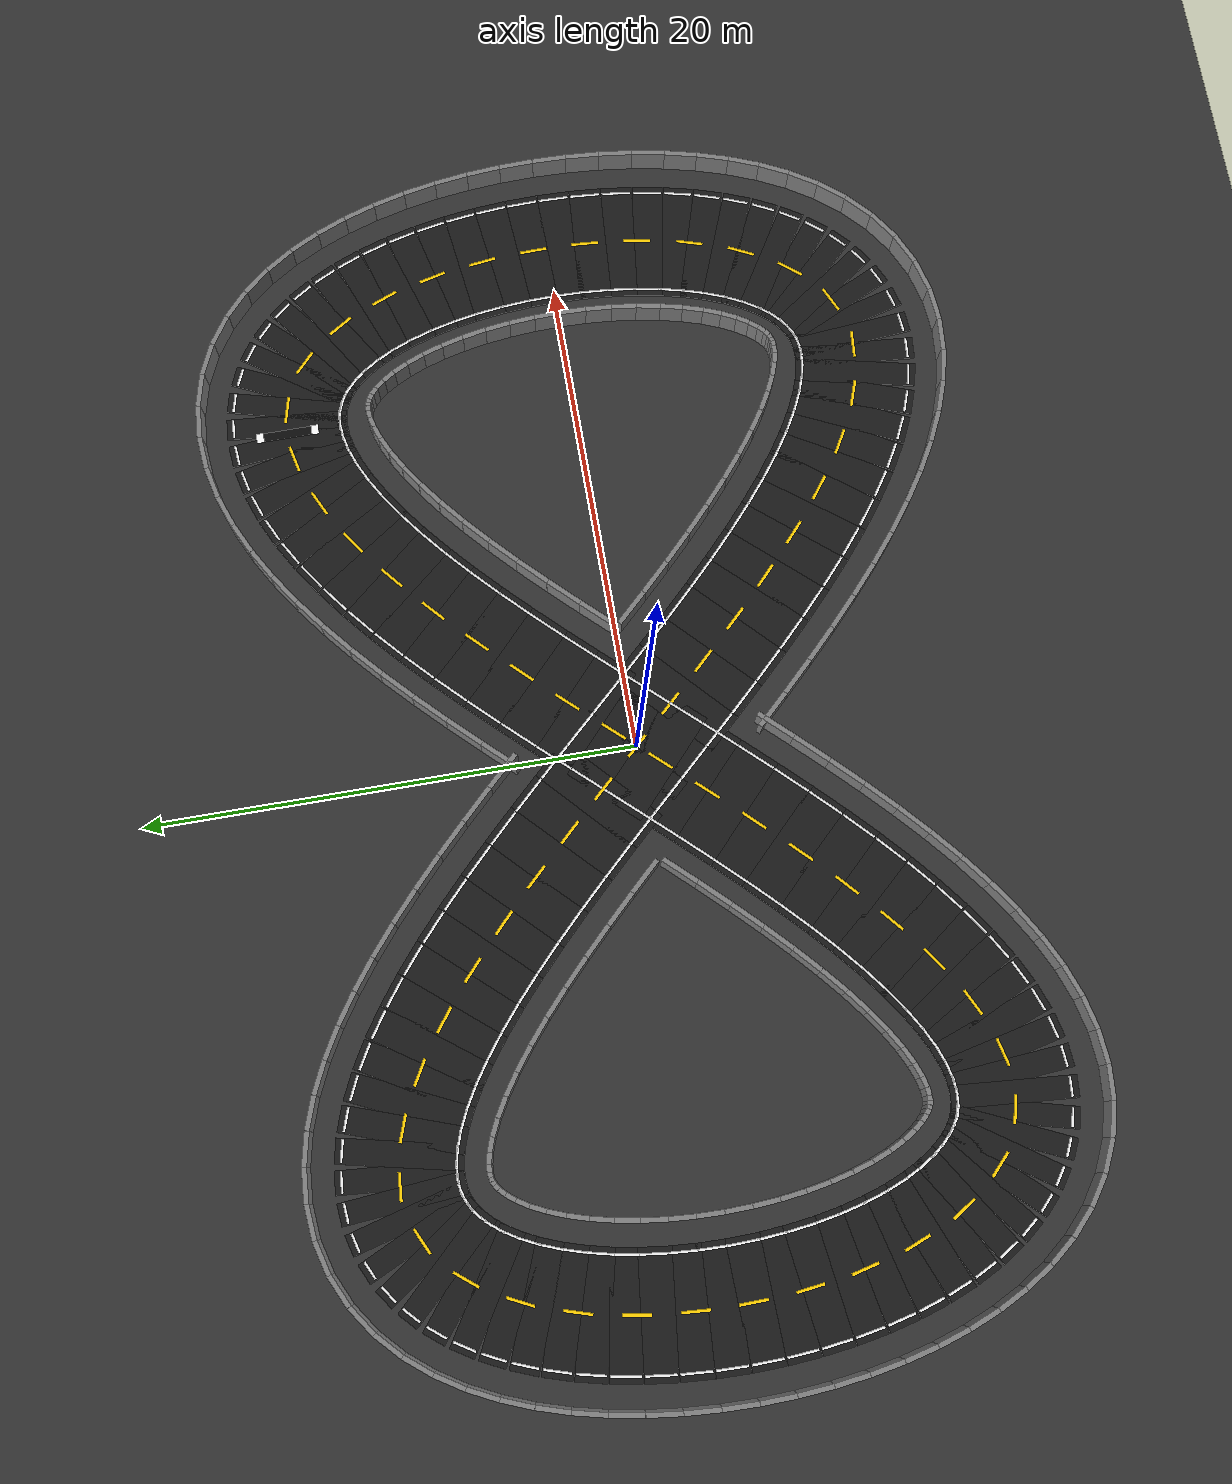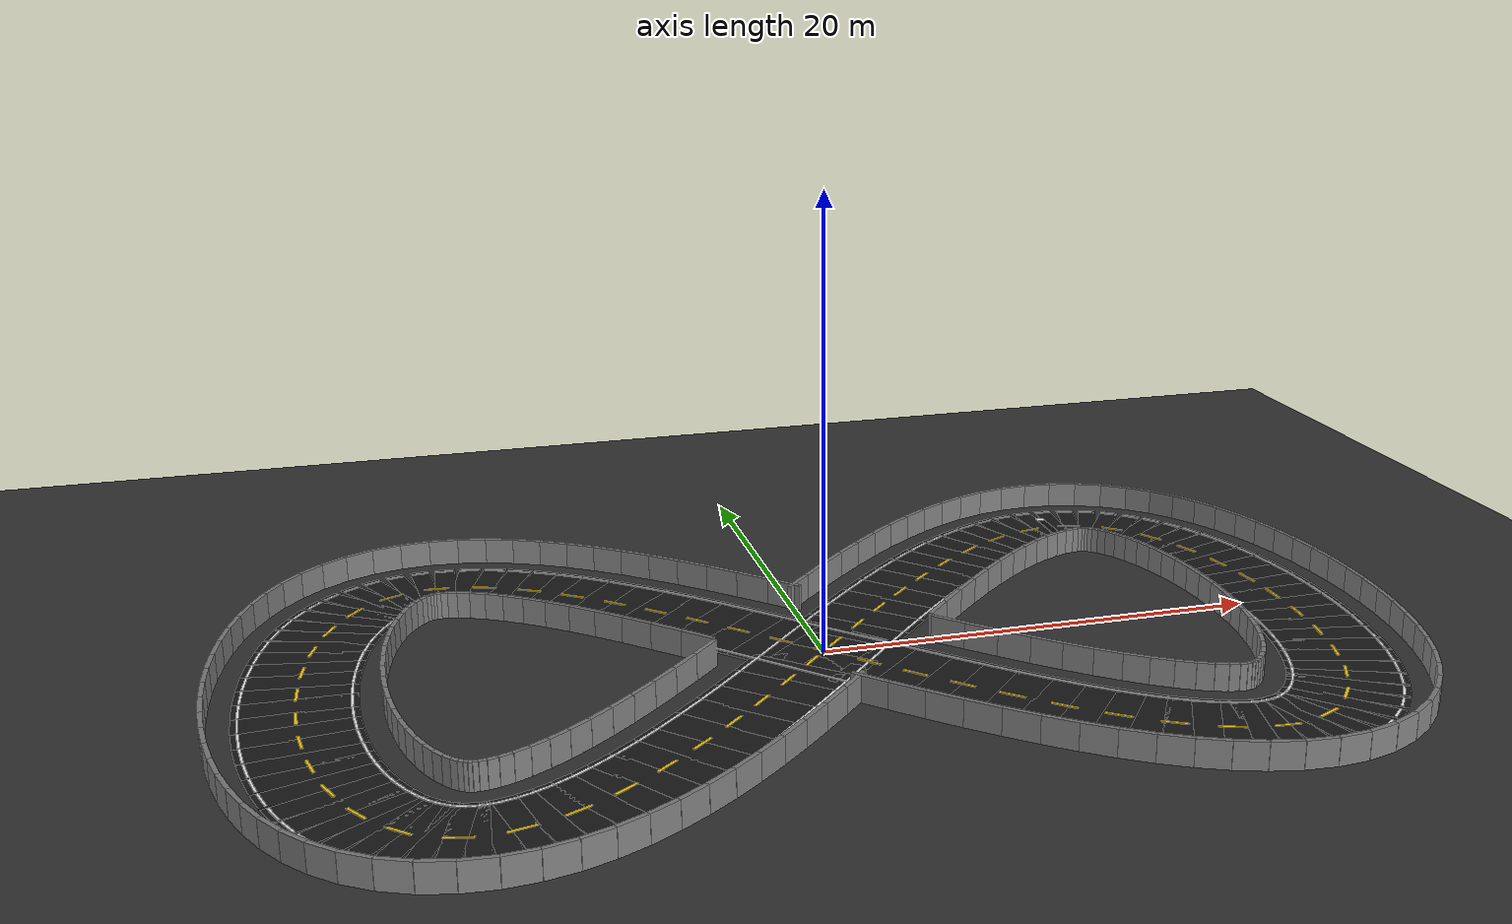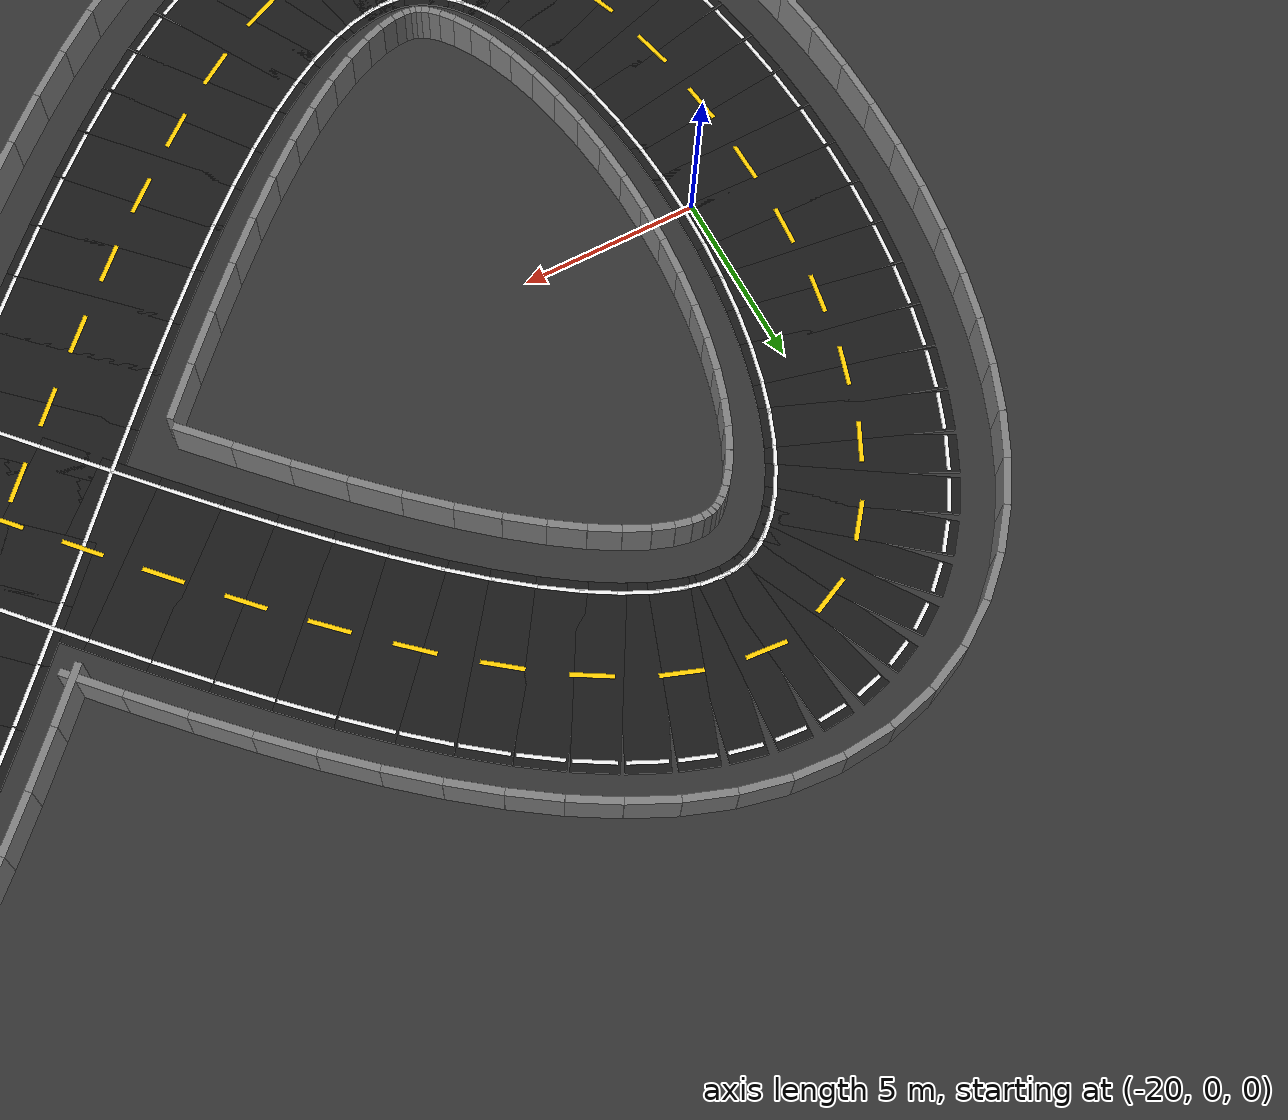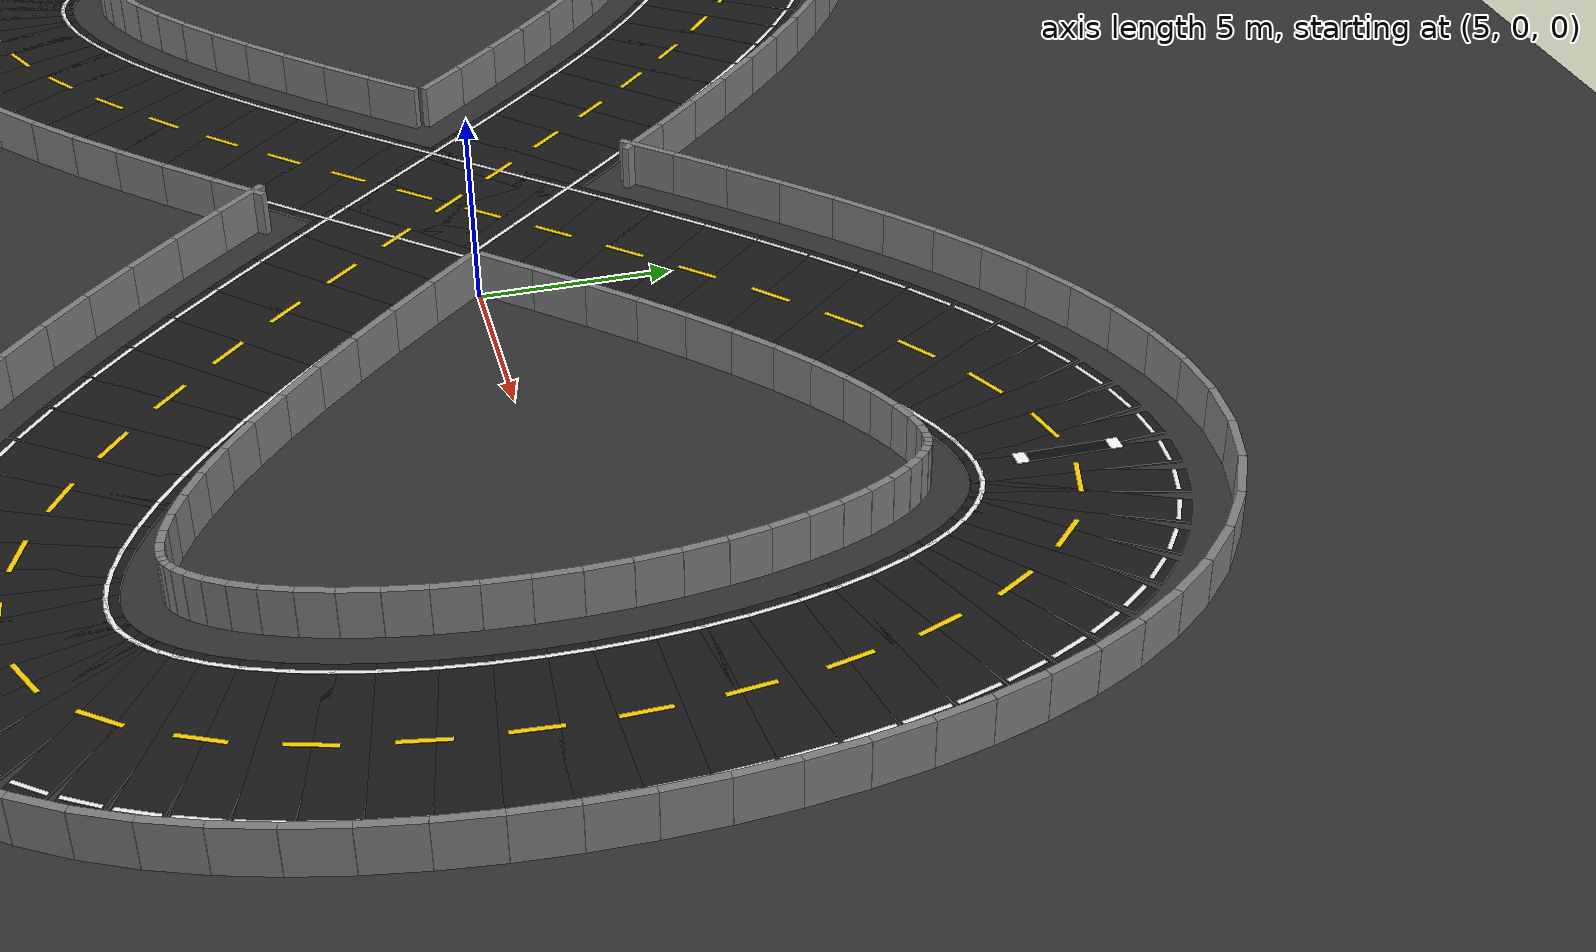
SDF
<?xml version="1.0"?>
<sdf version="1.6">
  <world name="adas_figure8_circuit">

    <gravity>0 0 -9.81</gravity>

    <scene>
      <ambient>0.65 0.65 0.65 1</ambient>
      <background>0.55 0.65 0.75 1</background>
      <shadows>true</shadows>
    </scene>

    <physics type="ode">
      <max_step_size>0.001</max_step_size>
      <real_time_update_rate>1000</real_time_update_rate>
    </physics>

    <!-- Lightweight flat ground -->
    <model name="ground">
      <static>true</static>
      <link name="link">
        <collision name="collision">
          <geometry>
            <plane>
              <normal>0 0 1</normal>
              <size>80.0 80.0</size>
            </plane>
          </geometry>
        </collision>
        <visual name="visual">
          <geometry>
            <plane>
              <normal>0 0 1</normal>
              <size>80.0 80.0</size>
            </plane>
          </geometry>
          <material>
            <ambient>0.16 0.16 0.16 1</ambient>
            <diffuse>0.20 0.20 0.20 1</diffuse>
          </material>
        </visual>
      </link>
    </model>

    <!-- Smooth closed figure-8 circuit approximated by short road segments -->
    <model name="road_000">
      <static>true</static>
      <pose>0.5757 0.6272 0.025 0 0 0.828166</pose>
      <link name="link">
        <collision name="collision">
          <geometry>
            <box>
              <size>1.8027 5.000 0.05</size>
            </box>
          </geometry>
        </collision>
        <visual name="visual">
          <geometry>
            <box>
              <size>1.8027 5.000 0.05</size>
            </box>
          </geometry>
          <material>
            <ambient>0.07 0.07 0.07 1</ambient>
            <diffuse>0.10 0.10 0.10 1</diffuse>
          </material>
        </visual>
      </link>
    </model>
    <model name="road_001">
      <static>true</static>
      <pose>1.7255 1.8746 0.025 0 0 0.824044</pose>
      <link name="link">
        <collision name="collision">
          <geometry>
            <box>
              <size>1.7904 5.000 0.05</size>
            </box>
          </geometry>
        </collision>
        <visual name="visual">
          <geometry>
            <box>
              <size>1.7904 5.000 0.05</size>
            </box>
          </geometry>
          <material>
            <ambient>0.07 0.07 0.07 1</ambient>
            <diffuse>0.10 0.10 0.10 1</diffuse>
          </material>
        </visual>
      </link>
    </model>
    <model name="road_002">
      <static>true</static>
      <pose>2.8706 3.1016 0.025 0 0 0.815676</pose>
      <link name="link">
        <collision name="collision">
          <geometry>
            <box>
              <size>1.7661 5.000 0.05</size>
            </box>
          </geometry>
        </collision>
        <visual name="visual">
          <geometry>
            <box>
              <size>1.7661 5.000 0.05</size>
            </box>
          </geometry>
          <material>
            <ambient>0.07 0.07 0.07 1</ambient>
            <diffuse>0.10 0.10 0.10 1</diffuse>
          </material>
        </visual>
      </link>
    </model>
    <model name="road_003">
      <static>true</static>
      <pose>4.0078 4.2945 0.025 0 0 0.802808</pose>
      <link name="link">
        <collision name="collision">
          <geometry>
            <box>
              <size>1.7302 5.000 0.05</size>
            </box>
          </geometry>
        </collision>
        <visual name="visual">
          <geometry>
            <box>
              <size>1.7302 5.000 0.05</size>
            </box>
          </geometry>
          <material>
            <ambient>0.07 0.07 0.07 1</ambient>
            <diffuse>0.10 0.10 0.10 1</diffuse>
          </material>
        </visual>
      </link>
    </model>
    <model name="road_004">
      <static>true</static>
      <pose>5.1340 5.4404 0.025 0 0 0.785040</pose>
      <link name="link">
        <collision name="collision">
          <geometry>
            <box>
              <size>1.6833 5.000 0.05</size>
            </box>
          </geometry>
        </collision>
        <visual name="visual">
          <geometry>
            <box>
              <size>1.6833 5.000 0.05</size>
            </box>
          </geometry>
          <material>
            <ambient>0.07 0.07 0.07 1</ambient>
            <diffuse>0.10 0.10 0.10 1</diffuse>
          </material>
        </visual>
      </link>
    </model>
    <model name="road_005">
      <static>true</static>
      <pose>6.2462 6.5267 0.025 0 0 0.761799</pose>
      <link name="link">
        <collision name="collision">
          <geometry>
            <box>
              <size>1.6262 5.000 0.05</size>
            </box>
          </geometry>
        </collision>
        <visual name="visual">
          <geometry>
            <box>
              <size>1.6262 5.000 0.05</size>
            </box>
          </geometry>
          <material>
            <ambient>0.07 0.07 0.07 1</ambient>
            <diffuse>0.10 0.10 0.10 1</diffuse>
          </material>
        </visual>
      </link>
    </model>
    <model name="road_006">
      <static>true</static>
      <pose>7.3412 7.5415 0.025 0 0 0.732304</pose>
      <link name="link">
        <collision name="collision">
          <geometry>
            <box>
              <size>1.5600 5.000 0.05</size>
            </box>
          </geometry>
        </collision>
        <visual name="visual">
          <geometry>
            <box>
              <size>1.5600 5.000 0.05</size>
            </box>
          </geometry>
          <material>
            <ambient>0.07 0.07 0.07 1</ambient>
            <diffuse>0.10 0.10 0.10 1</diffuse>
          </material>
        </visual>
      </link>
    </model>
    <model name="road_007">
      <static>true</static>
      <pose>8.4162 8.4737 0.025 0 0 0.695520</pose>
      <link name="link">
        <collision name="collision">
          <geometry>
            <box>
              <size>1.4861 5.000 0.05</size>
            </box>
          </geometry>
        </collision>
        <visual name="visual">
          <geometry>
            <box>
              <size>1.4861 5.000 0.05</size>
            </box>
          </geometry>
          <material>
            <ambient>0.07 0.07 0.07 1</ambient>
            <diffuse>0.10 0.10 0.10 1</diffuse>
          </material>
        </visual>
      </link>
    </model>
    <model name="road_008">
      <static>true</static>
      <pose>9.4680 9.3130 0.025 0 0 0.650103</pose>
      <link name="link">
        <collision name="collision">
          <geometry>
            <box>
              <size>1.4060 5.000 0.05</size>
            </box>
          </geometry>
        </collision>
        <visual name="visual">
          <geometry>
            <box>
              <size>1.4060 5.000 0.05</size>
            </box>
          </geometry>
          <material>
            <ambient>0.07 0.07 0.07 1</ambient>
            <diffuse>0.10 0.10 0.10 1</diffuse>
          </material>
        </visual>
      </link>
    </model>
    <model name="road_009">
      <static>true</static>
      <pose>10.4939 10.0503 0.025 0 0 0.594333</pose>
      <link name="link">
        <collision name="collision">
          <geometry>
            <box>
              <size>1.3217 5.000 0.05</size>
            </box>
          </geometry>
        </collision>
        <visual name="visual">
          <geometry>
            <box>
              <size>1.3217 5.000 0.05</size>
            </box>
          </geometry>
          <material>
            <ambient>0.07 0.07 0.07 1</ambient>
            <diffuse>0.10 0.10 0.10 1</diffuse>
          </material>
        </visual>
      </link>
    </model>
    <model name="road_010">
      <static>true</static>
      <pose>11.4910 10.6774 0.025 0 0 0.526076</pose>
      <link name="link">
        <collision name="collision">
          <geometry>
            <box>
              <size>1.2356 5.000 0.05</size>
            </box>
          </geometry>
        </collision>
        <visual name="visual">
          <geometry>
            <box>
              <size>1.2356 5.000 0.05</size>
            </box>
          </geometry>
          <material>
            <ambient>0.07 0.07 0.07 1</ambient>
            <diffuse>0.10 0.10 0.10 1</diffuse>
          </material>
        </visual>
      </link>
    </model>
    <model name="road_011">
      <static>true</static>
      <pose>12.4567 11.1876 0.025 0 0 0.442808</pose>
      <link name="link">
        <collision name="collision">
          <geometry>
            <box>
              <size>1.1505 5.000 0.05</size>
            </box>
          </geometry>
        </collision>
        <visual name="visual">
          <geometry>
            <box>
              <size>1.1505 5.000 0.05</size>
            </box>
          </geometry>
          <material>
            <ambient>0.07 0.07 0.07 1</ambient>
            <diffuse>0.10 0.10 0.10 1</diffuse>
          </material>
        </visual>
      </link>
    </model>
    <model name="road_012">
      <static>true</static>
      <pose>13.3882 11.5752 0.025 0 0 0.341806</pose>
      <link name="link">
        <collision name="collision">
          <geometry>
            <box>
              <size>1.0699 5.000 0.05</size>
            </box>
          </geometry>
        </collision>
        <visual name="visual">
          <geometry>
            <box>
              <size>1.0699 5.000 0.05</size>
            </box>
          </geometry>
          <material>
            <ambient>0.07 0.07 0.07 1</ambient>
            <diffuse>0.10 0.10 0.10 1</diffuse>
          </material>
        </visual>
      </link>
    </model>
    <model name="road_013">
      <static>true</static>
      <pose>14.2830 11.8360 0.025 0 0 0.220696</pose>
      <link name="link">
        <collision name="collision">
          <geometry>
            <box>
              <size>0.9976 5.000 0.05</size>
            </box>
          </geometry>
        </collision>
        <visual name="visual">
          <geometry>
            <box>
              <size>0.9976 5.000 0.05</size>
            </box>
          </geometry>
          <material>
            <ambient>0.07 0.07 0.07 1</ambient>
            <diffuse>0.10 0.10 0.10 1</diffuse>
          </material>
        </visual>
      </link>
    </model>
    <model name="road_014">
      <static>true</static>
      <pose>15.1386 11.9671 0.025 0 0 0.078521</pose>
      <link name="link">
        <collision name="collision">
          <geometry>
            <box>
              <size>0.9381 5.000 0.05</size>
            </box>
          </geometry>
        </collision>
        <visual name="visual">
          <geometry>
            <box>
              <size>0.9381 5.000 0.05</size>
            </box>
          </geometry>
          <material>
            <ambient>0.07 0.07 0.07 1</ambient>
            <diffuse>0.10 0.10 0.10 1</diffuse>
          </material>
        </visual>
      </link>
    </model>
    <model name="road_015">
      <static>true</static>
      <pose>15.9528 11.9671 0.025 0 0 -0.082725</pose>
      <link name="link">
        <collision name="collision">
          <geometry>
            <box>
              <size>0.8956 5.000 0.05</size>
            </box>
          </geometry>
        </collision>
        <visual name="visual">
          <geometry>
            <box>
              <size>0.8956 5.000 0.05</size>
            </box>
          </geometry>
          <material>
            <ambient>0.07 0.07 0.07 1</ambient>
            <diffuse>0.10 0.10 0.10 1</diffuse>
          </material>
        </visual>
      </link>
    </model>
    <model name="road_016">
      <static>true</static>
      <pose>16.7232 11.8360 0.025 0 0 -0.256877</pose>
      <link name="link">
        <collision name="collision">
          <geometry>
            <box>
              <size>0.8734 5.000 0.05</size>
            </box>
          </geometry>
        </collision>
        <visual name="visual">
          <geometry>
            <box>
              <size>0.8734 5.000 0.05</size>
            </box>
          </geometry>
          <material>
            <ambient>0.07 0.07 0.07 1</ambient>
            <diffuse>0.10 0.10 0.10 1</diffuse>
          </material>
        </visual>
      </link>
    </model>
    <model name="road_017">
      <static>true</static>
      <pose>17.4478 11.5752 0.025 0 0 -0.434146</pose>
      <link name="link">
        <collision name="collision">
          <geometry>
            <box>
              <size>0.8729 5.000 0.05</size>
            </box>
          </geometry>
        </collision>
        <visual name="visual">
          <geometry>
            <box>
              <size>0.8729 5.000 0.05</size>
            </box>
          </geometry>
          <material>
            <ambient>0.07 0.07 0.07 1</ambient>
            <diffuse>0.10 0.10 0.10 1</diffuse>
          </material>
        </visual>
      </link>
    </model>
    <model name="road_018">
      <static>true</static>
      <pose>18.1246 11.1876 0.025 0 0 -0.603974</pose>
      <link name="link">
        <collision name="collision">
          <geometry>
            <box>
              <size>0.8926 5.000 0.05</size>
            </box>
          </geometry>
        </collision>
        <visual name="visual">
          <geometry>
            <box>
              <size>0.8926 5.000 0.05</size>
            </box>
          </geometry>
          <material>
            <ambient>0.07 0.07 0.07 1</ambient>
            <diffuse>0.10 0.10 0.10 1</diffuse>
          </material>
        </visual>
      </link>
    </model>
    <model name="road_019">
      <static>true</static>
      <pose>18.7517 10.6774 0.025 0 0 -0.758473</pose>
      <link name="link">
        <collision name="collision">
          <geometry>
            <box>
              <size>0.9291 5.000 0.05</size>
            </box>
          </geometry>
        </collision>
        <visual name="visual">
          <geometry>
            <box>
              <size>0.9291 5.000 0.05</size>
            </box>
          </geometry>
          <material>
            <ambient>0.07 0.07 0.07 1</ambient>
            <diffuse>0.10 0.10 0.10 1</diffuse>
          </material>
        </visual>
      </link>
    </model>
    <model name="road_020">
      <static>true</static>
      <pose>19.3274 10.0503 0.025 0 0 -0.894005</pose>
      <link name="link">
        <collision name="collision">
          <geometry>
            <box>
              <size>0.9775 5.000 0.05</size>
            </box>
          </geometry>
        </collision>
        <visual name="visual">
          <geometry>
            <box>
              <size>0.9775 5.000 0.05</size>
            </box>
          </geometry>
          <material>
            <ambient>0.07 0.07 0.07 1</ambient>
            <diffuse>0.10 0.10 0.10 1</diffuse>
          </material>
        </visual>
      </link>
    </model>
    <model name="road_021">
      <static>true</static>
      <pose>19.8501 9.3130 0.025 0 0 -1.010547</pose>
      <link name="link">
        <collision name="collision">
          <geometry>
            <box>
              <size>1.0331 5.000 0.05</size>
            </box>
          </geometry>
        </collision>
        <visual name="visual">
          <geometry>
            <box>
              <size>1.0331 5.000 0.05</size>
            </box>
          </geometry>
          <material>
            <ambient>0.07 0.07 0.07 1</ambient>
            <diffuse>0.10 0.10 0.10 1</diffuse>
          </material>
        </visual>
      </link>
    </model>
    <model name="road_022">
      <static>true</static>
      <pose>20.3184 8.4737 0.025 0 0 -1.110140</pose>
      <link name="link">
        <collision name="collision">
          <geometry>
            <box>
              <size>1.0915 5.000 0.05</size>
            </box>
          </geometry>
        </collision>
        <visual name="visual">
          <geometry>
            <box>
              <size>1.0915 5.000 0.05</size>
            </box>
          </geometry>
          <material>
            <ambient>0.07 0.07 0.07 1</ambient>
            <diffuse>0.10 0.10 0.10 1</diffuse>
          </material>
        </visual>
      </link>
    </model>
    <model name="road_023">
      <static>true</static>
      <pose>20.7310 7.5415 0.025 0 0 -1.195586</pose>
      <link name="link">
        <collision name="collision">
          <geometry>
            <box>
              <size>1.1491 5.000 0.05</size>
            </box>
          </geometry>
        </collision>
        <visual name="visual">
          <geometry>
            <box>
              <size>1.1491 5.000 0.05</size>
            </box>
          </geometry>
          <material>
            <ambient>0.07 0.07 0.07 1</ambient>
            <diffuse>0.10 0.10 0.10 1</diffuse>
          </material>
        </visual>
      </link>
    </model>
    <model name="road_024">
      <static>true</static>
      <pose>21.0868 6.5267 0.025 0 0 -1.269703</pose>
      <link name="link">
        <collision name="collision">
          <geometry>
            <box>
              <size>1.2030 5.000 0.05</size>
            </box>
          </geometry>
        </collision>
        <visual name="visual">
          <geometry>
            <box>
              <size>1.2030 5.000 0.05</size>
            </box>
          </geometry>
          <material>
            <ambient>0.07 0.07 0.07 1</ambient>
            <diffuse>0.10 0.10 0.10 1</diffuse>
          </material>
        </visual>
      </link>
    </model>
    <model name="road_025">
      <static>true</static>
      <pose>21.3848 5.4404 0.025 0 0 -1.335014</pose>
      <link name="link">
        <collision name="collision">
          <geometry>
            <box>
              <size>1.2510 5.000 0.05</size>
            </box>
          </geometry>
        </collision>
        <visual name="visual">
          <geometry>
            <box>
              <size>1.2510 5.000 0.05</size>
            </box>
          </geometry>
          <material>
            <ambient>0.07 0.07 0.07 1</ambient>
            <diffuse>0.10 0.10 0.10 1</diffuse>
          </material>
        </visual>
      </link>
    </model>
    <model name="road_026">
      <static>true</static>
      <pose>21.6242 4.2945 0.025 0 0 -1.393677</pose>
      <link name="link">
        <collision name="collision">
          <geometry>
            <box>
              <size>1.2913 5.000 0.05</size>
            </box>
          </geometry>
        </collision>
        <visual name="visual">
          <geometry>
            <box>
              <size>1.2913 5.000 0.05</size>
            </box>
          </geometry>
          <material>
            <ambient>0.07 0.07 0.07 1</ambient>
            <diffuse>0.10 0.10 0.10 1</diffuse>
          </material>
        </visual>
      </link>
    </model>
    <model name="road_027">
      <static>true</static>
      <pose>21.8043 3.1016 0.025 0 0 -1.447513</pose>
      <link name="link">
        <collision name="collision">
          <geometry>
            <box>
              <size>1.3225 5.000 0.05</size>
            </box>
          </geometry>
        </collision>
        <visual name="visual">
          <geometry>
            <box>
              <size>1.3225 5.000 0.05</size>
            </box>
          </geometry>
          <material>
            <ambient>0.07 0.07 0.07 1</ambient>
            <diffuse>0.10 0.10 0.10 1</diffuse>
          </material>
        </visual>
      </link>
    </model>
    <model name="road_028">
      <static>true</static>
      <pose>21.9247 1.8746 0.025 0 0 -1.498082</pose>
      <link name="link">
        <collision name="collision">
          <geometry>
            <box>
              <size>1.3439 5.000 0.05</size>
            </box>
          </geometry>
        </collision>
        <visual name="visual">
          <geometry>
            <box>
              <size>1.3439 5.000 0.05</size>
            </box>
          </geometry>
          <material>
            <ambient>0.07 0.07 0.07 1</ambient>
            <diffuse>0.10 0.10 0.10 1</diffuse>
          </material>
        </visual>
      </link>
    </model>
    <model name="road_029">
      <static>true</static>
      <pose>21.9849 0.6272 0.025 0 0 -1.546764</pose>
      <link name="link">
        <collision name="collision">
          <geometry>
            <box>
              <size>1.3547 5.000 0.05</size>
            </box>
          </geometry>
        </collision>
        <visual name="visual">
          <geometry>
            <box>
              <size>1.3547 5.000 0.05</size>
            </box>
          </geometry>
          <material>
            <ambient>0.07 0.07 0.07 1</ambient>
            <diffuse>0.10 0.10 0.10 1</diffuse>
          </material>
        </visual>
      </link>
    </model>
    <model name="road_030">
      <static>true</static>
      <pose>21.9849 -0.6272 0.025 0 0 -1.594828</pose>
      <link name="link">
        <collision name="collision">
          <geometry>
            <box>
              <size>1.3547 5.000 0.05</size>
            </box>
          </geometry>
        </collision>
        <visual name="visual">
          <geometry>
            <box>
              <size>1.3547 5.000 0.05</size>
            </box>
          </geometry>
          <material>
            <ambient>0.07 0.07 0.07 1</ambient>
            <diffuse>0.10 0.10 0.10 1</diffuse>
          </material>
        </visual>
      </link>
    </model>
    <model name="road_031">
      <static>true</static>
      <pose>21.9247 -1.8746 0.025 0 0 -1.643510</pose>
      <link name="link">
        <collision name="collision">
          <geometry>
            <box>
              <size>1.3439 5.000 0.05</size>
            </box>
          </geometry>
        </collision>
        <visual name="visual">
          <geometry>
            <box>
              <size>1.3439 5.000 0.05</size>
            </box>
          </geometry>
          <material>
            <ambient>0.07 0.07 0.07 1</ambient>
            <diffuse>0.10 0.10 0.10 1</diffuse>
          </material>
        </visual>
      </link>
    </model>
    <model name="road_032">
      <static>true</static>
      <pose>21.8043 -3.1016 0.025 0 0 -1.694080</pose>
      <link name="link">
        <collision name="collision">
          <geometry>
            <box>
              <size>1.3225 5.000 0.05</size>
            </box>
          </geometry>
        </collision>
        <visual name="visual">
          <geometry>
            <box>
              <size>1.3225 5.000 0.05</size>
            </box>
          </geometry>
          <material>
            <ambient>0.07 0.07 0.07 1</ambient>
            <diffuse>0.10 0.10 0.10 1</diffuse>
          </material>
        </visual>
      </link>
    </model>
    <model name="road_033">
      <static>true</static>
      <pose>21.6242 -4.2945 0.025 0 0 -1.747916</pose>
      <link name="link">
        <collision name="collision">
          <geometry>
            <box>
              <size>1.2913 5.000 0.05</size>
            </box>
          </geometry>
        </collision>
        <visual name="visual">
          <geometry>
            <box>
              <size>1.2913 5.000 0.05</size>
            </box>
          </geometry>
          <material>
            <ambient>0.07 0.07 0.07 1</ambient>
            <diffuse>0.10 0.10 0.10 1</diffuse>
          </material>
        </visual>
      </link>
    </model>
    <model name="road_034">
      <static>true</static>
      <pose>21.3848 -5.4404 0.025 0 0 -1.806578</pose>
      <link name="link">
        <collision name="collision">
          <geometry>
            <box>
              <size>1.2510 5.000 0.05</size>
            </box>
          </geometry>
        </collision>
        <visual name="visual">
          <geometry>
            <box>
              <size>1.2510 5.000 0.05</size>
            </box>
          </geometry>
          <material>
            <ambient>0.07 0.07 0.07 1</ambient>
            <diffuse>0.10 0.10 0.10 1</diffuse>
          </material>
        </visual>
      </link>
    </model>
    <model name="road_035">
      <static>true</static>
      <pose>21.0868 -6.5267 0.025 0 0 -1.871890</pose>
      <link name="link">
        <collision name="collision">
          <geometry>
            <box>
              <size>1.2030 5.000 0.05</size>
            </box>
          </geometry>
        </collision>
        <visual name="visual">
          <geometry>
            <box>
              <size>1.2030 5.000 0.05</size>
            </box>
          </geometry>
          <material>
            <ambient>0.07 0.07 0.07 1</ambient>
            <diffuse>0.10 0.10 0.10 1</diffuse>
          </material>
        </visual>
      </link>
    </model>
    <model name="road_036">
      <static>true</static>
      <pose>20.7310 -7.5415 0.025 0 0 -1.946007</pose>
      <link name="link">
        <collision name="collision">
          <geometry>
            <box>
              <size>1.1491 5.000 0.05</size>
            </box>
          </geometry>
        </collision>
        <visual name="visual">
          <geometry>
            <box>
              <size>1.1491 5.000 0.05</size>
            </box>
          </geometry>
          <material>
            <ambient>0.07 0.07 0.07 1</ambient>
            <diffuse>0.10 0.10 0.10 1</diffuse>
          </material>
        </visual>
      </link>
    </model>
    <model name="road_037">
      <static>true</static>
      <pose>20.3184 -8.4737 0.025 0 0 -2.031453</pose>
      <link name="link">
        <collision name="collision">
          <geometry>
            <box>
              <size>1.0915 5.000 0.05</size>
            </box>
          </geometry>
        </collision>
        <visual name="visual">
          <geometry>
            <box>
              <size>1.0915 5.000 0.05</size>
            </box>
          </geometry>
          <material>
            <ambient>0.07 0.07 0.07 1</ambient>
            <diffuse>0.10 0.10 0.10 1</diffuse>
          </material>
        </visual>
      </link>
    </model>
    <model name="road_038">
      <static>true</static>
      <pose>19.8501 -9.3130 0.025 0 0 -2.131045</pose>
      <link name="link">
        <collision name="collision">
          <geometry>
            <box>
              <size>1.0331 5.000 0.05</size>
            </box>
          </geometry>
        </collision>
        <visual name="visual">
          <geometry>
            <box>
              <size>1.0331 5.000 0.05</size>
            </box>
          </geometry>
          <material>
            <ambient>0.07 0.07 0.07 1</ambient>
            <diffuse>0.10 0.10 0.10 1</diffuse>
          </material>
        </visual>
      </link>
    </model>
    <model name="road_039">
      <static>true</static>
      <pose>19.3274 -10.0503 0.025 0 0 -2.247587</pose>
      <link name="link">
        <collision name="collision">
          <geometry>
            <box>
              <size>0.9775 5.000 0.05</size>
            </box>
          </geometry>
        </collision>
        <visual name="visual">
          <geometry>
            <box>
              <size>0.9775 5.000 0.05</size>
            </box>
          </geometry>
          <material>
            <ambient>0.07 0.07 0.07 1</ambient>
            <diffuse>0.10 0.10 0.10 1</diffuse>
          </material>
        </visual>
      </link>
    </model>
    <model name="road_040">
      <static>true</static>
      <pose>18.7517 -10.6774 0.025 0 0 -2.383120</pose>
      <link name="link">
        <collision name="collision">
          <geometry>
            <box>
              <size>0.9291 5.000 0.05</size>
            </box>
          </geometry>
        </collision>
        <visual name="visual">
          <geometry>
            <box>
              <size>0.9291 5.000 0.05</size>
            </box>
          </geometry>
          <material>
            <ambient>0.07 0.07 0.07 1</ambient>
            <diffuse>0.10 0.10 0.10 1</diffuse>
          </material>
        </visual>
      </link>
    </model>
    <model name="road_041">
      <static>true</static>
      <pose>18.1246 -11.1876 0.025 0 0 -2.537619</pose>
      <link name="link">
        <collision name="collision">
          <geometry>
            <box>
              <size>0.8926 5.000 0.05</size>
            </box>
          </geometry>
        </collision>
        <visual name="visual">
          <geometry>
            <box>
              <size>0.8926 5.000 0.05</size>
            </box>
          </geometry>
          <material>
            <ambient>0.07 0.07 0.07 1</ambient>
            <diffuse>0.10 0.10 0.10 1</diffuse>
          </material>
        </visual>
      </link>
    </model>
    <model name="road_042">
      <static>true</static>
      <pose>17.4478 -11.5752 0.025 0 0 -2.707447</pose>
      <link name="link">
        <collision name="collision">
          <geometry>
            <box>
              <size>0.8729 5.000 0.05</size>
            </box>
          </geometry>
        </collision>
        <visual name="visual">
          <geometry>
            <box>
              <size>0.8729 5.000 0.05</size>
            </box>
          </geometry>
          <material>
            <ambient>0.07 0.07 0.07 1</ambient>
            <diffuse>0.10 0.10 0.10 1</diffuse>
          </material>
        </visual>
      </link>
    </model>
    <model name="road_043">
      <static>true</static>
      <pose>16.7232 -11.8360 0.025 0 0 -2.884716</pose>
      <link name="link">
        <collision name="collision">
          <geometry>
            <box>
              <size>0.8734 5.000 0.05</size>
            </box>
          </geometry>
        </collision>
        <visual name="visual">
          <geometry>
            <box>
              <size>0.8734 5.000 0.05</size>
            </box>
          </geometry>
          <material>
            <ambient>0.07 0.07 0.07 1</ambient>
            <diffuse>0.10 0.10 0.10 1</diffuse>
          </material>
        </visual>
      </link>
    </model>
    <model name="road_044">
      <static>true</static>
      <pose>15.9528 -11.9671 0.025 0 0 -3.058868</pose>
      <link name="link">
        <collision name="collision">
          <geometry>
            <box>
              <size>0.8956 5.000 0.05</size>
            </box>
          </geometry>
        </collision>
        <visual name="visual">
          <geometry>
            <box>
              <size>0.8956 5.000 0.05</size>
            </box>
          </geometry>
          <material>
            <ambient>0.07 0.07 0.07 1</ambient>
            <diffuse>0.10 0.10 0.10 1</diffuse>
          </material>
        </visual>
      </link>
    </model>
    <model name="road_045">
      <static>true</static>
      <pose>15.1386 -11.9671 0.025 0 0 3.063072</pose>
      <link name="link">
        <collision name="collision">
          <geometry>
            <box>
              <size>0.9381 5.000 0.05</size>
            </box>
          </geometry>
        </collision>
        <visual name="visual">
          <geometry>
            <box>
              <size>0.9381 5.000 0.05</size>
            </box>
          </geometry>
          <material>
            <ambient>0.07 0.07 0.07 1</ambient>
            <diffuse>0.10 0.10 0.10 1</diffuse>
          </material>
        </visual>
      </link>
    </model>
    <model name="road_046">
      <static>true</static>
      <pose>14.2830 -11.8360 0.025 0 0 2.920897</pose>
      <link name="link">
        <collision name="collision">
          <geometry>
            <box>
              <size>0.9976 5.000 0.05</size>
            </box>
          </geometry>
        </collision>
        <visual name="visual">
          <geometry>
            <box>
              <size>0.9976 5.000 0.05</size>
            </box>
          </geometry>
          <material>
            <ambient>0.07 0.07 0.07 1</ambient>
            <diffuse>0.10 0.10 0.10 1</diffuse>
          </material>
        </visual>
      </link>
    </model>
    <model name="road_047">
      <static>true</static>
      <pose>13.3882 -11.5752 0.025 0 0 2.799787</pose>
      <link name="link">
        <collision name="collision">
          <geometry>
            <box>
              <size>1.0699 5.000 0.05</size>
            </box>
          </geometry>
        </collision>
        <visual name="visual">
          <geometry>
            <box>
              <size>1.0699 5.000 0.05</size>
            </box>
          </geometry>
          <material>
            <ambient>0.07 0.07 0.07 1</ambient>
            <diffuse>0.10 0.10 0.10 1</diffuse>
          </material>
        </visual>
      </link>
    </model>
    <model name="road_048">
      <static>true</static>
      <pose>12.4567 -11.1876 0.025 0 0 2.698785</pose>
      <link name="link">
        <collision name="collision">
          <geometry>
            <box>
              <size>1.1505 5.000 0.05</size>
            </box>
          </geometry>
        </collision>
        <visual name="visual">
          <geometry>
            <box>
              <size>1.1505 5.000 0.05</size>
            </box>
          </geometry>
          <material>
            <ambient>0.07 0.07 0.07 1</ambient>
            <diffuse>0.10 0.10 0.10 1</diffuse>
          </material>
        </visual>
      </link>
    </model>
    <model name="road_049">
      <static>true</static>
      <pose>11.4910 -10.6774 0.025 0 0 2.615516</pose>
      <link name="link">
        <collision name="collision">
          <geometry>
            <box>
              <size>1.2356 5.000 0.05</size>
            </box>
          </geometry>
        </collision>
        <visual name="visual">
          <geometry>
            <box>
              <size>1.2356 5.000 0.05</size>
            </box>
          </geometry>
          <material>
            <ambient>0.07 0.07 0.07 1</ambient>
            <diffuse>0.10 0.10 0.10 1</diffuse>
          </material>
        </visual>
      </link>
    </model>
    <model name="road_050">
      <static>true</static>
      <pose>10.4939 -10.0503 0.025 0 0 2.547260</pose>
      <link name="link">
        <collision name="collision">
          <geometry>
            <box>
              <size>1.3217 5.000 0.05</size>
            </box>
          </geometry>
        </collision>
        <visual name="visual">
          <geometry>
            <box>
              <size>1.3217 5.000 0.05</size>
            </box>
          </geometry>
          <material>
            <ambient>0.07 0.07 0.07 1</ambient>
            <diffuse>0.10 0.10 0.10 1</diffuse>
          </material>
        </visual>
      </link>
    </model>
    <model name="road_051">
      <static>true</static>
      <pose>9.4680 -9.3130 0.025 0 0 2.491490</pose>
      <link name="link">
        <collision name="collision">
          <geometry>
            <box>
              <size>1.4060 5.000 0.05</size>
            </box>
          </geometry>
        </collision>
        <visual name="visual">
          <geometry>
            <box>
              <size>1.4060 5.000 0.05</size>
            </box>
          </geometry>
          <material>
            <ambient>0.07 0.07 0.07 1</ambient>
            <diffuse>0.10 0.10 0.10 1</diffuse>
          </material>
        </visual>
      </link>
    </model>
    <model name="road_052">
      <static>true</static>
      <pose>8.4162 -8.4737 0.025 0 0 2.446072</pose>
      <link name="link">
        <collision name="collision">
          <geometry>
            <box>
              <size>1.4861 5.000 0.05</size>
            </box>
          </geometry>
        </collision>
        <visual name="visual">
          <geometry>
            <box>
              <size>1.4861 5.000 0.05</size>
            </box>
          </geometry>
          <material>
            <ambient>0.07 0.07 0.07 1</ambient>
            <diffuse>0.10 0.10 0.10 1</diffuse>
          </material>
        </visual>
      </link>
    </model>
    <model name="road_053">
      <static>true</static>
      <pose>7.3412 -7.5415 0.025 0 0 2.409289</pose>
      <link name="link">
        <collision name="collision">
          <geometry>
            <box>
              <size>1.5600 5.000 0.05</size>
            </box>
          </geometry>
        </collision>
        <visual name="visual">
          <geometry>
            <box>
              <size>1.5600 5.000 0.05</size>
            </box>
          </geometry>
          <material>
            <ambient>0.07 0.07 0.07 1</ambient>
            <diffuse>0.10 0.10 0.10 1</diffuse>
          </material>
        </visual>
      </link>
    </model>
    <model name="road_054">
      <static>true</static>
      <pose>6.2462 -6.5267 0.025 0 0 2.379794</pose>
      <link name="link">
        <collision name="collision">
          <geometry>
            <box>
              <size>1.6262 5.000 0.05</size>
            </box>
          </geometry>
        </collision>
        <visual name="visual">
          <geometry>
            <box>
              <size>1.6262 5.000 0.05</size>
            </box>
          </geometry>
          <material>
            <ambient>0.07 0.07 0.07 1</ambient>
            <diffuse>0.10 0.10 0.10 1</diffuse>
          </material>
        </visual>
      </link>
    </model>
    <model name="road_055">
      <static>true</static>
      <pose>5.1340 -5.4404 0.025 0 0 2.356552</pose>
      <link name="link">
        <collision name="collision">
          <geometry>
            <box>
              <size>1.6833 5.000 0.05</size>
            </box>
          </geometry>
        </collision>
        <visual name="visual">
          <geometry>
            <box>
              <size>1.6833 5.000 0.05</size>
            </box>
          </geometry>
          <material>
            <ambient>0.07 0.07 0.07 1</ambient>
            <diffuse>0.10 0.10 0.10 1</diffuse>
          </material>
        </visual>
      </link>
    </model>
    <model name="road_056">
      <static>true</static>
      <pose>4.0078 -4.2945 0.025 0 0 2.338784</pose>
      <link name="link">
        <collision name="collision">
          <geometry>
            <box>
              <size>1.7302 5.000 0.05</size>
            </box>
          </geometry>
        </collision>
        <visual name="visual">
          <geometry>
            <box>
              <size>1.7302 5.000 0.05</size>
            </box>
          </geometry>
          <material>
            <ambient>0.07 0.07 0.07 1</ambient>
            <diffuse>0.10 0.10 0.10 1</diffuse>
          </material>
        </visual>
      </link>
    </model>
    <model name="road_057">
      <static>true</static>
      <pose>2.8706 -3.1016 0.025 0 0 2.325917</pose>
      <link name="link">
        <collision name="collision">
          <geometry>
            <box>
              <size>1.7661 5.000 0.05</size>
            </box>
          </geometry>
        </collision>
        <visual name="visual">
          <geometry>
            <box>
              <size>1.7661 5.000 0.05</size>
            </box>
          </geometry>
          <material>
            <ambient>0.07 0.07 0.07 1</ambient>
            <diffuse>0.10 0.10 0.10 1</diffuse>
          </material>
        </visual>
      </link>
    </model>
    <model name="road_058">
      <static>true</static>
      <pose>1.7255 -1.8746 0.025 0 0 2.317549</pose>
      <link name="link">
        <collision name="collision">
          <geometry>
            <box>
              <size>1.7904 5.000 0.05</size>
            </box>
          </geometry>
        </collision>
        <visual name="visual">
          <geometry>
            <box>
              <size>1.7904 5.000 0.05</size>
            </box>
          </geometry>
          <material>
            <ambient>0.07 0.07 0.07 1</ambient>
            <diffuse>0.10 0.10 0.10 1</diffuse>
          </material>
        </visual>
      </link>
    </model>
    <model name="road_059">
      <static>true</static>
      <pose>0.5757 -0.6272 0.025 0 0 2.313427</pose>
      <link name="link">
        <collision name="collision">
          <geometry>
            <box>
              <size>1.8027 5.000 0.05</size>
            </box>
          </geometry>
        </collision>
        <visual name="visual">
          <geometry>
            <box>
              <size>1.8027 5.000 0.05</size>
            </box>
          </geometry>
          <material>
            <ambient>0.07 0.07 0.07 1</ambient>
            <diffuse>0.10 0.10 0.10 1</diffuse>
          </material>
        </visual>
      </link>
    </model>
    <model name="road_060">
      <static>true</static>
      <pose>-0.5757 0.6272 0.025 0 0 2.313427</pose>
      <link name="link">
        <collision name="collision">
          <geometry>
            <box>
              <size>1.8027 5.000 0.05</size>
            </box>
          </geometry>
        </collision>
        <visual name="visual">
          <geometry>
            <box>
              <size>1.8027 5.000 0.05</size>
            </box>
          </geometry>
          <material>
            <ambient>0.07 0.07 0.07 1</ambient>
            <diffuse>0.10 0.10 0.10 1</diffuse>
          </material>
        </visual>
      </link>
    </model>
    <model name="road_061">
      <static>true</static>
      <pose>-1.7255 1.8746 0.025 0 0 2.317549</pose>
      <link name="link">
        <collision name="collision">
          <geometry>
            <box>
              <size>1.7904 5.000 0.05</size>
            </box>
          </geometry>
        </collision>
        <visual name="visual">
          <geometry>
            <box>
              <size>1.7904 5.000 0.05</size>
            </box>
          </geometry>
          <material>
            <ambient>0.07 0.07 0.07 1</ambient>
            <diffuse>0.10 0.10 0.10 1</diffuse>
          </material>
        </visual>
      </link>
    </model>
    <model name="road_062">
      <static>true</static>
      <pose>-2.8706 3.1016 0.025 0 0 2.325917</pose>
      <link name="link">
        <collision name="collision">
          <geometry>
            <box>
              <size>1.7661 5.000 0.05</size>
            </box>
          </geometry>
        </collision>
        <visual name="visual">
          <geometry>
            <box>
              <size>1.7661 5.000 0.05</size>
            </box>
          </geometry>
          <material>
            <ambient>0.07 0.07 0.07 1</ambient>
            <diffuse>0.10 0.10 0.10 1</diffuse>
          </material>
        </visual>
      </link>
    </model>
    <model name="road_063">
      <static>true</static>
      <pose>-4.0078 4.2945 0.025 0 0 2.338784</pose>
      <link name="link">
        <collision name="collision">
          <geometry>
            <box>
              <size>1.7302 5.000 0.05</size>
            </box>
          </geometry>
        </collision>
        <visual name="visual">
          <geometry>
            <box>
              <size>1.7302 5.000 0.05</size>
            </box>
          </geometry>
          <material>
            <ambient>0.07 0.07 0.07 1</ambient>
            <diffuse>0.10 0.10 0.10 1</diffuse>
          </material>
        </visual>
      </link>
    </model>
    <model name="road_064">
      <static>true</static>
      <pose>-5.1340 5.4404 0.025 0 0 2.356552</pose>
      <link name="link">
        <collision name="collision">
          <geometry>
            <box>
              <size>1.6833 5.000 0.05</size>
            </box>
          </geometry>
        </collision>
        <visual name="visual">
          <geometry>
            <box>
              <size>1.6833 5.000 0.05</size>
            </box>
          </geometry>
          <material>
            <ambient>0.07 0.07 0.07 1</ambient>
            <diffuse>0.10 0.10 0.10 1</diffuse>
          </material>
        </visual>
      </link>
    </model>
    <model name="road_065">
      <static>true</static>
      <pose>-6.2462 6.5267 0.025 0 0 2.379794</pose>
      <link name="link">
        <collision name="collision">
          <geometry>
            <box>
              <size>1.6262 5.000 0.05</size>
            </box>
          </geometry>
        </collision>
        <visual name="visual">
          <geometry>
            <box>
              <size>1.6262 5.000 0.05</size>
            </box>
          </geometry>
          <material>
            <ambient>0.07 0.07 0.07 1</ambient>
            <diffuse>0.10 0.10 0.10 1</diffuse>
          </material>
        </visual>
      </link>
    </model>
    <model name="road_066">
      <static>true</static>
      <pose>-7.3412 7.5415 0.025 0 0 2.409289</pose>
      <link name="link">
        <collision name="collision">
          <geometry>
            <box>
              <size>1.5600 5.000 0.05</size>
            </box>
          </geometry>
        </collision>
        <visual name="visual">
          <geometry>
            <box>
              <size>1.5600 5.000 0.05</size>
            </box>
          </geometry>
          <material>
            <ambient>0.07 0.07 0.07 1</ambient>
            <diffuse>0.10 0.10 0.10 1</diffuse>
          </material>
        </visual>
      </link>
    </model>
    <model name="road_067">
      <static>true</static>
      <pose>-8.4162 8.4737 0.025 0 0 2.446072</pose>
      <link name="link">
        <collision name="collision">
          <geometry>
            <box>
              <size>1.4861 5.000 0.05</size>
            </box>
          </geometry>
        </collision>
        <visual name="visual">
          <geometry>
            <box>
              <size>1.4861 5.000 0.05</size>
            </box>
          </geometry>
          <material>
            <ambient>0.07 0.07 0.07 1</ambient>
            <diffuse>0.10 0.10 0.10 1</diffuse>
          </material>
        </visual>
      </link>
    </model>
    <model name="road_068">
      <static>true</static>
      <pose>-9.4680 9.3130 0.025 0 0 2.491490</pose>
      <link name="link">
        <collision name="collision">
          <geometry>
            <box>
              <size>1.4060 5.000 0.05</size>
            </box>
          </geometry>
        </collision>
        <visual name="visual">
          <geometry>
            <box>
              <size>1.4060 5.000 0.05</size>
            </box>
          </geometry>
          <material>
            <ambient>0.07 0.07 0.07 1</ambient>
            <diffuse>0.10 0.10 0.10 1</diffuse>
          </material>
        </visual>
      </link>
    </model>
    <model name="road_069">
      <static>true</static>
      <pose>-10.4939 10.0503 0.025 0 0 2.547260</pose>
      <link name="link">
        <collision name="collision">
          <geometry>
            <box>
              <size>1.3217 5.000 0.05</size>
            </box>
          </geometry>
        </collision>
        <visual name="visual">
          <geometry>
            <box>
              <size>1.3217 5.000 0.05</size>
            </box>
          </geometry>
          <material>
            <ambient>0.07 0.07 0.07 1</ambient>
            <diffuse>0.10 0.10 0.10 1</diffuse>
          </material>
        </visual>
      </link>
    </model>
    <model name="road_070">
      <static>true</static>
      <pose>-11.4910 10.6774 0.025 0 0 2.615516</pose>
      <link name="link">
        <collision name="collision">
          <geometry>
            <box>
              <size>1.2356 5.000 0.05</size>
            </box>
          </geometry>
        </collision>
        <visual name="visual">
          <geometry>
            <box>
              <size>1.2356 5.000 0.05</size>
            </box>
          </geometry>
          <material>
            <ambient>0.07 0.07 0.07 1</ambient>
            <diffuse>0.10 0.10 0.10 1</diffuse>
          </material>
        </visual>
      </link>
    </model>
    <model name="road_071">
      <static>true</static>
      <pose>-12.4567 11.1876 0.025 0 0 2.698785</pose>
      <link name="link">
        <collision name="collision">
          <geometry>
            <box>
              <size>1.1505 5.000 0.05</size>
            </box>
          </geometry>
        </collision>
        <visual name="visual">
          <geometry>
            <box>
              <size>1.1505 5.000 0.05</size>
            </box>
          </geometry>
          <material>
            <ambient>0.07 0.07 0.07 1</ambient>
            <diffuse>0.10 0.10 0.10 1</diffuse>
          </material>
        </visual>
      </link>
    </model>
    <model name="road_072">
      <static>true</static>
      <pose>-13.3882 11.5752 0.025 0 0 2.799787</pose>
      <link name="link">
        <collision name="collision">
          <geometry>
            <box>
              <size>1.0699 5.000 0.05</size>
            </box>
          </geometry>
        </collision>
        <visual name="visual">
          <geometry>
            <box>
              <size>1.0699 5.000 0.05</size>
            </box>
          </geometry>
          <material>
            <ambient>0.07 0.07 0.07 1</ambient>
            <diffuse>0.10 0.10 0.10 1</diffuse>
          </material>
        </visual>
      </link>
    </model>
    <model name="road_073">
      <static>true</static>
      <pose>-14.2830 11.8360 0.025 0 0 2.920897</pose>
      <link name="link">
        <collision name="collision">
          <geometry>
            <box>
              <size>0.9976 5.000 0.05</size>
            </box>
          </geometry>
        </collision>
        <visual name="visual">
          <geometry>
            <box>
              <size>0.9976 5.000 0.05</size>
            </box>
          </geometry>
          <material>
            <ambient>0.07 0.07 0.07 1</ambient>
            <diffuse>0.10 0.10 0.10 1</diffuse>
          </material>
        </visual>
      </link>
    </model>
    <model name="road_074">
      <static>true</static>
      <pose>-15.1386 11.9671 0.025 0 0 3.063072</pose>
      <link name="link">
        <collision name="collision">
          <geometry>
            <box>
              <size>0.9381 5.000 0.05</size>
            </box>
          </geometry>
        </collision>
        <visual name="visual">
          <geometry>
            <box>
              <size>0.9381 5.000 0.05</size>
            </box>
          </geometry>
          <material>
            <ambient>0.07 0.07 0.07 1</ambient>
            <diffuse>0.10 0.10 0.10 1</diffuse>
          </material>
        </visual>
      </link>
    </model>
    <model name="road_075">
      <static>true</static>
      <pose>-15.9528 11.9671 0.025 0 0 -3.058868</pose>
      <link name="link">
        <collision name="collision">
          <geometry>
            <box>
              <size>0.8956 5.000 0.05</size>
            </box>
          </geometry>
        </collision>
        <visual name="visual">
          <geometry>
            <box>
              <size>0.8956 5.000 0.05</size>
            </box>
          </geometry>
          <material>
            <ambient>0.07 0.07 0.07 1</ambient>
            <diffuse>0.10 0.10 0.10 1</diffuse>
          </material>
        </visual>
      </link>
    </model>
    <model name="road_076">
      <static>true</static>
      <pose>-16.7232 11.8360 0.025 0 0 -2.884716</pose>
      <link name="link">
        <collision name="collision">
          <geometry>
            <box>
              <size>0.8734 5.000 0.05</size>
            </box>
          </geometry>
        </collision>
        <visual name="visual">
          <geometry>
            <box>
              <size>0.8734 5.000 0.05</size>
            </box>
          </geometry>
          <material>
            <ambient>0.07 0.07 0.07 1</ambient>
            <diffuse>0.10 0.10 0.10 1</diffuse>
          </material>
        </visual>
      </link>
    </model>
    <model name="road_077">
      <static>true</static>
      <pose>-17.4478 11.5752 0.025 0 0 -2.707447</pose>
      <link name="link">
        <collision name="collision">
          <geometry>
            <box>
              <size>0.8729 5.000 0.05</size>
            </box>
          </geometry>
        </collision>
        <visual name="visual">
          <geometry>
            <box>
              <size>0.8729 5.000 0.05</size>
            </box>
          </geometry>
          <material>
            <ambient>0.07 0.07 0.07 1</ambient>
            <diffuse>0.10 0.10 0.10 1</diffuse>
          </material>
        </visual>
      </link>
    </model>
    <model name="road_078">
      <static>true</static>
      <pose>-18.1246 11.1876 0.025 0 0 -2.537619</pose>
      <link name="link">
        <collision name="collision">
          <geometry>
            <box>
              <size>0.8926 5.000 0.05</size>
            </box>
          </geometry>
        </collision>
        <visual name="visual">
          <geometry>
            <box>
              <size>0.8926 5.000 0.05</size>
            </box>
          </geometry>
          <material>
            <ambient>0.07 0.07 0.07 1</ambient>
            <diffuse>0.10 0.10 0.10 1</diffuse>
          </material>
        </visual>
      </link>
    </model>
    <model name="road_079">
      <static>true</static>
      <pose>-18.7517 10.6774 0.025 0 0 -2.383120</pose>
      <link name="link">
        <collision name="collision">
          <geometry>
            <box>
              <size>0.9291 5.000 0.05</size>
            </box>
          </geometry>
        </collision>
        <visual name="visual">
          <geometry>
            <box>
              <size>0.9291 5.000 0.05</size>
            </box>
          </geometry>
          <material>
            <ambient>0.07 0.07 0.07 1</ambient>
            <diffuse>0.10 0.10 0.10 1</diffuse>
          </material>
        </visual>
      </link>
    </model>
    <model name="road_080">
      <static>true</static>
      <pose>-19.3274 10.0503 0.025 0 0 -2.247587</pose>
      <link name="link">
        <collision name="collision">
          <geometry>
            <box>
              <size>0.9775 5.000 0.05</size>
            </box>
          </geometry>
        </collision>
        <visual name="visual">
          <geometry>
            <box>
              <size>0.9775 5.000 0.05</size>
            </box>
          </geometry>
          <material>
            <ambient>0.07 0.07 0.07 1</ambient>
            <diffuse>0.10 0.10 0.10 1</diffuse>
          </material>
        </visual>
      </link>
    </model>
    <model name="road_081">
      <static>true</static>
      <pose>-19.8501 9.3130 0.025 0 0 -2.131045</pose>
      <link name="link">
        <collision name="collision">
          <geometry>
            <box>
              <size>1.0331 5.000 0.05</size>
            </box>
          </geometry>
        </collision>
        <visual name="visual">
          <geometry>
            <box>
              <size>1.0331 5.000 0.05</size>
            </box>
          </geometry>
          <material>
            <ambient>0.07 0.07 0.07 1</ambient>
            <diffuse>0.10 0.10 0.10 1</diffuse>
          </material>
        </visual>
      </link>
    </model>
    <model name="road_082">
      <static>true</static>
      <pose>-20.3184 8.4737 0.025 0 0 -2.031453</pose>
      <link name="link">
        <collision name="collision">
          <geometry>
            <box>
              <size>1.0915 5.000 0.05</size>
            </box>
          </geometry>
        </collision>
        <visual name="visual">
          <geometry>
            <box>
              <size>1.0915 5.000 0.05</size>
            </box>
          </geometry>
          <material>
            <ambient>0.07 0.07 0.07 1</ambient>
            <diffuse>0.10 0.10 0.10 1</diffuse>
          </material>
        </visual>
      </link>
    </model>
    <model name="road_083">
      <static>true</static>
      <pose>-20.7310 7.5415 0.025 0 0 -1.946007</pose>
      <link name="link">
        <collision name="collision">
          <geometry>
            <box>
              <size>1.1491 5.000 0.05</size>
            </box>
          </geometry>
        </collision>
        <visual name="visual">
          <geometry>
            <box>
              <size>1.1491 5.000 0.05</size>
            </box>
          </geometry>
          <material>
            <ambient>0.07 0.07 0.07 1</ambient>
            <diffuse>0.10 0.10 0.10 1</diffuse>
          </material>
        </visual>
      </link>
    </model>
    <model name="road_084">
      <static>true</static>
      <pose>-21.0868 6.5267 0.025 0 0 -1.871890</pose>
      <link name="link">
        <collision name="collision">
          <geometry>
            <box>
              <size>1.2030 5.000 0.05</size>
            </box>
          </geometry>
        </collision>
        <visual name="visual">
          <geometry>
            <box>
              <size>1.2030 5.000 0.05</size>
            </box>
          </geometry>
          <material>
            <ambient>0.07 0.07 0.07 1</ambient>
            <diffuse>0.10 0.10 0.10 1</diffuse>
          </material>
        </visual>
      </link>
    </model>
    <model name="road_085">
      <static>true</static>
      <pose>-21.3848 5.4404 0.025 0 0 -1.806578</pose>
      <link name="link">
        <collision name="collision">
          <geometry>
            <box>
              <size>1.2510 5.000 0.05</size>
            </box>
          </geometry>
        </collision>
        <visual name="visual">
          <geometry>
            <box>
              <size>1.2510 5.000 0.05</size>
            </box>
          </geometry>
          <material>
            <ambient>0.07 0.07 0.07 1</ambient>
            <diffuse>0.10 0.10 0.10 1</diffuse>
          </material>
        </visual>
      </link>
    </model>
    <model name="road_086">
      <static>true</static>
      <pose>-21.6242 4.2945 0.025 0 0 -1.747916</pose>
      <link name="link">
        <collision name="collision">
          <geometry>
            <box>
              <size>1.2913 5.000 0.05</size>
            </box>
          </geometry>
        </collision>
        <visual name="visual">
          <geometry>
            <box>
              <size>1.2913 5.000 0.05</size>
            </box>
          </geometry>
          <material>
            <ambient>0.07 0.07 0.07 1</ambient>
            <diffuse>0.10 0.10 0.10 1</diffuse>
          </material>
        </visual>
      </link>
    </model>
    <model name="road_087">
      <static>true</static>
      <pose>-21.8043 3.1016 0.025 0 0 -1.694080</pose>
      <link name="link">
        <collision name="collision">
          <geometry>
            <box>
              <size>1.3225 5.000 0.05</size>
            </box>
          </geometry>
        </collision>
        <visual name="visual">
          <geometry>
            <box>
              <size>1.3225 5.000 0.05</size>
            </box>
          </geometry>
          <material>
            <ambient>0.07 0.07 0.07 1</ambient>
            <diffuse>0.10 0.10 0.10 1</diffuse>
          </material>
        </visual>
      </link>
    </model>
    <model name="road_088">
      <static>true</static>
      <pose>-21.9247 1.8746 0.025 0 0 -1.643510</pose>
      <link name="link">
        <collision name="collision">
          <geometry>
            <box>
              <size>1.3439 5.000 0.05</size>
            </box>
          </geometry>
        </collision>
        <visual name="visual">
          <geometry>
            <box>
              <size>1.3439 5.000 0.05</size>
            </box>
          </geometry>
          <material>
            <ambient>0.07 0.07 0.07 1</ambient>
            <diffuse>0.10 0.10 0.10 1</diffuse>
          </material>
        </visual>
      </link>
    </model>
    <model name="road_089">
      <static>true</static>
      <pose>-21.9849 0.6272 0.025 0 0 -1.594828</pose>
      <link name="link">
        <collision name="collision">
          <geometry>
            <box>
              <size>1.3547 5.000 0.05</size>
            </box>
          </geometry>
        </collision>
        <visual name="visual">
          <geometry>
            <box>
              <size>1.3547 5.000 0.05</size>
            </box>
          </geometry>
          <material>
            <ambient>0.07 0.07 0.07 1</ambient>
            <diffuse>0.10 0.10 0.10 1</diffuse>
          </material>
        </visual>
      </link>
    </model>
    <model name="road_090">
      <static>true</static>
      <pose>-21.9849 -0.6272 0.025 0 0 -1.546764</pose>
      <link name="link">
        <collision name="collision">
          <geometry>
            <box>
              <size>1.3547 5.000 0.05</size>
            </box>
          </geometry>
        </collision>
        <visual name="visual">
          <geometry>
            <box>
              <size>1.3547 5.000 0.05</size>
            </box>
          </geometry>
          <material>
            <ambient>0.07 0.07 0.07 1</ambient>
            <diffuse>0.10 0.10 0.10 1</diffuse>
          </material>
        </visual>
      </link>
    </model>
    <model name="road_091">
      <static>true</static>
      <pose>-21.9247 -1.8746 0.025 0 0 -1.498082</pose>
      <link name="link">
        <collision name="collision">
          <geometry>
            <box>
              <size>1.3439 5.000 0.05</size>
            </box>
          </geometry>
        </collision>
        <visual name="visual">
          <geometry>
            <box>
              <size>1.3439 5.000 0.05</size>
            </box>
          </geometry>
          <material>
            <ambient>0.07 0.07 0.07 1</ambient>
            <diffuse>0.10 0.10 0.10 1</diffuse>
          </material>
        </visual>
      </link>
    </model>
    <model name="road_092">
      <static>true</static>
      <pose>-21.8043 -3.1016 0.025 0 0 -1.447513</pose>
      <link name="link">
        <collision name="collision">
          <geometry>
            <box>
              <size>1.3225 5.000 0.05</size>
            </box>
          </geometry>
        </collision>
        <visual name="visual">
          <geometry>
            <box>
              <size>1.3225 5.000 0.05</size>
            </box>
          </geometry>
          <material>
            <ambient>0.07 0.07 0.07 1</ambient>
            <diffuse>0.10 0.10 0.10 1</diffuse>
          </material>
        </visual>
      </link>
    </model>
    <model name="road_093">
      <static>true</static>
      <pose>-21.6242 -4.2945 0.025 0 0 -1.393677</pose>
      <link name="link">
        <collision name="collision">
          <geometry>
            <box>
              <size>1.2913 5.000 0.05</size>
            </box>
          </geometry>
        </collision>
        <visual name="visual">
          <geometry>
            <box>
              <size>1.2913 5.000 0.05</size>
            </box>
          </geometry>
          <material>
            <ambient>0.07 0.07 0.07 1</ambient>
            <diffuse>0.10 0.10 0.10 1</diffuse>
          </material>
        </visual>
      </link>
    </model>
    <model name="road_094">
      <static>true</static>
      <pose>-21.3848 -5.4404 0.025 0 0 -1.335014</pose>
      <link name="link">
        <collision name="collision">
          <geometry>
            <box>
              <size>1.2510 5.000 0.05</size>
            </box>
          </geometry>
        </collision>
        <visual name="visual">
          <geometry>
            <box>
              <size>1.2510 5.000 0.05</size>
            </box>
          </geometry>
          <material>
            <ambient>0.07 0.07 0.07 1</ambient>
            <diffuse>0.10 0.10 0.10 1</diffuse>
          </material>
        </visual>
      </link>
    </model>
    <model name="road_095">
      <static>true</static>
      <pose>-21.0868 -6.5267 0.025 0 0 -1.269703</pose>
      <link name="link">
        <collision name="collision">
          <geometry>
            <box>
              <size>1.2030 5.000 0.05</size>
            </box>
          </geometry>
        </collision>
        <visual name="visual">
          <geometry>
            <box>
              <size>1.2030 5.000 0.05</size>
            </box>
          </geometry>
          <material>
            <ambient>0.07 0.07 0.07 1</ambient>
            <diffuse>0.10 0.10 0.10 1</diffuse>
          </material>
        </visual>
      </link>
    </model>
    <model name="road_096">
      <static>true</static>
      <pose>-20.7310 -7.5415 0.025 0 0 -1.195586</pose>
      <link name="link">
        <collision name="collision">
          <geometry>
            <box>
              <size>1.1491 5.000 0.05</size>
            </box>
          </geometry>
        </collision>
        <visual name="visual">
          <geometry>
            <box>
              <size>1.1491 5.000 0.05</size>
            </box>
          </geometry>
          <material>
            <ambient>0.07 0.07 0.07 1</ambient>
            <diffuse>0.10 0.10 0.10 1</diffuse>
          </material>
        </visual>
      </link>
    </model>
    <model name="road_097">
      <static>true</static>
      <pose>-20.3184 -8.4737 0.025 0 0 -1.110140</pose>
      <link name="link">
        <collision name="collision">
          <geometry>
            <box>
              <size>1.0915 5.000 0.05</size>
            </box>
          </geometry>
        </collision>
        <visual name="visual">
          <geometry>
            <box>
              <size>1.0915 5.000 0.05</size>
            </box>
          </geometry>
          <material>
            <ambient>0.07 0.07 0.07 1</ambient>
            <diffuse>0.10 0.10 0.10 1</diffuse>
          </material>
        </visual>
      </link>
    </model>
    <model name="road_098">
      <static>true</static>
      <pose>-19.8501 -9.3130 0.025 0 0 -1.010547</pose>
      <link name="link">
        <collision name="collision">
          <geometry>
            <box>
              <size>1.0331 5.000 0.05</size>
            </box>
          </geometry>
        </collision>
        <visual name="visual">
          <geometry>
            <box>
              <size>1.0331 5.000 0.05</size>
            </box>
          </geometry>
          <material>
            <ambient>0.07 0.07 0.07 1</ambient>
            <diffuse>0.10 0.10 0.10 1</diffuse>
          </material>
        </visual>
      </link>
    </model>
    <model name="road_099">
      <static>true</static>
      <pose>-19.3274 -10.0503 0.025 0 0 -0.894005</pose>
      <link name="link">
        <collision name="collision">
          <geometry>
            <box>
              <size>0.9775 5.000 0.05</size>
            </box>
          </geometry>
        </collision>
        <visual name="visual">
          <geometry>
            <box>
              <size>0.9775 5.000 0.05</size>
            </box>
          </geometry>
          <material>
            <ambient>0.07 0.07 0.07 1</ambient>
            <diffuse>0.10 0.10 0.10 1</diffuse>
          </material>
        </visual>
      </link>
    </model>
    <model name="road_100">
      <static>true</static>
      <pose>-18.7517 -10.6774 0.025 0 0 -0.758473</pose>
      <link name="link">
        <collision name="collision">
          <geometry>
            <box>
              <size>0.9291 5.000 0.05</size>
            </box>
          </geometry>
        </collision>
        <visual name="visual">
          <geometry>
            <box>
              <size>0.9291 5.000 0.05</size>
            </box>
          </geometry>
          <material>
            <ambient>0.07 0.07 0.07 1</ambient>
            <diffuse>0.10 0.10 0.10 1</diffuse>
          </material>
        </visual>
      </link>
    </model>
    <model name="road_101">
      <static>true</static>
      <pose>-18.1246 -11.1876 0.025 0 0 -0.603974</pose>
      <link name="link">
        <collision name="collision">
          <geometry>
            <box>
              <size>0.8926 5.000 0.05</size>
            </box>
          </geometry>
        </collision>
        <visual name="visual">
          <geometry>
            <box>
              <size>0.8926 5.000 0.05</size>
            </box>
          </geometry>
          <material>
            <ambient>0.07 0.07 0.07 1</ambient>
            <diffuse>0.10 0.10 0.10 1</diffuse>
          </material>
        </visual>
      </link>
    </model>
    <model name="road_102">
      <static>true</static>
      <pose>-17.4478 -11.5752 0.025 0 0 -0.434146</pose>
      <link name="link">
        <collision name="collision">
          <geometry>
            <box>
              <size>0.8729 5.000 0.05</size>
            </box>
          </geometry>
        </collision>
        <visual name="visual">
          <geometry>
            <box>
              <size>0.8729 5.000 0.05</size>
            </box>
          </geometry>
          <material>
            <ambient>0.07 0.07 0.07 1</ambient>
            <diffuse>0.10 0.10 0.10 1</diffuse>
          </material>
        </visual>
      </link>
    </model>
    <model name="road_103">
      <static>true</static>
      <pose>-16.7232 -11.8360 0.025 0 0 -0.256877</pose>
      <link name="link">
        <collision name="collision">
          <geometry>
            <box>
              <size>0.8734 5.000 0.05</size>
            </box>
          </geometry>
        </collision>
        <visual name="visual">
          <geometry>
            <box>
              <size>0.8734 5.000 0.05</size>
            </box>
          </geometry>
          <material>
            <ambient>0.07 0.07 0.07 1</ambient>
            <diffuse>0.10 0.10 0.10 1</diffuse>
          </material>
        </visual>
      </link>
    </model>
    <model name="road_104">
      <static>true</static>
      <pose>-15.9528 -11.9671 0.025 0 0 -0.082725</pose>
      <link name="link">
        <collision name="collision">
          <geometry>
            <box>
              <size>0.8956 5.000 0.05</size>
            </box>
          </geometry>
        </collision>
        <visual name="visual">
          <geometry>
            <box>
              <size>0.8956 5.000 0.05</size>
            </box>
          </geometry>
          <material>
            <ambient>0.07 0.07 0.07 1</ambient>
            <diffuse>0.10 0.10 0.10 1</diffuse>
          </material>
        </visual>
      </link>
    </model>
    <model name="road_105">
      <static>true</static>
      <pose>-15.1386 -11.9671 0.025 0 0 0.078521</pose>
      <link name="link">
        <collision name="collision">
          <geometry>
            <box>
              <size>0.9381 5.000 0.05</size>
            </box>
          </geometry>
        </collision>
        <visual name="visual">
          <geometry>
            <box>
              <size>0.9381 5.000 0.05</size>
            </box>
          </geometry>
          <material>
            <ambient>0.07 0.07 0.07 1</ambient>
            <diffuse>0.10 0.10 0.10 1</diffuse>
          </material>
        </visual>
      </link>
    </model>
    <model name="road_106">
      <static>true</static>
      <pose>-14.2830 -11.8360 0.025 0 0 0.220696</pose>
      <link name="link">
        <collision name="collision">
          <geometry>
            <box>
              <size>0.9976 5.000 0.05</size>
            </box>
          </geometry>
        </collision>
        <visual name="visual">
          <geometry>
            <box>
              <size>0.9976 5.000 0.05</size>
            </box>
          </geometry>
          <material>
            <ambient>0.07 0.07 0.07 1</ambient>
            <diffuse>0.10 0.10 0.10 1</diffuse>
          </material>
        </visual>
      </link>
    </model>
    <model name="road_107">
      <static>true</static>
      <pose>-13.3882 -11.5752 0.025 0 0 0.341806</pose>
      <link name="link">
        <collision name="collision">
          <geometry>
            <box>
              <size>1.0699 5.000 0.05</size>
            </box>
          </geometry>
        </collision>
        <visual name="visual">
          <geometry>
            <box>
              <size>1.0699 5.000 0.05</size>
            </box>
          </geometry>
          <material>
            <ambient>0.07 0.07 0.07 1</ambient>
            <diffuse>0.10 0.10 0.10 1</diffuse>
          </material>
        </visual>
      </link>
    </model>
    <model name="road_108">
      <static>true</static>
      <pose>-12.4567 -11.1876 0.025 0 0 0.442808</pose>
      <link name="link">
        <collision name="collision">
          <geometry>
            <box>
              <size>1.1505 5.000 0.05</size>
            </box>
          </geometry>
        </collision>
        <visual name="visual">
          <geometry>
            <box>
              <size>1.1505 5.000 0.05</size>
            </box>
          </geometry>
          <material>
            <ambient>0.07 0.07 0.07 1</ambient>
            <diffuse>0.10 0.10 0.10 1</diffuse>
          </material>
        </visual>
      </link>
    </model>
    <model name="road_109">
      <static>true</static>
      <pose>-11.4910 -10.6774 0.025 0 0 0.526076</pose>
      <link name="link">
        <collision name="collision">
          <geometry>
            <box>
              <size>1.2356 5.000 0.05</size>
            </box>
          </geometry>
        </collision>
        <visual name="visual">
          <geometry>
            <box>
              <size>1.2356 5.000 0.05</size>
            </box>
          </geometry>
          <material>
            <ambient>0.07 0.07 0.07 1</ambient>
            <diffuse>0.10 0.10 0.10 1</diffuse>
          </material>
        </visual>
      </link>
    </model>
    <model name="road_110">
      <static>true</static>
      <pose>-10.4939 -10.0503 0.025 0 0 0.594333</pose>
      <link name="link">
        <collision name="collision">
          <geometry>
            <box>
              <size>1.3217 5.000 0.05</size>
            </box>
          </geometry>
        </collision>
        <visual name="visual">
          <geometry>
            <box>
              <size>1.3217 5.000 0.05</size>
            </box>
          </geometry>
          <material>
            <ambient>0.07 0.07 0.07 1</ambient>
            <diffuse>0.10 0.10 0.10 1</diffuse>
          </material>
        </visual>
      </link>
    </model>
    <model name="road_111">
      <static>true</static>
      <pose>-9.4680 -9.3130 0.025 0 0 0.650103</pose>
      <link name="link">
        <collision name="collision">
          <geometry>
            <box>
              <size>1.4060 5.000 0.05</size>
            </box>
          </geometry>
        </collision>
        <visual name="visual">
          <geometry>
            <box>
              <size>1.4060 5.000 0.05</size>
            </box>
          </geometry>
          <material>
            <ambient>0.07 0.07 0.07 1</ambient>
            <diffuse>0.10 0.10 0.10 1</diffuse>
          </material>
        </visual>
      </link>
    </model>
    <model name="road_112">
      <static>true</static>
      <pose>-8.4162 -8.4737 0.025 0 0 0.695520</pose>
      <link name="link">
        <collision name="collision">
          <geometry>
            <box>
              <size>1.4861 5.000 0.05</size>
            </box>
          </geometry>
        </collision>
        <visual name="visual">
          <geometry>
            <box>
              <size>1.4861 5.000 0.05</size>
            </box>
          </geometry>
          <material>
            <ambient>0.07 0.07 0.07 1</ambient>
            <diffuse>0.10 0.10 0.10 1</diffuse>
          </material>
        </visual>
      </link>
    </model>
    <model name="road_113">
      <static>true</static>
      <pose>-7.3412 -7.5415 0.025 0 0 0.732304</pose>
      <link name="link">
        <collision name="collision">
          <geometry>
            <box>
              <size>1.5600 5.000 0.05</size>
            </box>
          </geometry>
        </collision>
        <visual name="visual">
          <geometry>
            <box>
              <size>1.5600 5.000 0.05</size>
            </box>
          </geometry>
          <material>
            <ambient>0.07 0.07 0.07 1</ambient>
            <diffuse>0.10 0.10 0.10 1</diffuse>
          </material>
        </visual>
      </link>
    </model>
    <model name="road_114">
      <static>true</static>
      <pose>-6.2462 -6.5267 0.025 0 0 0.761799</pose>
      <link name="link">
        <collision name="collision">
          <geometry>
            <box>
              <size>1.6262 5.000 0.05</size>
            </box>
          </geometry>
        </collision>
        <visual name="visual">
          <geometry>
            <box>
              <size>1.6262 5.000 0.05</size>
            </box>
          </geometry>
          <material>
            <ambient>0.07 0.07 0.07 1</ambient>
            <diffuse>0.10 0.10 0.10 1</diffuse>
          </material>
        </visual>
      </link>
    </model>
    <model name="road_115">
      <static>true</static>
      <pose>-5.1340 -5.4404 0.025 0 0 0.785040</pose>
      <link name="link">
        <collision name="collision">
          <geometry>
            <box>
              <size>1.6833 5.000 0.05</size>
            </box>
          </geometry>
        </collision>
        <visual name="visual">
          <geometry>
            <box>
              <size>1.6833 5.000 0.05</size>
            </box>
          </geometry>
          <material>
            <ambient>0.07 0.07 0.07 1</ambient>
            <diffuse>0.10 0.10 0.10 1</diffuse>
          </material>
        </visual>
      </link>
    </model>
    <model name="road_116">
      <static>true</static>
      <pose>-4.0078 -4.2945 0.025 0 0 0.802808</pose>
      <link name="link">
        <collision name="collision">
          <geometry>
            <box>
              <size>1.7302 5.000 0.05</size>
            </box>
          </geometry>
        </collision>
        <visual name="visual">
          <geometry>
            <box>
              <size>1.7302 5.000 0.05</size>
            </box>
          </geometry>
          <material>
            <ambient>0.07 0.07 0.07 1</ambient>
            <diffuse>0.10 0.10 0.10 1</diffuse>
          </material>
        </visual>
      </link>
    </model>
    <model name="road_117">
      <static>true</static>
      <pose>-2.8706 -3.1016 0.025 0 0 0.815676</pose>
      <link name="link">
        <collision name="collision">
          <geometry>
            <box>
              <size>1.7661 5.000 0.05</size>
            </box>
          </geometry>
        </collision>
        <visual name="visual">
          <geometry>
            <box>
              <size>1.7661 5.000 0.05</size>
            </box>
          </geometry>
          <material>
            <ambient>0.07 0.07 0.07 1</ambient>
            <diffuse>0.10 0.10 0.10 1</diffuse>
          </material>
        </visual>
      </link>
    </model>
    <model name="road_118">
      <static>true</static>
      <pose>-1.7255 -1.8746 0.025 0 0 0.824044</pose>
      <link name="link">
        <collision name="collision">
          <geometry>
            <box>
              <size>1.7904 5.000 0.05</size>
            </box>
          </geometry>
        </collision>
        <visual name="visual">
          <geometry>
            <box>
              <size>1.7904 5.000 0.05</size>
            </box>
          </geometry>
          <material>
            <ambient>0.07 0.07 0.07 1</ambient>
            <diffuse>0.10 0.10 0.10 1</diffuse>
          </material>
        </visual>
      </link>
    </model>
    <model name="road_119">
      <static>true</static>
      <pose>-0.5757 -0.6272 0.025 0 0 0.828166</pose>
      <link name="link">
        <collision name="collision">
          <geometry>
            <box>
              <size>1.8027 5.000 0.05</size>
            </box>
          </geometry>
        </collision>
        <visual name="visual">
          <geometry>
            <box>
              <size>1.8027 5.000 0.05</size>
            </box>
          </geometry>
          <material>
            <ambient>0.07 0.07 0.07 1</ambient>
            <diffuse>0.10 0.10 0.10 1</diffuse>
          </material>
        </visual>
      </link>
    </model>

    <!-- Dashed yellow center line follows the complete figure-8 -->
    <model name="center_dash_000">
      <static>true</static>
      <pose>0.7523 0.8196 0.058 0 0 0.828166</pose>
      <link name="link">
        <visual name="visual">
          <geometry>
            <box>
              <size>1.150 0.12 0.02</size>
            </box>
          </geometry>
          <material>
            <ambient>1 0.82 0 1</ambient>
            <diffuse>1 0.82 0 1</diffuse>
          </material>
        </visual>
      </link>
    </model>
    <model name="center_dash_001">
      <static>true</static>
      <pose>2.2620 2.4543 0.058 0 0 0.824044</pose>
      <link name="link">
        <visual name="visual">
          <geometry>
            <box>
              <size>1.150 0.12 0.02</size>
            </box>
          </geometry>
          <material>
            <ambient>1 0.82 0 1</ambient>
            <diffuse>1 0.82 0 1</diffuse>
          </material>
        </visual>
      </link>
    </model>
    <model name="center_dash_002">
      <static>true</static>
      <pose>3.7914 4.0704 0.058 0 0 0.802808</pose>
      <link name="link">
        <visual name="visual">
          <geometry>
            <box>
              <size>1.150 0.12 0.02</size>
            </box>
          </geometry>
          <material>
            <ambient>1 0.82 0 1</ambient>
            <diffuse>1 0.82 0 1</diffuse>
          </material>
        </visual>
      </link>
    </model>
    <model name="center_dash_003">
      <static>true</static>
      <pose>5.3511 5.6573 0.058 0 0 0.785040</pose>
      <link name="link">
        <visual name="visual">
          <geometry>
            <box>
              <size>1.150 0.12 0.02</size>
            </box>
          </geometry>
          <material>
            <ambient>1 0.82 0 1</ambient>
            <diffuse>1 0.82 0 1</diffuse>
          </material>
        </visual>
      </link>
    </model>
    <model name="center_dash_004">
      <static>true</static>
      <pose>6.9576 7.1966 0.058 0 0 0.732304</pose>
      <link name="link">
        <visual name="visual">
          <geometry>
            <box>
              <size>1.150 0.12 0.02</size>
            </box>
          </geometry>
          <material>
            <ambient>1 0.82 0 1</ambient>
            <diffuse>1 0.82 0 1</diffuse>
          </material>
        </visual>
      </link>
    </model>
    <model name="center_dash_005">
      <static>true</static>
      <pose>8.6358 8.6570 0.058 0 0 0.695520</pose>
      <link name="link">
        <visual name="visual">
          <geometry>
            <box>
              <size>1.150 0.12 0.02</size>
            </box>
          </geometry>
          <material>
            <ambient>1 0.82 0 1</ambient>
            <diffuse>1 0.82 0 1</diffuse>
          </material>
        </visual>
      </link>
    </model>
    <model name="center_dash_006">
      <static>true</static>
      <pose>10.4122 9.9951 0.058 0 0 0.594333</pose>
      <link name="link">
        <visual name="visual">
          <geometry>
            <box>
              <size>1.150 0.12 0.02</size>
            </box>
          </geometry>
          <material>
            <ambient>1 0.82 0 1</ambient>
            <diffuse>1 0.82 0 1</diffuse>
          </material>
        </visual>
      </link>
    </model>
    <model name="center_dash_007">
      <static>true</static>
      <pose>12.3255 11.1254 0.058 0 0 0.442808</pose>
      <link name="link">
        <visual name="visual">
          <geometry>
            <box>
              <size>1.150 0.12 0.02</size>
            </box>
          </geometry>
          <material>
            <ambient>1 0.82 0 1</ambient>
            <diffuse>1 0.82 0 1</diffuse>
          </material>
        </visual>
      </link>
    </model>
    <model name="center_dash_008">
      <static>true</static>
      <pose>14.4156 11.8658 0.058 0 0 0.220696</pose>
      <link name="link">
        <visual name="visual">
          <geometry>
            <box>
              <size>1.150 0.12 0.02</size>
            </box>
          </geometry>
          <material>
            <ambient>1 0.82 0 1</ambient>
            <diffuse>1 0.82 0 1</diffuse>
          </material>
        </visual>
      </link>
    </model>
    <model name="center_dash_009">
      <static>true</static>
      <pose>16.6187 11.8635 0.058 0 0 -0.256877</pose>
      <link name="link">
        <visual name="visual">
          <geometry>
            <box>
              <size>1.150 0.12 0.02</size>
            </box>
          </geometry>
          <material>
            <ambient>1 0.82 0 1</ambient>
            <diffuse>1 0.82 0 1</diffuse>
          </material>
        </visual>
      </link>
    </model>
    <model name="center_dash_010">
      <static>true</static>
      <pose>18.5705 10.8491 0.058 0 0 -0.758473</pose>
      <link name="link">
        <visual name="visual">
          <geometry>
            <box>
              <size>1.150 0.12 0.02</size>
            </box>
          </geometry>
          <material>
            <ambient>1 0.82 0 1</ambient>
            <diffuse>1 0.82 0 1</diffuse>
          </material>
        </visual>
      </link>
    </model>
    <model name="center_dash_011">
      <static>true</static>
      <pose>19.9653 9.1292 0.058 0 0 -1.010547</pose>
      <link name="link">
        <visual name="visual">
          <geometry>
            <box>
              <size>1.150 0.12 0.02</size>
            </box>
          </geometry>
          <material>
            <ambient>1 0.82 0 1</ambient>
            <diffuse>1 0.82 0 1</diffuse>
          </material>
        </visual>
      </link>
    </model>
    <model name="center_dash_012">
      <static>true</static>
      <pose>20.8994 7.1141 0.058 0 0 -1.195586</pose>
      <link name="link">
        <visual name="visual">
          <geometry>
            <box>
              <size>1.150 0.12 0.02</size>
            </box>
          </geometry>
          <material>
            <ambient>1 0.82 0 1</ambient>
            <diffuse>1 0.82 0 1</diffuse>
          </material>
        </visual>
      </link>
    </model>
    <model name="center_dash_013">
      <static>true</static>
      <pose>21.4973 4.9724 0.058 0 0 -1.335014</pose>
      <link name="link">
        <visual name="visual">
          <geometry>
            <box>
              <size>1.150 0.12 0.02</size>
            </box>
          </geometry>
          <material>
            <ambient>1 0.82 0 1</ambient>
            <diffuse>1 0.82 0 1</diffuse>
          </material>
        </visual>
      </link>
    </model>
    <model name="center_dash_014">
      <static>true</static>
      <pose>21.8447 2.7756 0.058 0 0 -1.447513</pose>
      <link name="link">
        <visual name="visual">
          <geometry>
            <box>
              <size>1.150 0.12 0.02</size>
            </box>
          </geometry>
          <material>
            <ambient>1 0.82 0 1</ambient>
            <diffuse>1 0.82 0 1</diffuse>
          </material>
        </visual>
      </link>
    </model>
    <model name="center_dash_015">
      <static>true</static>
      <pose>21.9866 0.5561 0.058 0 0 -1.546764</pose>
      <link name="link">
        <visual name="visual">
          <geometry>
            <box>
              <size>1.150 0.12 0.02</size>
            </box>
          </geometry>
          <material>
            <ambient>1 0.82 0 1</ambient>
            <diffuse>1 0.82 0 1</diffuse>
          </material>
        </visual>
      </link>
    </model>
    <model name="center_dash_016">
      <static>true</static>
      <pose>21.9398 -1.6674 0.058 0 0 -1.643510</pose>
      <link name="link">
        <visual name="visual">
          <geometry>
            <box>
              <size>1.150 0.12 0.02</size>
            </box>
          </geometry>
          <material>
            <ambient>1 0.82 0 1</ambient>
            <diffuse>1 0.82 0 1</diffuse>
          </material>
        </visual>
      </link>
    </model>
    <model name="center_dash_017">
      <static>true</static>
      <pose>21.6987 -3.8783 0.058 0 0 -1.747916</pose>
      <link name="link">
        <visual name="visual">
          <geometry>
            <box>
              <size>1.150 0.12 0.02</size>
            </box>
          </geometry>
          <material>
            <ambient>1 0.82 0 1</ambient>
            <diffuse>1 0.82 0 1</diffuse>
          </material>
        </visual>
      </link>
    </model>
    <model name="center_dash_018">
      <static>true</static>
      <pose>21.2339 -6.0532 0.058 0 0 -1.871890</pose>
      <link name="link">
        <visual name="visual">
          <geometry>
            <box>
              <size>1.150 0.12 0.02</size>
            </box>
          </geometry>
          <material>
            <ambient>1 0.82 0 1</ambient>
            <diffuse>1 0.82 0 1</diffuse>
          </material>
        </visual>
      </link>
    </model>
    <model name="center_dash_019">
      <static>true</static>
      <pose>20.4816 -8.1448 0.058 0 0 -2.031453</pose>
      <link name="link">
        <visual name="visual">
          <geometry>
            <box>
              <size>1.150 0.12 0.02</size>
            </box>
          </geometry>
          <material>
            <ambient>1 0.82 0 1</ambient>
            <diffuse>1 0.82 0 1</diffuse>
          </material>
        </visual>
      </link>
    </model>
    <model name="center_dash_020">
      <static>true</static>
      <pose>19.3334 -10.0427 0.058 0 0 -2.247587</pose>
      <link name="link">
        <visual name="visual">
          <geometry>
            <box>
              <size>1.150 0.12 0.02</size>
            </box>
          </geometry>
          <material>
            <ambient>1 0.82 0 1</ambient>
            <diffuse>1 0.82 0 1</diffuse>
          </material>
        </visual>
      </link>
    </model>
    <model name="center_dash_021">
      <static>true</static>
      <pose>17.6577 -11.4779 0.058 0 0 -2.707447</pose>
      <link name="link">
        <visual name="visual">
          <geometry>
            <box>
              <size>1.150 0.12 0.02</size>
            </box>
          </geometry>
          <material>
            <ambient>1 0.82 0 1</ambient>
            <diffuse>1 0.82 0 1</diffuse>
          </material>
        </visual>
      </link>
    </model>
    <model name="center_dash_022">
      <static>true</static>
      <pose>15.5181 -11.9970 0.058 0 0 3.063072</pose>
      <link name="link">
        <visual name="visual">
          <geometry>
            <box>
              <size>1.150 0.12 0.02</size>
            </box>
          </geometry>
          <material>
            <ambient>1 0.82 0 1</ambient>
            <diffuse>1 0.82 0 1</diffuse>
          </material>
        </visual>
      </link>
    </model>
    <model name="center_dash_023">
      <static>true</static>
      <pose>13.3478 -11.5609 0.058 0 0 2.799787</pose>
      <link name="link">
        <visual name="visual">
          <geometry>
            <box>
              <size>1.150 0.12 0.02</size>
            </box>
          </geometry>
          <material>
            <ambient>1 0.82 0 1</ambient>
            <diffuse>1 0.82 0 1</diffuse>
          </material>
        </visual>
      </link>
    </model>
    <model name="center_dash_024">
      <static>true</static>
      <pose>11.3486 -10.5947 0.058 0 0 2.615516</pose>
      <link name="link">
        <visual name="visual">
          <geometry>
            <box>
              <size>1.150 0.12 0.02</size>
            </box>
          </geometry>
          <material>
            <ambient>1 0.82 0 1</ambient>
            <diffuse>1 0.82 0 1</diffuse>
          </material>
        </visual>
      </link>
    </model>
    <model name="center_dash_025">
      <static>true</static>
      <pose>9.5099 -9.3449 0.058 0 0 2.491490</pose>
      <link name="link">
        <visual name="visual">
          <geometry>
            <box>
              <size>1.150 0.12 0.02</size>
            </box>
          </geometry>
          <material>
            <ambient>1 0.82 0 1</ambient>
            <diffuse>1 0.82 0 1</diffuse>
          </material>
        </visual>
      </link>
    </model>
    <model name="center_dash_026">
      <static>true</static>
      <pose>7.7849 -7.9404 0.058 0 0 2.409289</pose>
      <link name="link">
        <visual name="visual">
          <geometry>
            <box>
              <size>1.150 0.12 0.02</size>
            </box>
          </geometry>
          <material>
            <ambient>1 0.82 0 1</ambient>
            <diffuse>1 0.82 0 1</diffuse>
          </material>
        </visual>
      </link>
    </model>
    <model name="center_dash_027">
      <static>true</static>
      <pose>6.1482 -6.4333 0.058 0 0 2.379794</pose>
      <link name="link">
        <visual name="visual">
          <geometry>
            <box>
              <size>1.150 0.12 0.02</size>
            </box>
          </geometry>
          <material>
            <ambient>1 0.82 0 1</ambient>
            <diffuse>1 0.82 0 1</diffuse>
          </material>
        </visual>
      </link>
    </model>
    <model name="center_dash_028">
      <static>true</static>
      <pose>4.5643 -4.8707 0.058 0 0 2.338784</pose>
      <link name="link">
        <visual name="visual">
          <geometry>
            <box>
              <size>1.150 0.12 0.02</size>
            </box>
          </geometry>
          <material>
            <ambient>1 0.82 0 1</ambient>
            <diffuse>1 0.82 0 1</diffuse>
          </material>
        </visual>
      </link>
    </model>
    <model name="center_dash_029">
      <static>true</static>
      <pose>3.0242 -3.2647 0.058 0 0 2.325917</pose>
      <link name="link">
        <visual name="visual">
          <geometry>
            <box>
              <size>1.150 0.12 0.02</size>
            </box>
          </geometry>
          <material>
            <ambient>1 0.82 0 1</ambient>
            <diffuse>1 0.82 0 1</diffuse>
          </material>
        </visual>
      </link>
    </model>
    <model name="center_dash_030">
      <static>true</static>
      <pose>1.5063 -1.6378 0.058 0 0 2.317549</pose>
      <link name="link">
        <visual name="visual">
          <geometry>
            <box>
              <size>1.150 0.12 0.02</size>
            </box>
          </geometry>
          <material>
            <ambient>1 0.82 0 1</ambient>
            <diffuse>1 0.82 0 1</diffuse>
          </material>
        </visual>
      </link>
    </model>
    <model name="center_dash_031">
      <static>true</static>
      <pose>0.0000 -0.0000 0.058 0 0 2.313427</pose>
      <link name="link">
        <visual name="visual">
          <geometry>
            <box>
              <size>1.150 0.12 0.02</size>
            </box>
          </geometry>
          <material>
            <ambient>1 0.82 0 1</ambient>
            <diffuse>1 0.82 0 1</diffuse>
          </material>
        </visual>
      </link>
    </model>
    <model name="center_dash_032">
      <static>true</static>
      <pose>-1.5063 1.6378 0.058 0 0 2.317549</pose>
      <link name="link">
        <visual name="visual">
          <geometry>
            <box>
              <size>1.150 0.12 0.02</size>
            </box>
          </geometry>
          <material>
            <ambient>1 0.82 0 1</ambient>
            <diffuse>1 0.82 0 1</diffuse>
          </material>
        </visual>
      </link>
    </model>
    <model name="center_dash_033">
      <static>true</static>
      <pose>-3.0242 3.2647 0.058 0 0 2.325917</pose>
      <link name="link">
        <visual name="visual">
          <geometry>
            <box>
              <size>1.150 0.12 0.02</size>
            </box>
          </geometry>
          <material>
            <ambient>1 0.82 0 1</ambient>
            <diffuse>1 0.82 0 1</diffuse>
          </material>
        </visual>
      </link>
    </model>
    <model name="center_dash_034">
      <static>true</static>
      <pose>-4.5643 4.8707 0.058 0 0 2.338784</pose>
      <link name="link">
        <visual name="visual">
          <geometry>
            <box>
              <size>1.150 0.12 0.02</size>
            </box>
          </geometry>
          <material>
            <ambient>1 0.82 0 1</ambient>
            <diffuse>1 0.82 0 1</diffuse>
          </material>
        </visual>
      </link>
    </model>
    <model name="center_dash_035">
      <static>true</static>
      <pose>-6.1482 6.4333 0.058 0 0 2.379794</pose>
      <link name="link">
        <visual name="visual">
          <geometry>
            <box>
              <size>1.150 0.12 0.02</size>
            </box>
          </geometry>
          <material>
            <ambient>1 0.82 0 1</ambient>
            <diffuse>1 0.82 0 1</diffuse>
          </material>
        </visual>
      </link>
    </model>
    <model name="center_dash_036">
      <static>true</static>
      <pose>-7.7849 7.9404 0.058 0 0 2.409289</pose>
      <link name="link">
        <visual name="visual">
          <geometry>
            <box>
              <size>1.150 0.12 0.02</size>
            </box>
          </geometry>
          <material>
            <ambient>1 0.82 0 1</ambient>
            <diffuse>1 0.82 0 1</diffuse>
          </material>
        </visual>
      </link>
    </model>
    <model name="center_dash_037">
      <static>true</static>
      <pose>-9.5099 9.3449 0.058 0 0 2.491490</pose>
      <link name="link">
        <visual name="visual">
          <geometry>
            <box>
              <size>1.150 0.12 0.02</size>
            </box>
          </geometry>
          <material>
            <ambient>1 0.82 0 1</ambient>
            <diffuse>1 0.82 0 1</diffuse>
          </material>
        </visual>
      </link>
    </model>
    <model name="center_dash_038">
      <static>true</static>
      <pose>-11.3486 10.5947 0.058 0 0 2.615516</pose>
      <link name="link">
        <visual name="visual">
          <geometry>
            <box>
              <size>1.150 0.12 0.02</size>
            </box>
          </geometry>
          <material>
            <ambient>1 0.82 0 1</ambient>
            <diffuse>1 0.82 0 1</diffuse>
          </material>
        </visual>
      </link>
    </model>
    <model name="center_dash_039">
      <static>true</static>
      <pose>-13.3478 11.5609 0.058 0 0 2.799787</pose>
      <link name="link">
        <visual name="visual">
          <geometry>
            <box>
              <size>1.150 0.12 0.02</size>
            </box>
          </geometry>
          <material>
            <ambient>1 0.82 0 1</ambient>
            <diffuse>1 0.82 0 1</diffuse>
          </material>
        </visual>
      </link>
    </model>
    <model name="center_dash_040">
      <static>true</static>
      <pose>-15.5181 11.9970 0.058 0 0 3.063072</pose>
      <link name="link">
        <visual name="visual">
          <geometry>
            <box>
              <size>1.150 0.12 0.02</size>
            </box>
          </geometry>
          <material>
            <ambient>1 0.82 0 1</ambient>
            <diffuse>1 0.82 0 1</diffuse>
          </material>
        </visual>
      </link>
    </model>
    <model name="center_dash_041">
      <static>true</static>
      <pose>-17.6577 11.4779 0.058 0 0 -2.707447</pose>
      <link name="link">
        <visual name="visual">
          <geometry>
            <box>
              <size>1.150 0.12 0.02</size>
            </box>
          </geometry>
          <material>
            <ambient>1 0.82 0 1</ambient>
            <diffuse>1 0.82 0 1</diffuse>
          </material>
        </visual>
      </link>
    </model>
    <model name="center_dash_042">
      <static>true</static>
      <pose>-19.3334 10.0427 0.058 0 0 -2.247587</pose>
      <link name="link">
        <visual name="visual">
          <geometry>
            <box>
              <size>1.150 0.12 0.02</size>
            </box>
          </geometry>
          <material>
            <ambient>1 0.82 0 1</ambient>
            <diffuse>1 0.82 0 1</diffuse>
          </material>
        </visual>
      </link>
    </model>
    <model name="center_dash_043">
      <static>true</static>
      <pose>-20.4816 8.1448 0.058 0 0 -2.031453</pose>
      <link name="link">
        <visual name="visual">
          <geometry>
            <box>
              <size>1.150 0.12 0.02</size>
            </box>
          </geometry>
          <material>
            <ambient>1 0.82 0 1</ambient>
            <diffuse>1 0.82 0 1</diffuse>
          </material>
        </visual>
      </link>
    </model>
    <model name="center_dash_044">
      <static>true</static>
      <pose>-21.2339 6.0532 0.058 0 0 -1.871890</pose>
      <link name="link">
        <visual name="visual">
          <geometry>
            <box>
              <size>1.150 0.12 0.02</size>
            </box>
          </geometry>
          <material>
            <ambient>1 0.82 0 1</ambient>
            <diffuse>1 0.82 0 1</diffuse>
          </material>
        </visual>
      </link>
    </model>
    <model name="center_dash_045">
      <static>true</static>
      <pose>-21.6987 3.8783 0.058 0 0 -1.747916</pose>
      <link name="link">
        <visual name="visual">
          <geometry>
            <box>
              <size>1.150 0.12 0.02</size>
            </box>
          </geometry>
          <material>
            <ambient>1 0.82 0 1</ambient>
            <diffuse>1 0.82 0 1</diffuse>
          </material>
        </visual>
      </link>
    </model>
    <model name="center_dash_046">
      <static>true</static>
      <pose>-21.9398 1.6674 0.058 0 0 -1.643510</pose>
      <link name="link">
        <visual name="visual">
          <geometry>
            <box>
              <size>1.150 0.12 0.02</size>
            </box>
          </geometry>
          <material>
            <ambient>1 0.82 0 1</ambient>
            <diffuse>1 0.82 0 1</diffuse>
          </material>
        </visual>
      </link>
    </model>
    <model name="center_dash_047">
      <static>true</static>
      <pose>-21.9866 -0.5561 0.058 0 0 -1.546764</pose>
      <link name="link">
        <visual name="visual">
          <geometry>
            <box>
              <size>1.150 0.12 0.02</size>
            </box>
          </geometry>
          <material>
            <ambient>1 0.82 0 1</ambient>
            <diffuse>1 0.82 0 1</diffuse>
          </material>
        </visual>
      </link>
    </model>
    <model name="center_dash_048">
      <static>true</static>
      <pose>-21.8447 -2.7756 0.058 0 0 -1.447513</pose>
      <link name="link">
        <visual name="visual">
          <geometry>
            <box>
              <size>1.150 0.12 0.02</size>
            </box>
          </geometry>
          <material>
            <ambient>1 0.82 0 1</ambient>
            <diffuse>1 0.82 0 1</diffuse>
          </material>
        </visual>
      </link>
    </model>
    <model name="center_dash_049">
      <static>true</static>
      <pose>-21.4973 -4.9724 0.058 0 0 -1.335014</pose>
      <link name="link">
        <visual name="visual">
          <geometry>
            <box>
              <size>1.150 0.12 0.02</size>
            </box>
          </geometry>
          <material>
            <ambient>1 0.82 0 1</ambient>
            <diffuse>1 0.82 0 1</diffuse>
          </material>
        </visual>
      </link>
    </model>
    <model name="center_dash_050">
      <static>true</static>
      <pose>-20.8994 -7.1141 0.058 0 0 -1.195586</pose>
      <link name="link">
        <visual name="visual">
          <geometry>
            <box>
              <size>1.150 0.12 0.02</size>
            </box>
          </geometry>
          <material>
            <ambient>1 0.82 0 1</ambient>
            <diffuse>1 0.82 0 1</diffuse>
          </material>
        </visual>
      </link>
    </model>
    <model name="center_dash_051">
      <static>true</static>
      <pose>-19.9653 -9.1292 0.058 0 0 -1.010547</pose>
      <link name="link">
        <visual name="visual">
          <geometry>
            <box>
              <size>1.150 0.12 0.02</size>
            </box>
          </geometry>
          <material>
            <ambient>1 0.82 0 1</ambient>
            <diffuse>1 0.82 0 1</diffuse>
          </material>
        </visual>
      </link>
    </model>
    <model name="center_dash_052">
      <static>true</static>
      <pose>-18.5705 -10.8491 0.058 0 0 -0.758473</pose>
      <link name="link">
        <visual name="visual">
          <geometry>
            <box>
              <size>1.150 0.12 0.02</size>
            </box>
          </geometry>
          <material>
            <ambient>1 0.82 0 1</ambient>
            <diffuse>1 0.82 0 1</diffuse>
          </material>
        </visual>
      </link>
    </model>
    <model name="center_dash_053">
      <static>true</static>
      <pose>-16.6187 -11.8635 0.058 0 0 -0.256877</pose>
      <link name="link">
        <visual name="visual">
          <geometry>
            <box>
              <size>1.150 0.12 0.02</size>
            </box>
          </geometry>
          <material>
            <ambient>1 0.82 0 1</ambient>
            <diffuse>1 0.82 0 1</diffuse>
          </material>
        </visual>
      </link>
    </model>
    <model name="center_dash_054">
      <static>true</static>
      <pose>-14.4156 -11.8658 0.058 0 0 0.220696</pose>
      <link name="link">
        <visual name="visual">
          <geometry>
            <box>
              <size>1.150 0.12 0.02</size>
            </box>
          </geometry>
          <material>
            <ambient>1 0.82 0 1</ambient>
            <diffuse>1 0.82 0 1</diffuse>
          </material>
        </visual>
      </link>
    </model>
    <model name="center_dash_055">
      <static>true</static>
      <pose>-12.3255 -11.1254 0.058 0 0 0.442808</pose>
      <link name="link">
        <visual name="visual">
          <geometry>
            <box>
              <size>1.150 0.12 0.02</size>
            </box>
          </geometry>
          <material>
            <ambient>1 0.82 0 1</ambient>
            <diffuse>1 0.82 0 1</diffuse>
          </material>
        </visual>
      </link>
    </model>
    <model name="center_dash_056">
      <static>true</static>
      <pose>-10.4122 -9.9951 0.058 0 0 0.594333</pose>
      <link name="link">
        <visual name="visual">
          <geometry>
            <box>
              <size>1.150 0.12 0.02</size>
            </box>
          </geometry>
          <material>
            <ambient>1 0.82 0 1</ambient>
            <diffuse>1 0.82 0 1</diffuse>
          </material>
        </visual>
      </link>
    </model>
    <model name="center_dash_057">
      <static>true</static>
      <pose>-8.6358 -8.6570 0.058 0 0 0.695520</pose>
      <link name="link">
        <visual name="visual">
          <geometry>
            <box>
              <size>1.150 0.12 0.02</size>
            </box>
          </geometry>
          <material>
            <ambient>1 0.82 0 1</ambient>
            <diffuse>1 0.82 0 1</diffuse>
          </material>
        </visual>
      </link>
    </model>
    <model name="center_dash_058">
      <static>true</static>
      <pose>-6.9576 -7.1966 0.058 0 0 0.732304</pose>
      <link name="link">
        <visual name="visual">
          <geometry>
            <box>
              <size>1.150 0.12 0.02</size>
            </box>
          </geometry>
          <material>
            <ambient>1 0.82 0 1</ambient>
            <diffuse>1 0.82 0 1</diffuse>
          </material>
        </visual>
      </link>
    </model>
    <model name="center_dash_059">
      <static>true</static>
      <pose>-5.3511 -5.6573 0.058 0 0 0.785040</pose>
      <link name="link">
        <visual name="visual">
          <geometry>
            <box>
              <size>1.150 0.12 0.02</size>
            </box>
          </geometry>
          <material>
            <ambient>1 0.82 0 1</ambient>
            <diffuse>1 0.82 0 1</diffuse>
          </material>
        </visual>
      </link>
    </model>
    <model name="center_dash_060">
      <static>true</static>
      <pose>-3.7914 -4.0704 0.058 0 0 0.802808</pose>
      <link name="link">
        <visual name="visual">
          <geometry>
            <box>
              <size>1.150 0.12 0.02</size>
            </box>
          </geometry>
          <material>
            <ambient>1 0.82 0 1</ambient>
            <diffuse>1 0.82 0 1</diffuse>
          </material>
        </visual>
      </link>
    </model>
    <model name="center_dash_061">
      <static>true</static>
      <pose>-2.2620 -2.4543 0.058 0 0 0.824044</pose>
      <link name="link">
        <visual name="visual">
          <geometry>
            <box>
              <size>1.150 0.12 0.02</size>
            </box>
          </geometry>
          <material>
            <ambient>1 0.82 0 1</ambient>
            <diffuse>1 0.82 0 1</diffuse>
          </material>
        </visual>
      </link>
    </model>
    <model name="center_dash_062">
      <static>true</static>
      <pose>-0.7523 -0.8196 0.058 0 0 0.828166</pose>
      <link name="link">
        <visual name="visual">
          <geometry>
            <box>
              <size>1.150 0.12 0.02</size>
            </box>
          </geometry>
          <material>
            <ambient>1 0.82 0 1</ambient>
            <diffuse>1 0.82 0 1</diffuse>
          </material>
        </visual>
      </link>
    </model>

    <!-- White edge lines follow the complete figure-8 -->
    <model name="edge_left_000">
      <static>true</static>
      <pose>-1.0598 2.1284 0.058 0 0 0.828166</pose>
      <link name="link">
        <visual name="visual">
          <geometry>
            <box>
              <size>1.7027 0.10 0.02</size>
            </box>
          </geometry>
          <material>
            <ambient>0.95 0.95 0.95 1</ambient>
            <diffuse>0.95 0.95 0.95 1</diffuse>
          </material>
        </visual>
      </link>
    </model>
    <model name="edge_left_001">
      <static>true</static>
      <pose>0.0963 3.3826 0.058 0 0 0.824044</pose>
      <link name="link">
        <visual name="visual">
          <geometry>
            <box>
              <size>1.6904 0.10 0.02</size>
            </box>
          </geometry>
          <material>
            <ambient>0.95 0.95 0.95 1</ambient>
            <diffuse>0.95 0.95 0.95 1</diffuse>
          </material>
        </visual>
      </link>
    </model>
    <model name="edge_left_002">
      <static>true</static>
      <pose>1.2540 4.6231 0.058 0 0 0.815676</pose>
      <link name="link">
        <visual name="visual">
          <geometry>
            <box>
              <size>1.6661 0.10 0.02</size>
            </box>
          </geometry>
          <material>
            <ambient>0.95 0.95 0.95 1</ambient>
            <diffuse>0.95 0.95 0.95 1</diffuse>
          </material>
        </visual>
      </link>
    </model>
    <model name="edge_left_003">
      <static>true</static>
      <pose>2.4109 5.8367 0.058 0 0 0.802808</pose>
      <link name="link">
        <visual name="visual">
          <geometry>
            <box>
              <size>1.6302 0.10 0.02</size>
            </box>
          </geometry>
          <material>
            <ambient>0.95 0.95 0.95 1</ambient>
            <diffuse>0.95 0.95 0.95 1</diffuse>
          </material>
        </visual>
      </link>
    </model>
    <model name="edge_left_004">
      <static>true</static>
      <pose>3.5648 7.0108 0.058 0 0 0.785040</pose>
      <link name="link">
        <visual name="visual">
          <geometry>
            <box>
              <size>1.5833 0.10 0.02</size>
            </box>
          </geometry>
          <material>
            <ambient>0.95 0.95 0.95 1</ambient>
            <diffuse>0.95 0.95 0.95 1</diffuse>
          </material>
        </visual>
      </link>
    </model>
    <model name="edge_left_005">
      <static>true</static>
      <pose>4.7139 8.1331 0.058 0 0 0.761799</pose>
      <link name="link">
        <visual name="visual">
          <geometry>
            <box>
              <size>1.5262 0.10 0.02</size>
            </box>
          </geometry>
          <material>
            <ambient>0.95 0.95 0.95 1</ambient>
            <diffuse>0.95 0.95 0.95 1</diffuse>
          </material>
        </visual>
      </link>
    </model>
    <model name="edge_left_006">
      <static>true</static>
      <pose>5.8570 9.1924 0.058 0 0 0.732304</pose>
      <link name="link">
        <visual name="visual">
          <geometry>
            <box>
              <size>1.4600 0.10 0.02</size>
            </box>
          </geometry>
          <material>
            <ambient>0.95 0.95 0.95 1</ambient>
            <diffuse>0.95 0.95 0.95 1</diffuse>
          </material>
        </visual>
      </link>
    </model>
    <model name="edge_left_007">
      <static>true</static>
      <pose>6.9936 10.1780 0.058 0 0 0.695520</pose>
      <link name="link">
        <visual name="visual">
          <geometry>
            <box>
              <size>1.3861 0.10 0.02</size>
            </box>
          </geometry>
          <material>
            <ambient>0.95 0.95 0.95 1</ambient>
            <diffuse>0.95 0.95 0.95 1</diffuse>
          </material>
        </visual>
      </link>
    </model>
    <model name="edge_left_008">
      <static>true</static>
      <pose>8.1243 11.0801 0.058 0 0 0.650103</pose>
      <link name="link">
        <visual name="visual">
          <geometry>
            <box>
              <size>1.3060 0.10 0.02</size>
            </box>
          </geometry>
          <material>
            <ambient>0.95 0.95 0.95 1</ambient>
            <diffuse>0.95 0.95 0.95 1</diffuse>
          </material>
        </visual>
      </link>
    </model>
    <model name="edge_left_009">
      <static>true</static>
      <pose>9.2508 11.8896 0.058 0 0 0.594333</pose>
      <link name="link">
        <visual name="visual">
          <geometry>
            <box>
              <size>1.2217 0.10 0.02</size>
            </box>
          </geometry>
          <material>
            <ambient>0.95 0.95 0.95 1</ambient>
            <diffuse>0.95 0.95 0.95 1</diffuse>
          </material>
        </visual>
      </link>
    </model>
    <model name="edge_left_010">
      <static>true</static>
      <pose>10.3763 12.5972 0.058 0 0 0.526076</pose>
      <link name="link">
        <visual name="visual">
          <geometry>
            <box>
              <size>1.1356 0.10 0.02</size>
            </box>
          </geometry>
          <material>
            <ambient>0.95 0.95 0.95 1</ambient>
            <diffuse>0.95 0.95 0.95 1</diffuse>
          </material>
        </visual>
      </link>
    </model>
    <model name="edge_left_011">
      <static>true</static>
      <pose>11.5054 13.1935 0.058 0 0 0.442808</pose>
      <link name="link">
        <visual name="visual">
          <geometry>
            <box>
              <size>1.0505 0.10 0.02</size>
            </box>
          </geometry>
          <material>
            <ambient>0.95 0.95 0.95 1</ambient>
            <diffuse>0.95 0.95 0.95 1</diffuse>
          </material>
        </visual>
      </link>
    </model>
    <model name="edge_left_012">
      <static>true</static>
      <pose>12.6440 13.6668 0.058 0 0 0.341806</pose>
      <link name="link">
        <visual name="visual">
          <geometry>
            <box>
              <size>0.9699 0.10 0.02</size>
            </box>
          </geometry>
          <material>
            <ambient>0.95 0.95 0.95 1</ambient>
            <diffuse>0.95 0.95 0.95 1</diffuse>
          </material>
        </visual>
      </link>
    </model>
    <model name="edge_left_013">
      <static>true</static>
      <pose>13.7970 14.0022 0.058 0 0 0.220696</pose>
      <link name="link">
        <visual name="visual">
          <geometry>
            <box>
              <size>0.8976 0.10 0.02</size>
            </box>
          </geometry>
          <material>
            <ambient>0.95 0.95 0.95 1</ambient>
            <diffuse>0.95 0.95 0.95 1</diffuse>
          </material>
        </visual>
      </link>
    </model>
    <model name="edge_left_014">
      <static>true</static>
      <pose>14.9645 14.1803 0.058 0 0 0.078521</pose>
      <link name="link">
        <visual name="visual">
          <geometry>
            <box>
              <size>0.8381 0.10 0.02</size>
            </box>
          </geometry>
          <material>
            <ambient>0.95 0.95 0.95 1</ambient>
            <diffuse>0.95 0.95 0.95 1</diffuse>
          </material>
        </visual>
      </link>
    </model>
    <model name="edge_left_015">
      <static>true</static>
      <pose>16.1362 14.1795 0.058 0 0 -0.082725</pose>
      <link name="link">
        <visual name="visual">
          <geometry>
            <box>
              <size>0.7956 0.10 0.02</size>
            </box>
          </geometry>
          <material>
            <ambient>0.95 0.95 0.95 1</ambient>
            <diffuse>0.95 0.95 0.95 1</diffuse>
          </material>
        </visual>
      </link>
    </model>
    <model name="edge_left_016">
      <static>true</static>
      <pose>17.2872 13.9832 0.058 0 0 -0.256877</pose>
      <link name="link">
        <visual name="visual">
          <geometry>
            <box>
              <size>0.7734 0.10 0.02</size>
            </box>
          </geometry>
          <material>
            <ambient>0.95 0.95 0.95 1</ambient>
            <diffuse>0.95 0.95 0.95 1</diffuse>
          </material>
        </visual>
      </link>
    </model>
    <model name="edge_left_017">
      <static>true</static>
      <pose>18.3816 13.5893 0.058 0 0 -0.434146</pose>
      <link name="link">
        <visual name="visual">
          <geometry>
            <box>
              <size>0.7729 0.10 0.02</size>
            </box>
          </geometry>
          <material>
            <ambient>0.95 0.95 0.95 1</ambient>
            <diffuse>0.95 0.95 0.95 1</diffuse>
          </material>
        </visual>
      </link>
    </model>
    <model name="edge_left_018">
      <static>true</static>
      <pose>19.3853 13.0149 0.058 0 0 -0.603974</pose>
      <link name="link">
        <visual name="visual">
          <geometry>
            <box>
              <size>0.7926 0.10 0.02</size>
            </box>
          </geometry>
          <material>
            <ambient>0.95 0.95 0.95 1</ambient>
            <diffuse>0.95 0.95 0.95 1</diffuse>
          </material>
        </visual>
      </link>
    </model>
    <model name="edge_left_019">
      <static>true</static>
      <pose>20.2786 12.2889 0.058 0 0 -0.758473</pose>
      <link name="link">
        <visual name="visual">
          <geometry>
            <box>
              <size>0.8291 0.10 0.02</size>
            </box>
          </geometry>
          <material>
            <ambient>0.95 0.95 0.95 1</ambient>
            <diffuse>0.95 0.95 0.95 1</diffuse>
          </material>
        </visual>
      </link>
    </model>
    <model name="edge_left_020">
      <static>true</static>
      <pose>21.0580 11.4406 0.058 0 0 -0.894005</pose>
      <link name="link">
        <visual name="visual">
          <geometry>
            <box>
              <size>0.8775 0.10 0.02</size>
            </box>
          </geometry>
          <material>
            <ambient>0.95 0.95 0.95 1</ambient>
            <diffuse>0.95 0.95 0.95 1</diffuse>
          </material>
        </visual>
      </link>
    </model>
    <model name="edge_left_021">
      <static>true</static>
      <pose>21.7307 10.4927 0.058 0 0 -1.010547</pose>
      <link name="link">
        <visual name="visual">
          <geometry>
            <box>
              <size>0.9331 0.10 0.02</size>
            </box>
          </geometry>
          <material>
            <ambient>0.95 0.95 0.95 1</ambient>
            <diffuse>0.95 0.95 0.95 1</diffuse>
          </material>
        </visual>
      </link>
    </model>
    <model name="edge_left_022">
      <static>true</static>
      <pose>22.3070 9.4605 0.058 0 0 -1.110140</pose>
      <link name="link">
        <visual name="visual">
          <geometry>
            <box>
              <size>0.9915 0.10 0.02</size>
            </box>
          </geometry>
          <material>
            <ambient>0.95 0.95 0.95 1</ambient>
            <diffuse>0.95 0.95 0.95 1</diffuse>
          </material>
        </visual>
      </link>
    </model>
    <model name="edge_left_023">
      <static>true</static>
      <pose>22.7966 8.3551 0.058 0 0 -1.195586</pose>
      <link name="link">
        <visual name="visual">
          <geometry>
            <box>
              <size>1.0491 0.10 0.02</size>
            </box>
          </geometry>
          <material>
            <ambient>0.95 0.95 0.95 1</ambient>
            <diffuse>0.95 0.95 0.95 1</diffuse>
          </material>
        </visual>
      </link>
    </model>
    <model name="edge_left_024">
      <static>true</static>
      <pose>23.2069 7.1851 0.058 0 0 -1.269703</pose>
      <link name="link">
        <visual name="visual">
          <geometry>
            <box>
              <size>1.1030 0.10 0.02</size>
            </box>
          </geometry>
          <material>
            <ambient>0.95 0.95 0.95 1</ambient>
            <diffuse>0.95 0.95 0.95 1</diffuse>
          </material>
        </visual>
      </link>
    </model>
    <model name="edge_left_025">
      <static>true</static>
      <pose>23.5434 5.9590 0.058 0 0 -1.335014</pose>
      <link name="link">
        <visual name="visual">
          <geometry>
            <box>
              <size>1.1510 0.10 0.02</size>
            </box>
          </geometry>
          <material>
            <ambient>0.95 0.95 0.95 1</ambient>
            <diffuse>0.95 0.95 0.95 1</diffuse>
          </material>
        </visual>
      </link>
    </model>
    <model name="edge_left_026">
      <static>true</static>
      <pose>23.8095 4.6857 0.058 0 0 -1.393677</pose>
      <link name="link">
        <visual name="visual">
          <geometry>
            <box>
              <size>1.1913 0.10 0.02</size>
            </box>
          </geometry>
          <material>
            <ambient>0.95 0.95 0.95 1</ambient>
            <diffuse>0.95 0.95 0.95 1</diffuse>
          </material>
        </visual>
      </link>
    </model>
    <model name="edge_left_027">
      <static>true</static>
      <pose>24.0075 3.3746 0.058 0 0 -1.447513</pose>
      <link name="link">
        <visual name="visual">
          <geometry>
            <box>
              <size>1.2225 0.10 0.02</size>
            </box>
          </geometry>
          <material>
            <ambient>0.95 0.95 0.95 1</ambient>
            <diffuse>0.95 0.95 0.95 1</diffuse>
          </material>
        </visual>
      </link>
    </model>
    <model name="edge_left_028">
      <static>true</static>
      <pose>24.1388 2.0359 0.058 0 0 -1.498082</pose>
      <link name="link">
        <visual name="visual">
          <geometry>
            <box>
              <size>1.2439 0.10 0.02</size>
            </box>
          </geometry>
          <material>
            <ambient>0.95 0.95 0.95 1</ambient>
            <diffuse>0.95 0.95 0.95 1</diffuse>
          </material>
        </visual>
      </link>
    </model>
    <model name="edge_left_029">
      <static>true</static>
      <pose>24.2043 0.6805 0.058 0 0 -1.546764</pose>
      <link name="link">
        <visual name="visual">
          <geometry>
            <box>
              <size>1.2547 0.10 0.02</size>
            </box>
          </geometry>
          <material>
            <ambient>0.95 0.95 0.95 1</ambient>
            <diffuse>0.95 0.95 0.95 1</diffuse>
          </material>
        </visual>
      </link>
    </model>
    <model name="edge_left_030">
      <static>true</static>
      <pose>24.2043 -0.6805 0.058 0 0 -1.594828</pose>
      <link name="link">
        <visual name="visual">
          <geometry>
            <box>
              <size>1.2547 0.10 0.02</size>
            </box>
          </geometry>
          <material>
            <ambient>0.95 0.95 0.95 1</ambient>
            <diffuse>0.95 0.95 0.95 1</diffuse>
          </material>
        </visual>
      </link>
    </model>
    <model name="edge_left_031">
      <static>true</static>
      <pose>24.1388 -2.0359 0.058 0 0 -1.643510</pose>
      <link name="link">
        <visual name="visual">
          <geometry>
            <box>
              <size>1.2439 0.10 0.02</size>
            </box>
          </geometry>
          <material>
            <ambient>0.95 0.95 0.95 1</ambient>
            <diffuse>0.95 0.95 0.95 1</diffuse>
          </material>
        </visual>
      </link>
    </model>
    <model name="edge_left_032">
      <static>true</static>
      <pose>24.0075 -3.3746 0.058 0 0 -1.694080</pose>
      <link name="link">
        <visual name="visual">
          <geometry>
            <box>
              <size>1.2225 0.10 0.02</size>
            </box>
          </geometry>
          <material>
            <ambient>0.95 0.95 0.95 1</ambient>
            <diffuse>0.95 0.95 0.95 1</diffuse>
          </material>
        </visual>
      </link>
    </model>
    <model name="edge_left_033">
      <static>true</static>
      <pose>23.8095 -4.6857 0.058 0 0 -1.747916</pose>
      <link name="link">
        <visual name="visual">
          <geometry>
            <box>
              <size>1.1913 0.10 0.02</size>
            </box>
          </geometry>
          <material>
            <ambient>0.95 0.95 0.95 1</ambient>
            <diffuse>0.95 0.95 0.95 1</diffuse>
          </material>
        </visual>
      </link>
    </model>
    <model name="edge_left_034">
      <static>true</static>
      <pose>23.5434 -5.9590 0.058 0 0 -1.806578</pose>
      <link name="link">
        <visual name="visual">
          <geometry>
            <box>
              <size>1.1510 0.10 0.02</size>
            </box>
          </geometry>
          <material>
            <ambient>0.95 0.95 0.95 1</ambient>
            <diffuse>0.95 0.95 0.95 1</diffuse>
          </material>
        </visual>
      </link>
    </model>
    <model name="edge_left_035">
      <static>true</static>
      <pose>23.2069 -7.1851 0.058 0 0 -1.871890</pose>
      <link name="link">
        <visual name="visual">
          <geometry>
            <box>
              <size>1.1030 0.10 0.02</size>
            </box>
          </geometry>
          <material>
            <ambient>0.95 0.95 0.95 1</ambient>
            <diffuse>0.95 0.95 0.95 1</diffuse>
          </material>
        </visual>
      </link>
    </model>
    <model name="edge_left_036">
      <static>true</static>
      <pose>22.7966 -8.3551 0.058 0 0 -1.946007</pose>
      <link name="link">
        <visual name="visual">
          <geometry>
            <box>
              <size>1.0491 0.10 0.02</size>
            </box>
          </geometry>
          <material>
            <ambient>0.95 0.95 0.95 1</ambient>
            <diffuse>0.95 0.95 0.95 1</diffuse>
          </material>
        </visual>
      </link>
    </model>
    <model name="edge_left_037">
      <static>true</static>
      <pose>22.3070 -9.4605 0.058 0 0 -2.031453</pose>
      <link name="link">
        <visual name="visual">
          <geometry>
            <box>
              <size>0.9915 0.10 0.02</size>
            </box>
          </geometry>
          <material>
            <ambient>0.95 0.95 0.95 1</ambient>
            <diffuse>0.95 0.95 0.95 1</diffuse>
          </material>
        </visual>
      </link>
    </model>
    <model name="edge_left_038">
      <static>true</static>
      <pose>21.7307 -10.4927 0.058 0 0 -2.131045</pose>
      <link name="link">
        <visual name="visual">
          <geometry>
            <box>
              <size>0.9331 0.10 0.02</size>
            </box>
          </geometry>
          <material>
            <ambient>0.95 0.95 0.95 1</ambient>
            <diffuse>0.95 0.95 0.95 1</diffuse>
          </material>
        </visual>
      </link>
    </model>
    <model name="edge_left_039">
      <static>true</static>
      <pose>21.0580 -11.4406 0.058 0 0 -2.247587</pose>
      <link name="link">
        <visual name="visual">
          <geometry>
            <box>
              <size>0.8775 0.10 0.02</size>
            </box>
          </geometry>
          <material>
            <ambient>0.95 0.95 0.95 1</ambient>
            <diffuse>0.95 0.95 0.95 1</diffuse>
          </material>
        </visual>
      </link>
    </model>
    <model name="edge_left_040">
      <static>true</static>
      <pose>20.2786 -12.2889 0.058 0 0 -2.383120</pose>
      <link name="link">
        <visual name="visual">
          <geometry>
            <box>
              <size>0.8291 0.10 0.02</size>
            </box>
          </geometry>
          <material>
            <ambient>0.95 0.95 0.95 1</ambient>
            <diffuse>0.95 0.95 0.95 1</diffuse>
          </material>
        </visual>
      </link>
    </model>
    <model name="edge_left_041">
      <static>true</static>
      <pose>19.3853 -13.0149 0.058 0 0 -2.537619</pose>
      <link name="link">
        <visual name="visual">
          <geometry>
            <box>
              <size>0.7926 0.10 0.02</size>
            </box>
          </geometry>
          <material>
            <ambient>0.95 0.95 0.95 1</ambient>
            <diffuse>0.95 0.95 0.95 1</diffuse>
          </material>
        </visual>
      </link>
    </model>
    <model name="edge_left_042">
      <static>true</static>
      <pose>18.3816 -13.5893 0.058 0 0 -2.707447</pose>
      <link name="link">
        <visual name="visual">
          <geometry>
            <box>
              <size>0.7729 0.10 0.02</size>
            </box>
          </geometry>
          <material>
            <ambient>0.95 0.95 0.95 1</ambient>
            <diffuse>0.95 0.95 0.95 1</diffuse>
          </material>
        </visual>
      </link>
    </model>
    <model name="edge_left_043">
      <static>true</static>
      <pose>17.2872 -13.9832 0.058 0 0 -2.884716</pose>
      <link name="link">
        <visual name="visual">
          <geometry>
            <box>
              <size>0.7734 0.10 0.02</size>
            </box>
          </geometry>
          <material>
            <ambient>0.95 0.95 0.95 1</ambient>
            <diffuse>0.95 0.95 0.95 1</diffuse>
          </material>
        </visual>
      </link>
    </model>
    <model name="edge_left_044">
      <static>true</static>
      <pose>16.1362 -14.1795 0.058 0 0 -3.058868</pose>
      <link name="link">
        <visual name="visual">
          <geometry>
            <box>
              <size>0.7956 0.10 0.02</size>
            </box>
          </geometry>
          <material>
            <ambient>0.95 0.95 0.95 1</ambient>
            <diffuse>0.95 0.95 0.95 1</diffuse>
          </material>
        </visual>
      </link>
    </model>
    <model name="edge_left_045">
      <static>true</static>
      <pose>14.9645 -14.1803 0.058 0 0 3.063072</pose>
      <link name="link">
        <visual name="visual">
          <geometry>
            <box>
              <size>0.8381 0.10 0.02</size>
            </box>
          </geometry>
          <material>
            <ambient>0.95 0.95 0.95 1</ambient>
            <diffuse>0.95 0.95 0.95 1</diffuse>
          </material>
        </visual>
      </link>
    </model>
    <model name="edge_left_046">
      <static>true</static>
      <pose>13.7970 -14.0022 0.058 0 0 2.920897</pose>
      <link name="link">
        <visual name="visual">
          <geometry>
            <box>
              <size>0.8976 0.10 0.02</size>
            </box>
          </geometry>
          <material>
            <ambient>0.95 0.95 0.95 1</ambient>
            <diffuse>0.95 0.95 0.95 1</diffuse>
          </material>
        </visual>
      </link>
    </model>
    <model name="edge_left_047">
      <static>true</static>
      <pose>12.6440 -13.6668 0.058 0 0 2.799787</pose>
      <link name="link">
        <visual name="visual">
          <geometry>
            <box>
              <size>0.9699 0.10 0.02</size>
            </box>
          </geometry>
          <material>
            <ambient>0.95 0.95 0.95 1</ambient>
            <diffuse>0.95 0.95 0.95 1</diffuse>
          </material>
        </visual>
      </link>
    </model>
    <model name="edge_left_048">
      <static>true</static>
      <pose>11.5054 -13.1935 0.058 0 0 2.698785</pose>
      <link name="link">
        <visual name="visual">
          <geometry>
            <box>
              <size>1.0505 0.10 0.02</size>
            </box>
          </geometry>
          <material>
            <ambient>0.95 0.95 0.95 1</ambient>
            <diffuse>0.95 0.95 0.95 1</diffuse>
          </material>
        </visual>
      </link>
    </model>
    <model name="edge_left_049">
      <static>true</static>
      <pose>10.3763 -12.5972 0.058 0 0 2.615516</pose>
      <link name="link">
        <visual name="visual">
          <geometry>
            <box>
              <size>1.1356 0.10 0.02</size>
            </box>
          </geometry>
          <material>
            <ambient>0.95 0.95 0.95 1</ambient>
            <diffuse>0.95 0.95 0.95 1</diffuse>
          </material>
        </visual>
      </link>
    </model>
    <model name="edge_left_050">
      <static>true</static>
      <pose>9.2508 -11.8896 0.058 0 0 2.547260</pose>
      <link name="link">
        <visual name="visual">
          <geometry>
            <box>
              <size>1.2217 0.10 0.02</size>
            </box>
          </geometry>
          <material>
            <ambient>0.95 0.95 0.95 1</ambient>
            <diffuse>0.95 0.95 0.95 1</diffuse>
          </material>
        </visual>
      </link>
    </model>
    <model name="edge_left_051">
      <static>true</static>
      <pose>8.1243 -11.0801 0.058 0 0 2.491490</pose>
      <link name="link">
        <visual name="visual">
          <geometry>
            <box>
              <size>1.3060 0.10 0.02</size>
            </box>
          </geometry>
          <material>
            <ambient>0.95 0.95 0.95 1</ambient>
            <diffuse>0.95 0.95 0.95 1</diffuse>
          </material>
        </visual>
      </link>
    </model>
    <model name="edge_left_052">
      <static>true</static>
      <pose>6.9936 -10.1780 0.058 0 0 2.446072</pose>
      <link name="link">
        <visual name="visual">
          <geometry>
            <box>
              <size>1.3861 0.10 0.02</size>
            </box>
          </geometry>
          <material>
            <ambient>0.95 0.95 0.95 1</ambient>
            <diffuse>0.95 0.95 0.95 1</diffuse>
          </material>
        </visual>
      </link>
    </model>
    <model name="edge_left_053">
      <static>true</static>
      <pose>5.8570 -9.1924 0.058 0 0 2.409289</pose>
      <link name="link">
        <visual name="visual">
          <geometry>
            <box>
              <size>1.4600 0.10 0.02</size>
            </box>
          </geometry>
          <material>
            <ambient>0.95 0.95 0.95 1</ambient>
            <diffuse>0.95 0.95 0.95 1</diffuse>
          </material>
        </visual>
      </link>
    </model>
    <model name="edge_left_054">
      <static>true</static>
      <pose>4.7139 -8.1331 0.058 0 0 2.379794</pose>
      <link name="link">
        <visual name="visual">
          <geometry>
            <box>
              <size>1.5262 0.10 0.02</size>
            </box>
          </geometry>
          <material>
            <ambient>0.95 0.95 0.95 1</ambient>
            <diffuse>0.95 0.95 0.95 1</diffuse>
          </material>
        </visual>
      </link>
    </model>
    <model name="edge_left_055">
      <static>true</static>
      <pose>3.5648 -7.0108 0.058 0 0 2.356552</pose>
      <link name="link">
        <visual name="visual">
          <geometry>
            <box>
              <size>1.5833 0.10 0.02</size>
            </box>
          </geometry>
          <material>
            <ambient>0.95 0.95 0.95 1</ambient>
            <diffuse>0.95 0.95 0.95 1</diffuse>
          </material>
        </visual>
      </link>
    </model>
    <model name="edge_left_056">
      <static>true</static>
      <pose>2.4109 -5.8367 0.058 0 0 2.338784</pose>
      <link name="link">
        <visual name="visual">
          <geometry>
            <box>
              <size>1.6302 0.10 0.02</size>
            </box>
          </geometry>
          <material>
            <ambient>0.95 0.95 0.95 1</ambient>
            <diffuse>0.95 0.95 0.95 1</diffuse>
          </material>
        </visual>
      </link>
    </model>
    <model name="edge_left_057">
      <static>true</static>
      <pose>1.2540 -4.6231 0.058 0 0 2.325917</pose>
      <link name="link">
        <visual name="visual">
          <geometry>
            <box>
              <size>1.6661 0.10 0.02</size>
            </box>
          </geometry>
          <material>
            <ambient>0.95 0.95 0.95 1</ambient>
            <diffuse>0.95 0.95 0.95 1</diffuse>
          </material>
        </visual>
      </link>
    </model>
    <model name="edge_left_058">
      <static>true</static>
      <pose>0.0963 -3.3826 0.058 0 0 2.317549</pose>
      <link name="link">
        <visual name="visual">
          <geometry>
            <box>
              <size>1.6904 0.10 0.02</size>
            </box>
          </geometry>
          <material>
            <ambient>0.95 0.95 0.95 1</ambient>
            <diffuse>0.95 0.95 0.95 1</diffuse>
          </material>
        </visual>
      </link>
    </model>
    <model name="edge_left_059">
      <static>true</static>
      <pose>-1.0598 -2.1284 0.058 0 0 2.313427</pose>
      <link name="link">
        <visual name="visual">
          <geometry>
            <box>
              <size>1.7027 0.10 0.02</size>
            </box>
          </geometry>
          <material>
            <ambient>0.95 0.95 0.95 1</ambient>
            <diffuse>0.95 0.95 0.95 1</diffuse>
          </material>
        </visual>
      </link>
    </model>
    <model name="edge_left_060">
      <static>true</static>
      <pose>-2.2112 -0.8741 0.058 0 0 2.313427</pose>
      <link name="link">
        <visual name="visual">
          <geometry>
            <box>
              <size>1.7027 0.10 0.02</size>
            </box>
          </geometry>
          <material>
            <ambient>0.95 0.95 0.95 1</ambient>
            <diffuse>0.95 0.95 0.95 1</diffuse>
          </material>
        </visual>
      </link>
    </model>
    <model name="edge_left_061">
      <static>true</static>
      <pose>-3.3548 0.3667 0.058 0 0 2.317549</pose>
      <link name="link">
        <visual name="visual">
          <geometry>
            <box>
              <size>1.6904 0.10 0.02</size>
            </box>
          </geometry>
          <material>
            <ambient>0.95 0.95 0.95 1</ambient>
            <diffuse>0.95 0.95 0.95 1</diffuse>
          </material>
        </visual>
      </link>
    </model>
    <model name="edge_left_062">
      <static>true</static>
      <pose>-4.4872 1.5800 0.058 0 0 2.325917</pose>
      <link name="link">
        <visual name="visual">
          <geometry>
            <box>
              <size>1.6661 0.10 0.02</size>
            </box>
          </geometry>
          <material>
            <ambient>0.95 0.95 0.95 1</ambient>
            <diffuse>0.95 0.95 0.95 1</diffuse>
          </material>
        </visual>
      </link>
    </model>
    <model name="edge_left_063">
      <static>true</static>
      <pose>-5.6047 2.7523 0.058 0 0 2.338784</pose>
      <link name="link">
        <visual name="visual">
          <geometry>
            <box>
              <size>1.6302 0.10 0.02</size>
            </box>
          </geometry>
          <material>
            <ambient>0.95 0.95 0.95 1</ambient>
            <diffuse>0.95 0.95 0.95 1</diffuse>
          </material>
        </visual>
      </link>
    </model>
    <model name="edge_left_064">
      <static>true</static>
      <pose>-6.7033 3.8701 0.058 0 0 2.356552</pose>
      <link name="link">
        <visual name="visual">
          <geometry>
            <box>
              <size>1.5833 0.10 0.02</size>
            </box>
          </geometry>
          <material>
            <ambient>0.95 0.95 0.95 1</ambient>
            <diffuse>0.95 0.95 0.95 1</diffuse>
          </material>
        </visual>
      </link>
    </model>
    <model name="edge_left_065">
      <static>true</static>
      <pose>-7.7785 4.9203 0.058 0 0 2.379794</pose>
      <link name="link">
        <visual name="visual">
          <geometry>
            <box>
              <size>1.5262 0.10 0.02</size>
            </box>
          </geometry>
          <material>
            <ambient>0.95 0.95 0.95 1</ambient>
            <diffuse>0.95 0.95 0.95 1</diffuse>
          </material>
        </visual>
      </link>
    </model>
    <model name="edge_left_066">
      <static>true</static>
      <pose>-8.8255 5.8906 0.058 0 0 2.409289</pose>
      <link name="link">
        <visual name="visual">
          <geometry>
            <box>
              <size>1.4600 0.10 0.02</size>
            </box>
          </geometry>
          <material>
            <ambient>0.95 0.95 0.95 1</ambient>
            <diffuse>0.95 0.95 0.95 1</diffuse>
          </material>
        </visual>
      </link>
    </model>
    <model name="edge_left_067">
      <static>true</static>
      <pose>-9.8387 6.7693 0.058 0 0 2.446072</pose>
      <link name="link">
        <visual name="visual">
          <geometry>
            <box>
              <size>1.3861 0.10 0.02</size>
            </box>
          </geometry>
          <material>
            <ambient>0.95 0.95 0.95 1</ambient>
            <diffuse>0.95 0.95 0.95 1</diffuse>
          </material>
        </visual>
      </link>
    </model>
    <model name="edge_left_068">
      <static>true</static>
      <pose>-10.8117 7.5458 0.058 0 0 2.491490</pose>
      <link name="link">
        <visual name="visual">
          <geometry>
            <box>
              <size>1.3060 0.10 0.02</size>
            </box>
          </geometry>
          <material>
            <ambient>0.95 0.95 0.95 1</ambient>
            <diffuse>0.95 0.95 0.95 1</diffuse>
          </material>
        </visual>
      </link>
    </model>
    <model name="edge_left_069">
      <static>true</static>
      <pose>-11.7370 8.2109 0.058 0 0 2.547260</pose>
      <link name="link">
        <visual name="visual">
          <geometry>
            <box>
              <size>1.2217 0.10 0.02</size>
            </box>
          </geometry>
          <material>
            <ambient>0.95 0.95 0.95 1</ambient>
            <diffuse>0.95 0.95 0.95 1</diffuse>
          </material>
        </visual>
      </link>
    </model>
    <model name="edge_left_070">
      <static>true</static>
      <pose>-12.6058 8.7576 0.058 0 0 2.615516</pose>
      <link name="link">
        <visual name="visual">
          <geometry>
            <box>
              <size>1.1356 0.10 0.02</size>
            </box>
          </geometry>
          <material>
            <ambient>0.95 0.95 0.95 1</ambient>
            <diffuse>0.95 0.95 0.95 1</diffuse>
          </material>
        </visual>
      </link>
    </model>
    <model name="edge_left_071">
      <static>true</static>
      <pose>-13.4079 9.1817 0.058 0 0 2.698785</pose>
      <link name="link">
        <visual name="visual">
          <geometry>
            <box>
              <size>1.0505 0.10 0.02</size>
            </box>
          </geometry>
          <material>
            <ambient>0.95 0.95 0.95 1</ambient>
            <diffuse>0.95 0.95 0.95 1</diffuse>
          </material>
        </visual>
      </link>
    </model>
    <model name="edge_left_072">
      <static>true</static>
      <pose>-14.1323 9.4836 0.058 0 0 2.799787</pose>
      <link name="link">
        <visual name="visual">
          <geometry>
            <box>
              <size>0.9699 0.10 0.02</size>
            </box>
          </geometry>
          <material>
            <ambient>0.95 0.95 0.95 1</ambient>
            <diffuse>0.95 0.95 0.95 1</diffuse>
          </material>
        </visual>
      </link>
    </model>
    <model name="edge_left_073">
      <static>true</static>
      <pose>-14.7689 9.6699 0.058 0 0 2.920897</pose>
      <link name="link">
        <visual name="visual">
          <geometry>
            <box>
              <size>0.8976 0.10 0.02</size>
            </box>
          </geometry>
          <material>
            <ambient>0.95 0.95 0.95 1</ambient>
            <diffuse>0.95 0.95 0.95 1</diffuse>
          </material>
        </visual>
      </link>
    </model>
    <model name="edge_left_074">
      <static>true</static>
      <pose>-15.3127 9.7540 0.058 0 0 3.063072</pose>
      <link name="link">
        <visual name="visual">
          <geometry>
            <box>
              <size>0.8381 0.10 0.02</size>
            </box>
          </geometry>
          <material>
            <ambient>0.95 0.95 0.95 1</ambient>
            <diffuse>0.95 0.95 0.95 1</diffuse>
          </material>
        </visual>
      </link>
    </model>
    <model name="edge_left_075">
      <static>true</static>
      <pose>-15.7693 9.7547 0.058 0 0 -3.058868</pose>
      <link name="link">
        <visual name="visual">
          <geometry>
            <box>
              <size>0.7956 0.10 0.02</size>
            </box>
          </geometry>
          <material>
            <ambient>0.95 0.95 0.95 1</ambient>
            <diffuse>0.95 0.95 0.95 1</diffuse>
          </material>
        </visual>
      </link>
    </model>
    <model name="edge_left_076">
      <static>true</static>
      <pose>-16.1592 9.6889 0.058 0 0 -2.884716</pose>
      <link name="link">
        <visual name="visual">
          <geometry>
            <box>
              <size>0.7734 0.10 0.02</size>
            </box>
          </geometry>
          <material>
            <ambient>0.95 0.95 0.95 1</ambient>
            <diffuse>0.95 0.95 0.95 1</diffuse>
          </material>
        </visual>
      </link>
    </model>
    <model name="edge_left_077">
      <static>true</static>
      <pose>-16.5140 9.5612 0.058 0 0 -2.707447</pose>
      <link name="link">
        <visual name="visual">
          <geometry>
            <box>
              <size>0.7729 0.10 0.02</size>
            </box>
          </geometry>
          <material>
            <ambient>0.95 0.95 0.95 1</ambient>
            <diffuse>0.95 0.95 0.95 1</diffuse>
          </material>
        </visual>
      </link>
    </model>
    <model name="edge_left_078">
      <static>true</static>
      <pose>-16.8638 9.3604 0.058 0 0 -2.537619</pose>
      <link name="link">
        <visual name="visual">
          <geometry>
            <box>
              <size>0.7926 0.10 0.02</size>
            </box>
          </geometry>
          <material>
            <ambient>0.95 0.95 0.95 1</ambient>
            <diffuse>0.95 0.95 0.95 1</diffuse>
          </material>
        </visual>
      </link>
    </model>
    <model name="edge_left_079">
      <static>true</static>
      <pose>-17.2247 9.0660 0.058 0 0 -2.383120</pose>
      <link name="link">
        <visual name="visual">
          <geometry>
            <box>
              <size>0.8291 0.10 0.02</size>
            </box>
          </geometry>
          <material>
            <ambient>0.95 0.95 0.95 1</ambient>
            <diffuse>0.95 0.95 0.95 1</diffuse>
          </material>
        </visual>
      </link>
    </model>
    <model name="edge_left_080">
      <static>true</static>
      <pose>-17.5967 8.6599 0.058 0 0 -2.247587</pose>
      <link name="link">
        <visual name="visual">
          <geometry>
            <box>
              <size>0.8775 0.10 0.02</size>
            </box>
          </geometry>
          <material>
            <ambient>0.95 0.95 0.95 1</ambient>
            <diffuse>0.95 0.95 0.95 1</diffuse>
          </material>
        </visual>
      </link>
    </model>
    <model name="edge_left_081">
      <static>true</static>
      <pose>-17.9695 8.1333 0.058 0 0 -2.131045</pose>
      <link name="link">
        <visual name="visual">
          <geometry>
            <box>
              <size>0.9331 0.10 0.02</size>
            </box>
          </geometry>
          <material>
            <ambient>0.95 0.95 0.95 1</ambient>
            <diffuse>0.95 0.95 0.95 1</diffuse>
          </material>
        </visual>
      </link>
    </model>
    <model name="edge_left_082">
      <static>true</static>
      <pose>-18.3298 7.4868 0.058 0 0 -2.031453</pose>
      <link name="link">
        <visual name="visual">
          <geometry>
            <box>
              <size>0.9915 0.10 0.02</size>
            </box>
          </geometry>
          <material>
            <ambient>0.95 0.95 0.95 1</ambient>
            <diffuse>0.95 0.95 0.95 1</diffuse>
          </material>
        </visual>
      </link>
    </model>
    <model name="edge_left_083">
      <static>true</static>
      <pose>-18.6655 6.7279 0.058 0 0 -1.946007</pose>
      <link name="link">
        <visual name="visual">
          <geometry>
            <box>
              <size>1.0491 0.10 0.02</size>
            </box>
          </geometry>
          <material>
            <ambient>0.95 0.95 0.95 1</ambient>
            <diffuse>0.95 0.95 0.95 1</diffuse>
          </material>
        </visual>
      </link>
    </model>
    <model name="edge_left_084">
      <static>true</static>
      <pose>-18.9667 5.8683 0.058 0 0 -1.871890</pose>
      <link name="link">
        <visual name="visual">
          <geometry>
            <box>
              <size>1.1030 0.10 0.02</size>
            </box>
          </geometry>
          <material>
            <ambient>0.95 0.95 0.95 1</ambient>
            <diffuse>0.95 0.95 0.95 1</diffuse>
          </material>
        </visual>
      </link>
    </model>
    <model name="edge_left_085">
      <static>true</static>
      <pose>-19.2262 4.9218 0.058 0 0 -1.806578</pose>
      <link name="link">
        <visual name="visual">
          <geometry>
            <box>
              <size>1.1510 0.10 0.02</size>
            </box>
          </geometry>
          <material>
            <ambient>0.95 0.95 0.95 1</ambient>
            <diffuse>0.95 0.95 0.95 1</diffuse>
          </material>
        </visual>
      </link>
    </model>
    <model name="edge_left_086">
      <static>true</static>
      <pose>-19.4389 3.9034 0.058 0 0 -1.747916</pose>
      <link name="link">
        <visual name="visual">
          <geometry>
            <box>
              <size>1.1913 0.10 0.02</size>
            </box>
          </geometry>
          <material>
            <ambient>0.95 0.95 0.95 1</ambient>
            <diffuse>0.95 0.95 0.95 1</diffuse>
          </material>
        </visual>
      </link>
    </model>
    <model name="edge_left_087">
      <static>true</static>
      <pose>-19.6012 2.8286 0.058 0 0 -1.694080</pose>
      <link name="link">
        <visual name="visual">
          <geometry>
            <box>
              <size>1.2225 0.10 0.02</size>
            </box>
          </geometry>
          <material>
            <ambient>0.95 0.95 0.95 1</ambient>
            <diffuse>0.95 0.95 0.95 1</diffuse>
          </material>
        </visual>
      </link>
    </model>
    <model name="edge_left_088">
      <static>true</static>
      <pose>-19.7105 1.7134 0.058 0 0 -1.643510</pose>
      <link name="link">
        <visual name="visual">
          <geometry>
            <box>
              <size>1.2439 0.10 0.02</size>
            </box>
          </geometry>
          <material>
            <ambient>0.95 0.95 0.95 1</ambient>
            <diffuse>0.95 0.95 0.95 1</diffuse>
          </material>
        </visual>
      </link>
    </model>
    <model name="edge_left_089">
      <static>true</static>
      <pose>-19.7656 0.5738 0.058 0 0 -1.594828</pose>
      <link name="link">
        <visual name="visual">
          <geometry>
            <box>
              <size>1.2547 0.10 0.02</size>
            </box>
          </geometry>
          <material>
            <ambient>0.95 0.95 0.95 1</ambient>
            <diffuse>0.95 0.95 0.95 1</diffuse>
          </material>
        </visual>
      </link>
    </model>
    <model name="edge_left_090">
      <static>true</static>
      <pose>-19.7656 -0.5738 0.058 0 0 -1.546764</pose>
      <link name="link">
        <visual name="visual">
          <geometry>
            <box>
              <size>1.2547 0.10 0.02</size>
            </box>
          </geometry>
          <material>
            <ambient>0.95 0.95 0.95 1</ambient>
            <diffuse>0.95 0.95 0.95 1</diffuse>
          </material>
        </visual>
      </link>
    </model>
    <model name="edge_left_091">
      <static>true</static>
      <pose>-19.7105 -1.7134 0.058 0 0 -1.498082</pose>
      <link name="link">
        <visual name="visual">
          <geometry>
            <box>
              <size>1.2439 0.10 0.02</size>
            </box>
          </geometry>
          <material>
            <ambient>0.95 0.95 0.95 1</ambient>
            <diffuse>0.95 0.95 0.95 1</diffuse>
          </material>
        </visual>
      </link>
    </model>
    <model name="edge_left_092">
      <static>true</static>
      <pose>-19.6012 -2.8286 0.058 0 0 -1.447513</pose>
      <link name="link">
        <visual name="visual">
          <geometry>
            <box>
              <size>1.2225 0.10 0.02</size>
            </box>
          </geometry>
          <material>
            <ambient>0.95 0.95 0.95 1</ambient>
            <diffuse>0.95 0.95 0.95 1</diffuse>
          </material>
        </visual>
      </link>
    </model>
    <model name="edge_left_093">
      <static>true</static>
      <pose>-19.4389 -3.9034 0.058 0 0 -1.393677</pose>
      <link name="link">
        <visual name="visual">
          <geometry>
            <box>
              <size>1.1913 0.10 0.02</size>
            </box>
          </geometry>
          <material>
            <ambient>0.95 0.95 0.95 1</ambient>
            <diffuse>0.95 0.95 0.95 1</diffuse>
          </material>
        </visual>
      </link>
    </model>
    <model name="edge_left_094">
      <static>true</static>
      <pose>-19.2262 -4.9218 0.058 0 0 -1.335014</pose>
      <link name="link">
        <visual name="visual">
          <geometry>
            <box>
              <size>1.1510 0.10 0.02</size>
            </box>
          </geometry>
          <material>
            <ambient>0.95 0.95 0.95 1</ambient>
            <diffuse>0.95 0.95 0.95 1</diffuse>
          </material>
        </visual>
      </link>
    </model>
    <model name="edge_left_095">
      <static>true</static>
      <pose>-18.9667 -5.8683 0.058 0 0 -1.269703</pose>
      <link name="link">
        <visual name="visual">
          <geometry>
            <box>
              <size>1.1030 0.10 0.02</size>
            </box>
          </geometry>
          <material>
            <ambient>0.95 0.95 0.95 1</ambient>
            <diffuse>0.95 0.95 0.95 1</diffuse>
          </material>
        </visual>
      </link>
    </model>
    <model name="edge_left_096">
      <static>true</static>
      <pose>-18.6655 -6.7279 0.058 0 0 -1.195586</pose>
      <link name="link">
        <visual name="visual">
          <geometry>
            <box>
              <size>1.0491 0.10 0.02</size>
            </box>
          </geometry>
          <material>
            <ambient>0.95 0.95 0.95 1</ambient>
            <diffuse>0.95 0.95 0.95 1</diffuse>
          </material>
        </visual>
      </link>
    </model>
    <model name="edge_left_097">
      <static>true</static>
      <pose>-18.3298 -7.4868 0.058 0 0 -1.110140</pose>
      <link name="link">
        <visual name="visual">
          <geometry>
            <box>
              <size>0.9915 0.10 0.02</size>
            </box>
          </geometry>
          <material>
            <ambient>0.95 0.95 0.95 1</ambient>
            <diffuse>0.95 0.95 0.95 1</diffuse>
          </material>
        </visual>
      </link>
    </model>
    <model name="edge_left_098">
      <static>true</static>
      <pose>-17.9695 -8.1333 0.058 0 0 -1.010547</pose>
      <link name="link">
        <visual name="visual">
          <geometry>
            <box>
              <size>0.9331 0.10 0.02</size>
            </box>
          </geometry>
          <material>
            <ambient>0.95 0.95 0.95 1</ambient>
            <diffuse>0.95 0.95 0.95 1</diffuse>
          </material>
        </visual>
      </link>
    </model>
    <model name="edge_left_099">
      <static>true</static>
      <pose>-17.5967 -8.6599 0.058 0 0 -0.894005</pose>
      <link name="link">
        <visual name="visual">
          <geometry>
            <box>
              <size>0.8775 0.10 0.02</size>
            </box>
          </geometry>
          <material>
            <ambient>0.95 0.95 0.95 1</ambient>
            <diffuse>0.95 0.95 0.95 1</diffuse>
          </material>
        </visual>
      </link>
    </model>
    <model name="edge_left_100">
      <static>true</static>
      <pose>-17.2247 -9.0660 0.058 0 0 -0.758473</pose>
      <link name="link">
        <visual name="visual">
          <geometry>
            <box>
              <size>0.8291 0.10 0.02</size>
            </box>
          </geometry>
          <material>
            <ambient>0.95 0.95 0.95 1</ambient>
            <diffuse>0.95 0.95 0.95 1</diffuse>
          </material>
        </visual>
      </link>
    </model>
    <model name="edge_left_101">
      <static>true</static>
      <pose>-16.8638 -9.3604 0.058 0 0 -0.603974</pose>
      <link name="link">
        <visual name="visual">
          <geometry>
            <box>
              <size>0.7926 0.10 0.02</size>
            </box>
          </geometry>
          <material>
            <ambient>0.95 0.95 0.95 1</ambient>
            <diffuse>0.95 0.95 0.95 1</diffuse>
          </material>
        </visual>
      </link>
    </model>
    <model name="edge_left_102">
      <static>true</static>
      <pose>-16.5140 -9.5612 0.058 0 0 -0.434146</pose>
      <link name="link">
        <visual name="visual">
          <geometry>
            <box>
              <size>0.7729 0.10 0.02</size>
            </box>
          </geometry>
          <material>
            <ambient>0.95 0.95 0.95 1</ambient>
            <diffuse>0.95 0.95 0.95 1</diffuse>
          </material>
        </visual>
      </link>
    </model>
    <model name="edge_left_103">
      <static>true</static>
      <pose>-16.1592 -9.6889 0.058 0 0 -0.256877</pose>
      <link name="link">
        <visual name="visual">
          <geometry>
            <box>
              <size>0.7734 0.10 0.02</size>
            </box>
          </geometry>
          <material>
            <ambient>0.95 0.95 0.95 1</ambient>
            <diffuse>0.95 0.95 0.95 1</diffuse>
          </material>
        </visual>
      </link>
    </model>
    <model name="edge_left_104">
      <static>true</static>
      <pose>-15.7693 -9.7547 0.058 0 0 -0.082725</pose>
      <link name="link">
        <visual name="visual">
          <geometry>
            <box>
              <size>0.7956 0.10 0.02</size>
            </box>
          </geometry>
          <material>
            <ambient>0.95 0.95 0.95 1</ambient>
            <diffuse>0.95 0.95 0.95 1</diffuse>
          </material>
        </visual>
      </link>
    </model>
    <model name="edge_left_105">
      <static>true</static>
      <pose>-15.3127 -9.7540 0.058 0 0 0.078521</pose>
      <link name="link">
        <visual name="visual">
          <geometry>
            <box>
              <size>0.8381 0.10 0.02</size>
            </box>
          </geometry>
          <material>
            <ambient>0.95 0.95 0.95 1</ambient>
            <diffuse>0.95 0.95 0.95 1</diffuse>
          </material>
        </visual>
      </link>
    </model>
    <model name="edge_left_106">
      <static>true</static>
      <pose>-14.7689 -9.6699 0.058 0 0 0.220696</pose>
      <link name="link">
        <visual name="visual">
          <geometry>
            <box>
              <size>0.8976 0.10 0.02</size>
            </box>
          </geometry>
          <material>
            <ambient>0.95 0.95 0.95 1</ambient>
            <diffuse>0.95 0.95 0.95 1</diffuse>
          </material>
        </visual>
      </link>
    </model>
    <model name="edge_left_107">
      <static>true</static>
      <pose>-14.1323 -9.4836 0.058 0 0 0.341806</pose>
      <link name="link">
        <visual name="visual">
          <geometry>
            <box>
              <size>0.9699 0.10 0.02</size>
            </box>
          </geometry>
          <material>
            <ambient>0.95 0.95 0.95 1</ambient>
            <diffuse>0.95 0.95 0.95 1</diffuse>
          </material>
        </visual>
      </link>
    </model>
    <model name="edge_left_108">
      <static>true</static>
      <pose>-13.4079 -9.1817 0.058 0 0 0.442808</pose>
      <link name="link">
        <visual name="visual">
          <geometry>
            <box>
              <size>1.0505 0.10 0.02</size>
            </box>
          </geometry>
          <material>
            <ambient>0.95 0.95 0.95 1</ambient>
            <diffuse>0.95 0.95 0.95 1</diffuse>
          </material>
        </visual>
      </link>
    </model>
    <model name="edge_left_109">
      <static>true</static>
      <pose>-12.6058 -8.7576 0.058 0 0 0.526076</pose>
      <link name="link">
        <visual name="visual">
          <geometry>
            <box>
              <size>1.1356 0.10 0.02</size>
            </box>
          </geometry>
          <material>
            <ambient>0.95 0.95 0.95 1</ambient>
            <diffuse>0.95 0.95 0.95 1</diffuse>
          </material>
        </visual>
      </link>
    </model>
    <model name="edge_left_110">
      <static>true</static>
      <pose>-11.7370 -8.2109 0.058 0 0 0.594333</pose>
      <link name="link">
        <visual name="visual">
          <geometry>
            <box>
              <size>1.2217 0.10 0.02</size>
            </box>
          </geometry>
          <material>
            <ambient>0.95 0.95 0.95 1</ambient>
            <diffuse>0.95 0.95 0.95 1</diffuse>
          </material>
        </visual>
      </link>
    </model>
    <model name="edge_left_111">
      <static>true</static>
      <pose>-10.8117 -7.5458 0.058 0 0 0.650103</pose>
      <link name="link">
        <visual name="visual">
          <geometry>
            <box>
              <size>1.3060 0.10 0.02</size>
            </box>
          </geometry>
          <material>
            <ambient>0.95 0.95 0.95 1</ambient>
            <diffuse>0.95 0.95 0.95 1</diffuse>
          </material>
        </visual>
      </link>
    </model>
    <model name="edge_left_112">
      <static>true</static>
      <pose>-9.8387 -6.7693 0.058 0 0 0.695520</pose>
      <link name="link">
        <visual name="visual">
          <geometry>
            <box>
              <size>1.3861 0.10 0.02</size>
            </box>
          </geometry>
          <material>
            <ambient>0.95 0.95 0.95 1</ambient>
            <diffuse>0.95 0.95 0.95 1</diffuse>
          </material>
        </visual>
      </link>
    </model>
    <model name="edge_left_113">
      <static>true</static>
      <pose>-8.8255 -5.8906 0.058 0 0 0.732304</pose>
      <link name="link">
        <visual name="visual">
          <geometry>
            <box>
              <size>1.4600 0.10 0.02</size>
            </box>
          </geometry>
          <material>
            <ambient>0.95 0.95 0.95 1</ambient>
            <diffuse>0.95 0.95 0.95 1</diffuse>
          </material>
        </visual>
      </link>
    </model>
    <model name="edge_left_114">
      <static>true</static>
      <pose>-7.7785 -4.9203 0.058 0 0 0.761799</pose>
      <link name="link">
        <visual name="visual">
          <geometry>
            <box>
              <size>1.5262 0.10 0.02</size>
            </box>
          </geometry>
          <material>
            <ambient>0.95 0.95 0.95 1</ambient>
            <diffuse>0.95 0.95 0.95 1</diffuse>
          </material>
        </visual>
      </link>
    </model>
    <model name="edge_left_115">
      <static>true</static>
      <pose>-6.7033 -3.8701 0.058 0 0 0.785040</pose>
      <link name="link">
        <visual name="visual">
          <geometry>
            <box>
              <size>1.5833 0.10 0.02</size>
            </box>
          </geometry>
          <material>
            <ambient>0.95 0.95 0.95 1</ambient>
            <diffuse>0.95 0.95 0.95 1</diffuse>
          </material>
        </visual>
      </link>
    </model>
    <model name="edge_left_116">
      <static>true</static>
      <pose>-5.6047 -2.7523 0.058 0 0 0.802808</pose>
      <link name="link">
        <visual name="visual">
          <geometry>
            <box>
              <size>1.6302 0.10 0.02</size>
            </box>
          </geometry>
          <material>
            <ambient>0.95 0.95 0.95 1</ambient>
            <diffuse>0.95 0.95 0.95 1</diffuse>
          </material>
        </visual>
      </link>
    </model>
    <model name="edge_left_117">
      <static>true</static>
      <pose>-4.4872 -1.5800 0.058 0 0 0.815676</pose>
      <link name="link">
        <visual name="visual">
          <geometry>
            <box>
              <size>1.6661 0.10 0.02</size>
            </box>
          </geometry>
          <material>
            <ambient>0.95 0.95 0.95 1</ambient>
            <diffuse>0.95 0.95 0.95 1</diffuse>
          </material>
        </visual>
      </link>
    </model>
    <model name="edge_left_118">
      <static>true</static>
      <pose>-3.3548 -0.3667 0.058 0 0 0.824044</pose>
      <link name="link">
        <visual name="visual">
          <geometry>
            <box>
              <size>1.6904 0.10 0.02</size>
            </box>
          </geometry>
          <material>
            <ambient>0.95 0.95 0.95 1</ambient>
            <diffuse>0.95 0.95 0.95 1</diffuse>
          </material>
        </visual>
      </link>
    </model>
    <model name="edge_left_119">
      <static>true</static>
      <pose>-2.2112 0.8741 0.058 0 0 0.828166</pose>
      <link name="link">
        <visual name="visual">
          <geometry>
            <box>
              <size>1.7027 0.10 0.02</size>
            </box>
          </geometry>
          <material>
            <ambient>0.95 0.95 0.95 1</ambient>
            <diffuse>0.95 0.95 0.95 1</diffuse>
          </material>
        </visual>
      </link>
    </model>
    <model name="edge_right_000">
      <static>true</static>
      <pose>2.2112 -0.8741 0.058 0 0 0.828166</pose>
      <link name="link">
        <visual name="visual">
          <geometry>
            <box>
              <size>1.7027 0.10 0.02</size>
            </box>
          </geometry>
          <material>
            <ambient>0.95 0.95 0.95 1</ambient>
            <diffuse>0.95 0.95 0.95 1</diffuse>
          </material>
        </visual>
      </link>
    </model>
    <model name="edge_right_001">
      <static>true</static>
      <pose>3.3548 0.3667 0.058 0 0 0.824044</pose>
      <link name="link">
        <visual name="visual">
          <geometry>
            <box>
              <size>1.6904 0.10 0.02</size>
            </box>
          </geometry>
          <material>
            <ambient>0.95 0.95 0.95 1</ambient>
            <diffuse>0.95 0.95 0.95 1</diffuse>
          </material>
        </visual>
      </link>
    </model>
    <model name="edge_right_002">
      <static>true</static>
      <pose>4.4872 1.5800 0.058 0 0 0.815676</pose>
      <link name="link">
        <visual name="visual">
          <geometry>
            <box>
              <size>1.6661 0.10 0.02</size>
            </box>
          </geometry>
          <material>
            <ambient>0.95 0.95 0.95 1</ambient>
            <diffuse>0.95 0.95 0.95 1</diffuse>
          </material>
        </visual>
      </link>
    </model>
    <model name="edge_right_003">
      <static>true</static>
      <pose>5.6047 2.7523 0.058 0 0 0.802808</pose>
      <link name="link">
        <visual name="visual">
          <geometry>
            <box>
              <size>1.6302 0.10 0.02</size>
            </box>
          </geometry>
          <material>
            <ambient>0.95 0.95 0.95 1</ambient>
            <diffuse>0.95 0.95 0.95 1</diffuse>
          </material>
        </visual>
      </link>
    </model>
    <model name="edge_right_004">
      <static>true</static>
      <pose>6.7033 3.8701 0.058 0 0 0.785040</pose>
      <link name="link">
        <visual name="visual">
          <geometry>
            <box>
              <size>1.5833 0.10 0.02</size>
            </box>
          </geometry>
          <material>
            <ambient>0.95 0.95 0.95 1</ambient>
            <diffuse>0.95 0.95 0.95 1</diffuse>
          </material>
        </visual>
      </link>
    </model>
    <model name="edge_right_005">
      <static>true</static>
      <pose>7.7785 4.9203 0.058 0 0 0.761799</pose>
      <link name="link">
        <visual name="visual">
          <geometry>
            <box>
              <size>1.5262 0.10 0.02</size>
            </box>
          </geometry>
          <material>
            <ambient>0.95 0.95 0.95 1</ambient>
            <diffuse>0.95 0.95 0.95 1</diffuse>
          </material>
        </visual>
      </link>
    </model>
    <model name="edge_right_006">
      <static>true</static>
      <pose>8.8255 5.8906 0.058 0 0 0.732304</pose>
      <link name="link">
        <visual name="visual">
          <geometry>
            <box>
              <size>1.4600 0.10 0.02</size>
            </box>
          </geometry>
          <material>
            <ambient>0.95 0.95 0.95 1</ambient>
            <diffuse>0.95 0.95 0.95 1</diffuse>
          </material>
        </visual>
      </link>
    </model>
    <model name="edge_right_007">
      <static>true</static>
      <pose>9.8387 6.7693 0.058 0 0 0.695520</pose>
      <link name="link">
        <visual name="visual">
          <geometry>
            <box>
              <size>1.3861 0.10 0.02</size>
            </box>
          </geometry>
          <material>
            <ambient>0.95 0.95 0.95 1</ambient>
            <diffuse>0.95 0.95 0.95 1</diffuse>
          </material>
        </visual>
      </link>
    </model>
    <model name="edge_right_008">
      <static>true</static>
      <pose>10.8117 7.5458 0.058 0 0 0.650103</pose>
      <link name="link">
        <visual name="visual">
          <geometry>
            <box>
              <size>1.3060 0.10 0.02</size>
            </box>
          </geometry>
          <material>
            <ambient>0.95 0.95 0.95 1</ambient>
            <diffuse>0.95 0.95 0.95 1</diffuse>
          </material>
        </visual>
      </link>
    </model>
    <model name="edge_right_009">
      <static>true</static>
      <pose>11.7370 8.2109 0.058 0 0 0.594333</pose>
      <link name="link">
        <visual name="visual">
          <geometry>
            <box>
              <size>1.2217 0.10 0.02</size>
            </box>
          </geometry>
          <material>
            <ambient>0.95 0.95 0.95 1</ambient>
            <diffuse>0.95 0.95 0.95 1</diffuse>
          </material>
        </visual>
      </link>
    </model>
    <model name="edge_right_010">
      <static>true</static>
      <pose>12.6058 8.7576 0.058 0 0 0.526076</pose>
      <link name="link">
        <visual name="visual">
          <geometry>
            <box>
              <size>1.1356 0.10 0.02</size>
            </box>
          </geometry>
          <material>
            <ambient>0.95 0.95 0.95 1</ambient>
            <diffuse>0.95 0.95 0.95 1</diffuse>
          </material>
        </visual>
      </link>
    </model>
    <model name="edge_right_011">
      <static>true</static>
      <pose>13.4079 9.1817 0.058 0 0 0.442808</pose>
      <link name="link">
        <visual name="visual">
          <geometry>
            <box>
              <size>1.0505 0.10 0.02</size>
            </box>
          </geometry>
          <material>
            <ambient>0.95 0.95 0.95 1</ambient>
            <diffuse>0.95 0.95 0.95 1</diffuse>
          </material>
        </visual>
      </link>
    </model>
    <model name="edge_right_012">
      <static>true</static>
      <pose>14.1323 9.4836 0.058 0 0 0.341806</pose>
      <link name="link">
        <visual name="visual">
          <geometry>
            <box>
              <size>0.9699 0.10 0.02</size>
            </box>
          </geometry>
          <material>
            <ambient>0.95 0.95 0.95 1</ambient>
            <diffuse>0.95 0.95 0.95 1</diffuse>
          </material>
        </visual>
      </link>
    </model>
    <model name="edge_right_013">
      <static>true</static>
      <pose>14.7689 9.6699 0.058 0 0 0.220696</pose>
      <link name="link">
        <visual name="visual">
          <geometry>
            <box>
              <size>0.8976 0.10 0.02</size>
            </box>
          </geometry>
          <material>
            <ambient>0.95 0.95 0.95 1</ambient>
            <diffuse>0.95 0.95 0.95 1</diffuse>
          </material>
        </visual>
      </link>
    </model>
    <model name="edge_right_014">
      <static>true</static>
      <pose>15.3127 9.7540 0.058 0 0 0.078521</pose>
      <link name="link">
        <visual name="visual">
          <geometry>
            <box>
              <size>0.8381 0.10 0.02</size>
            </box>
          </geometry>
          <material>
            <ambient>0.95 0.95 0.95 1</ambient>
            <diffuse>0.95 0.95 0.95 1</diffuse>
          </material>
        </visual>
      </link>
    </model>
    <model name="edge_right_015">
      <static>true</static>
      <pose>15.7693 9.7547 0.058 0 0 -0.082725</pose>
      <link name="link">
        <visual name="visual">
          <geometry>
            <box>
              <size>0.7956 0.10 0.02</size>
            </box>
          </geometry>
          <material>
            <ambient>0.95 0.95 0.95 1</ambient>
            <diffuse>0.95 0.95 0.95 1</diffuse>
          </material>
        </visual>
      </link>
    </model>
    <model name="edge_right_016">
      <static>true</static>
      <pose>16.1592 9.6889 0.058 0 0 -0.256877</pose>
      <link name="link">
        <visual name="visual">
          <geometry>
            <box>
              <size>0.7734 0.10 0.02</size>
            </box>
          </geometry>
          <material>
            <ambient>0.95 0.95 0.95 1</ambient>
            <diffuse>0.95 0.95 0.95 1</diffuse>
          </material>
        </visual>
      </link>
    </model>
    <model name="edge_right_017">
      <static>true</static>
      <pose>16.5140 9.5612 0.058 0 0 -0.434146</pose>
      <link name="link">
        <visual name="visual">
          <geometry>
            <box>
              <size>0.7729 0.10 0.02</size>
            </box>
          </geometry>
          <material>
            <ambient>0.95 0.95 0.95 1</ambient>
            <diffuse>0.95 0.95 0.95 1</diffuse>
          </material>
        </visual>
      </link>
    </model>
    <model name="edge_right_018">
      <static>true</static>
      <pose>16.8638 9.3604 0.058 0 0 -0.603974</pose>
      <link name="link">
        <visual name="visual">
          <geometry>
            <box>
              <size>0.7926 0.10 0.02</size>
            </box>
          </geometry>
          <material>
            <ambient>0.95 0.95 0.95 1</ambient>
            <diffuse>0.95 0.95 0.95 1</diffuse>
          </material>
        </visual>
      </link>
    </model>
    <model name="edge_right_019">
      <static>true</static>
      <pose>17.2247 9.0660 0.058 0 0 -0.758473</pose>
      <link name="link">
        <visual name="visual">
          <geometry>
            <box>
              <size>0.8291 0.10 0.02</size>
            </box>
          </geometry>
          <material>
            <ambient>0.95 0.95 0.95 1</ambient>
            <diffuse>0.95 0.95 0.95 1</diffuse>
          </material>
        </visual>
      </link>
    </model>
    <model name="edge_right_020">
      <static>true</static>
      <pose>17.5967 8.6599 0.058 0 0 -0.894005</pose>
      <link name="link">
        <visual name="visual">
          <geometry>
            <box>
              <size>0.8775 0.10 0.02</size>
            </box>
          </geometry>
          <material>
            <ambient>0.95 0.95 0.95 1</ambient>
            <diffuse>0.95 0.95 0.95 1</diffuse>
          </material>
        </visual>
      </link>
    </model>
    <model name="edge_right_021">
      <static>true</static>
      <pose>17.9695 8.1333 0.058 0 0 -1.010547</pose>
      <link name="link">
        <visual name="visual">
          <geometry>
            <box>
              <size>0.9331 0.10 0.02</size>
            </box>
          </geometry>
          <material>
            <ambient>0.95 0.95 0.95 1</ambient>
            <diffuse>0.95 0.95 0.95 1</diffuse>
          </material>
        </visual>
      </link>
    </model>
    <model name="edge_right_022">
      <static>true</static>
      <pose>18.3298 7.4868 0.058 0 0 -1.110140</pose>
      <link name="link">
        <visual name="visual">
          <geometry>
            <box>
              <size>0.9915 0.10 0.02</size>
            </box>
          </geometry>
          <material>
            <ambient>0.95 0.95 0.95 1</ambient>
            <diffuse>0.95 0.95 0.95 1</diffuse>
          </material>
        </visual>
      </link>
    </model>
    <model name="edge_right_023">
      <static>true</static>
      <pose>18.6655 6.7279 0.058 0 0 -1.195586</pose>
      <link name="link">
        <visual name="visual">
          <geometry>
            <box>
              <size>1.0491 0.10 0.02</size>
            </box>
          </geometry>
          <material>
            <ambient>0.95 0.95 0.95 1</ambient>
            <diffuse>0.95 0.95 0.95 1</diffuse>
          </material>
        </visual>
      </link>
    </model>
    <model name="edge_right_024">
      <static>true</static>
      <pose>18.9667 5.8683 0.058 0 0 -1.269703</pose>
      <link name="link">
        <visual name="visual">
          <geometry>
            <box>
              <size>1.1030 0.10 0.02</size>
            </box>
          </geometry>
          <material>
            <ambient>0.95 0.95 0.95 1</ambient>
            <diffuse>0.95 0.95 0.95 1</diffuse>
          </material>
        </visual>
      </link>
    </model>
    <model name="edge_right_025">
      <static>true</static>
      <pose>19.2262 4.9218 0.058 0 0 -1.335014</pose>
      <link name="link">
        <visual name="visual">
          <geometry>
            <box>
              <size>1.1510 0.10 0.02</size>
            </box>
          </geometry>
          <material>
            <ambient>0.95 0.95 0.95 1</ambient>
            <diffuse>0.95 0.95 0.95 1</diffuse>
          </material>
        </visual>
      </link>
    </model>
    <model name="edge_right_026">
      <static>true</static>
      <pose>19.4389 3.9034 0.058 0 0 -1.393677</pose>
      <link name="link">
        <visual name="visual">
          <geometry>
            <box>
              <size>1.1913 0.10 0.02</size>
            </box>
          </geometry>
          <material>
            <ambient>0.95 0.95 0.95 1</ambient>
            <diffuse>0.95 0.95 0.95 1</diffuse>
          </material>
        </visual>
      </link>
    </model>
    <model name="edge_right_027">
      <static>true</static>
      <pose>19.6012 2.8286 0.058 0 0 -1.447513</pose>
      <link name="link">
        <visual name="visual">
          <geometry>
            <box>
              <size>1.2225 0.10 0.02</size>
            </box>
          </geometry>
          <material>
            <ambient>0.95 0.95 0.95 1</ambient>
            <diffuse>0.95 0.95 0.95 1</diffuse>
          </material>
        </visual>
      </link>
    </model>
    <model name="edge_right_028">
      <static>true</static>
      <pose>19.7105 1.7134 0.058 0 0 -1.498082</pose>
      <link name="link">
        <visual name="visual">
          <geometry>
            <box>
              <size>1.2439 0.10 0.02</size>
            </box>
          </geometry>
          <material>
            <ambient>0.95 0.95 0.95 1</ambient>
            <diffuse>0.95 0.95 0.95 1</diffuse>
          </material>
        </visual>
      </link>
    </model>
    <model name="edge_right_029">
      <static>true</static>
      <pose>19.7656 0.5738 0.058 0 0 -1.546764</pose>
      <link name="link">
        <visual name="visual">
          <geometry>
            <box>
              <size>1.2547 0.10 0.02</size>
            </box>
          </geometry>
          <material>
            <ambient>0.95 0.95 0.95 1</ambient>
            <diffuse>0.95 0.95 0.95 1</diffuse>
          </material>
        </visual>
      </link>
    </model>
    <model name="edge_right_030">
      <static>true</static>
      <pose>19.7656 -0.5738 0.058 0 0 -1.594828</pose>
      <link name="link">
        <visual name="visual">
          <geometry>
            <box>
              <size>1.2547 0.10 0.02</size>
            </box>
          </geometry>
          <material>
            <ambient>0.95 0.95 0.95 1</ambient>
            <diffuse>0.95 0.95 0.95 1</diffuse>
          </material>
        </visual>
      </link>
    </model>
    <model name="edge_right_031">
      <static>true</static>
      <pose>19.7105 -1.7134 0.058 0 0 -1.643510</pose>
      <link name="link">
        <visual name="visual">
          <geometry>
            <box>
              <size>1.2439 0.10 0.02</size>
            </box>
          </geometry>
          <material>
            <ambient>0.95 0.95 0.95 1</ambient>
            <diffuse>0.95 0.95 0.95 1</diffuse>
          </material>
        </visual>
      </link>
    </model>
    <model name="edge_right_032">
      <static>true</static>
      <pose>19.6012 -2.8286 0.058 0 0 -1.694080</pose>
      <link name="link">
        <visual name="visual">
          <geometry>
            <box>
              <size>1.2225 0.10 0.02</size>
            </box>
          </geometry>
          <material>
            <ambient>0.95 0.95 0.95 1</ambient>
            <diffuse>0.95 0.95 0.95 1</diffuse>
          </material>
        </visual>
      </link>
    </model>
    <model name="edge_right_033">
      <static>true</static>
      <pose>19.4389 -3.9034 0.058 0 0 -1.747916</pose>
      <link name="link">
        <visual name="visual">
          <geometry>
            <box>
              <size>1.1913 0.10 0.02</size>
            </box>
          </geometry>
          <material>
            <ambient>0.95 0.95 0.95 1</ambient>
            <diffuse>0.95 0.95 0.95 1</diffuse>
          </material>
        </visual>
      </link>
    </model>
    <model name="edge_right_034">
      <static>true</static>
      <pose>19.2262 -4.9218 0.058 0 0 -1.806578</pose>
      <link name="link">
        <visual name="visual">
          <geometry>
            <box>
              <size>1.1510 0.10 0.02</size>
            </box>
          </geometry>
          <material>
            <ambient>0.95 0.95 0.95 1</ambient>
            <diffuse>0.95 0.95 0.95 1</diffuse>
          </material>
        </visual>
      </link>
    </model>
    <model name="edge_right_035">
      <static>true</static>
      <pose>18.9667 -5.8683 0.058 0 0 -1.871890</pose>
      <link name="link">
        <visual name="visual">
          <geometry>
            <box>
              <size>1.1030 0.10 0.02</size>
            </box>
          </geometry>
          <material>
            <ambient>0.95 0.95 0.95 1</ambient>
            <diffuse>0.95 0.95 0.95 1</diffuse>
          </material>
        </visual>
      </link>
    </model>
    <model name="edge_right_036">
      <static>true</static>
      <pose>18.6655 -6.7279 0.058 0 0 -1.946007</pose>
      <link name="link">
        <visual name="visual">
          <geometry>
            <box>
              <size>1.0491 0.10 0.02</size>
            </box>
          </geometry>
          <material>
            <ambient>0.95 0.95 0.95 1</ambient>
            <diffuse>0.95 0.95 0.95 1</diffuse>
          </material>
        </visual>
      </link>
    </model>
    <model name="edge_right_037">
      <static>true</static>
      <pose>18.3298 -7.4868 0.058 0 0 -2.031453</pose>
      <link name="link">
        <visual name="visual">
          <geometry>
            <box>
              <size>0.9915 0.10 0.02</size>
            </box>
          </geometry>
          <material>
            <ambient>0.95 0.95 0.95 1</ambient>
            <diffuse>0.95 0.95 0.95 1</diffuse>
          </material>
        </visual>
      </link>
    </model>
    <model name="edge_right_038">
      <static>true</static>
      <pose>17.9695 -8.1333 0.058 0 0 -2.131045</pose>
      <link name="link">
        <visual name="visual">
          <geometry>
            <box>
              <size>0.9331 0.10 0.02</size>
            </box>
          </geometry>
          <material>
            <ambient>0.95 0.95 0.95 1</ambient>
            <diffuse>0.95 0.95 0.95 1</diffuse>
          </material>
        </visual>
      </link>
    </model>
    <model name="edge_right_039">
      <static>true</static>
      <pose>17.5967 -8.6599 0.058 0 0 -2.247587</pose>
      <link name="link">
        <visual name="visual">
          <geometry>
            <box>
              <size>0.8775 0.10 0.02</size>
            </box>
          </geometry>
          <material>
            <ambient>0.95 0.95 0.95 1</ambient>
            <diffuse>0.95 0.95 0.95 1</diffuse>
          </material>
        </visual>
      </link>
    </model>
    <model name="edge_right_040">
      <static>true</static>
      <pose>17.2247 -9.0660 0.058 0 0 -2.383120</pose>
      <link name="link">
        <visual name="visual">
          <geometry>
            <box>
              <size>0.8291 0.10 0.02</size>
            </box>
          </geometry>
          <material>
            <ambient>0.95 0.95 0.95 1</ambient>
            <diffuse>0.95 0.95 0.95 1</diffuse>
          </material>
        </visual>
      </link>
    </model>
    <model name="edge_right_041">
      <static>true</static>
      <pose>16.8638 -9.3604 0.058 0 0 -2.537619</pose>
      <link name="link">
        <visual name="visual">
          <geometry>
            <box>
              <size>0.7926 0.10 0.02</size>
            </box>
          </geometry>
          <material>
            <ambient>0.95 0.95 0.95 1</ambient>
            <diffuse>0.95 0.95 0.95 1</diffuse>
          </material>
        </visual>
      </link>
    </model>
    <model name="edge_right_042">
      <static>true</static>
      <pose>16.5140 -9.5612 0.058 0 0 -2.707447</pose>
      <link name="link">
        <visual name="visual">
          <geometry>
            <box>
              <size>0.7729 0.10 0.02</size>
            </box>
          </geometry>
          <material>
            <ambient>0.95 0.95 0.95 1</ambient>
            <diffuse>0.95 0.95 0.95 1</diffuse>
          </material>
        </visual>
      </link>
    </model>
    <model name="edge_right_043">
      <static>true</static>
      <pose>16.1592 -9.6889 0.058 0 0 -2.884716</pose>
      <link name="link">
        <visual name="visual">
          <geometry>
            <box>
              <size>0.7734 0.10 0.02</size>
            </box>
          </geometry>
          <material>
            <ambient>0.95 0.95 0.95 1</ambient>
            <diffuse>0.95 0.95 0.95 1</diffuse>
          </material>
        </visual>
      </link>
    </model>
    <model name="edge_right_044">
      <static>true</static>
      <pose>15.7693 -9.7547 0.058 0 0 -3.058868</pose>
      <link name="link">
        <visual name="visual">
          <geometry>
            <box>
              <size>0.7956 0.10 0.02</size>
            </box>
          </geometry>
          <material>
            <ambient>0.95 0.95 0.95 1</ambient>
            <diffuse>0.95 0.95 0.95 1</diffuse>
          </material>
        </visual>
      </link>
    </model>
    <model name="edge_right_045">
      <static>true</static>
      <pose>15.3127 -9.7540 0.058 0 0 3.063072</pose>
      <link name="link">
        <visual name="visual">
          <geometry>
            <box>
              <size>0.8381 0.10 0.02</size>
            </box>
          </geometry>
          <material>
            <ambient>0.95 0.95 0.95 1</ambient>
            <diffuse>0.95 0.95 0.95 1</diffuse>
          </material>
        </visual>
      </link>
    </model>
    <model name="edge_right_046">
      <static>true</static>
      <pose>14.7689 -9.6699 0.058 0 0 2.920897</pose>
      <link name="link">
        <visual name="visual">
          <geometry>
            <box>
              <size>0.8976 0.10 0.02</size>
            </box>
          </geometry>
          <material>
            <ambient>0.95 0.95 0.95 1</ambient>
            <diffuse>0.95 0.95 0.95 1</diffuse>
          </material>
        </visual>
      </link>
    </model>
    <model name="edge_right_047">
      <static>true</static>
      <pose>14.1323 -9.4836 0.058 0 0 2.799787</pose>
      <link name="link">
        <visual name="visual">
          <geometry>
            <box>
              <size>0.9699 0.10 0.02</size>
            </box>
          </geometry>
          <material>
            <ambient>0.95 0.95 0.95 1</ambient>
            <diffuse>0.95 0.95 0.95 1</diffuse>
          </material>
        </visual>
      </link>
    </model>
    <model name="edge_right_048">
      <static>true</static>
      <pose>13.4079 -9.1817 0.058 0 0 2.698785</pose>
      <link name="link">
        <visual name="visual">
          <geometry>
            <box>
              <size>1.0505 0.10 0.02</size>
            </box>
          </geometry>
          <material>
            <ambient>0.95 0.95 0.95 1</ambient>
            <diffuse>0.95 0.95 0.95 1</diffuse>
          </material>
        </visual>
      </link>
    </model>
    <model name="edge_right_049">
      <static>true</static>
      <pose>12.6058 -8.7576 0.058 0 0 2.615516</pose>
      <link name="link">
        <visual name="visual">
          <geometry>
            <box>
              <size>1.1356 0.10 0.02</size>
            </box>
          </geometry>
          <material>
            <ambient>0.95 0.95 0.95 1</ambient>
            <diffuse>0.95 0.95 0.95 1</diffuse>
          </material>
        </visual>
      </link>
    </model>
    <model name="edge_right_050">
      <static>true</static>
      <pose>11.7370 -8.2109 0.058 0 0 2.547260</pose>
      <link name="link">
        <visual name="visual">
          <geometry>
            <box>
              <size>1.2217 0.10 0.02</size>
            </box>
          </geometry>
          <material>
            <ambient>0.95 0.95 0.95 1</ambient>
            <diffuse>0.95 0.95 0.95 1</diffuse>
          </material>
        </visual>
      </link>
    </model>
    <model name="edge_right_051">
      <static>true</static>
      <pose>10.8117 -7.5458 0.058 0 0 2.491490</pose>
      <link name="link">
        <visual name="visual">
          <geometry>
            <box>
              <size>1.3060 0.10 0.02</size>
            </box>
          </geometry>
          <material>
            <ambient>0.95 0.95 0.95 1</ambient>
            <diffuse>0.95 0.95 0.95 1</diffuse>
          </material>
        </visual>
      </link>
    </model>
    <model name="edge_right_052">
      <static>true</static>
      <pose>9.8387 -6.7693 0.058 0 0 2.446072</pose>
      <link name="link">
        <visual name="visual">
          <geometry>
            <box>
              <size>1.3861 0.10 0.02</size>
            </box>
          </geometry>
          <material>
            <ambient>0.95 0.95 0.95 1</ambient>
            <diffuse>0.95 0.95 0.95 1</diffuse>
          </material>
        </visual>
      </link>
    </model>
    <model name="edge_right_053">
      <static>true</static>
      <pose>8.8255 -5.8906 0.058 0 0 2.409289</pose>
      <link name="link">
        <visual name="visual">
          <geometry>
            <box>
              <size>1.4600 0.10 0.02</size>
            </box>
          </geometry>
          <material>
            <ambient>0.95 0.95 0.95 1</ambient>
            <diffuse>0.95 0.95 0.95 1</diffuse>
          </material>
        </visual>
      </link>
    </model>
    <model name="edge_right_054">
      <static>true</static>
      <pose>7.7785 -4.9203 0.058 0 0 2.379794</pose>
      <link name="link">
        <visual name="visual">
          <geometry>
            <box>
              <size>1.5262 0.10 0.02</size>
            </box>
          </geometry>
          <material>
            <ambient>0.95 0.95 0.95 1</ambient>
            <diffuse>0.95 0.95 0.95 1</diffuse>
          </material>
        </visual>
      </link>
    </model>
    <model name="edge_right_055">
      <static>true</static>
      <pose>6.7033 -3.8701 0.058 0 0 2.356552</pose>
      <link name="link">
        <visual name="visual">
          <geometry>
            <box>
              <size>1.5833 0.10 0.02</size>
            </box>
          </geometry>
          <material>
            <ambient>0.95 0.95 0.95 1</ambient>
            <diffuse>0.95 0.95 0.95 1</diffuse>
          </material>
        </visual>
      </link>
    </model>
    <model name="edge_right_056">
      <static>true</static>
      <pose>5.6047 -2.7523 0.058 0 0 2.338784</pose>
      <link name="link">
        <visual name="visual">
          <geometry>
            <box>
              <size>1.6302 0.10 0.02</size>
            </box>
          </geometry>
          <material>
            <ambient>0.95 0.95 0.95 1</ambient>
            <diffuse>0.95 0.95 0.95 1</diffuse>
          </material>
        </visual>
      </link>
    </model>
    <model name="edge_right_057">
      <static>true</static>
      <pose>4.4872 -1.5800 0.058 0 0 2.325917</pose>
      <link name="link">
        <visual name="visual">
          <geometry>
            <box>
              <size>1.6661 0.10 0.02</size>
            </box>
          </geometry>
          <material>
            <ambient>0.95 0.95 0.95 1</ambient>
            <diffuse>0.95 0.95 0.95 1</diffuse>
          </material>
        </visual>
      </link>
    </model>
    <model name="edge_right_058">
      <static>true</static>
      <pose>3.3548 -0.3667 0.058 0 0 2.317549</pose>
      <link name="link">
        <visual name="visual">
          <geometry>
            <box>
              <size>1.6904 0.10 0.02</size>
            </box>
          </geometry>
          <material>
            <ambient>0.95 0.95 0.95 1</ambient>
            <diffuse>0.95 0.95 0.95 1</diffuse>
          </material>
        </visual>
      </link>
    </model>
    <model name="edge_right_059">
      <static>true</static>
      <pose>2.2112 0.8741 0.058 0 0 2.313427</pose>
      <link name="link">
        <visual name="visual">
          <geometry>
            <box>
              <size>1.7027 0.10 0.02</size>
            </box>
          </geometry>
          <material>
            <ambient>0.95 0.95 0.95 1</ambient>
            <diffuse>0.95 0.95 0.95 1</diffuse>
          </material>
        </visual>
      </link>
    </model>
    <model name="edge_right_060">
      <static>true</static>
      <pose>1.0598 2.1284 0.058 0 0 2.313427</pose>
      <link name="link">
        <visual name="visual">
          <geometry>
            <box>
              <size>1.7027 0.10 0.02</size>
            </box>
          </geometry>
          <material>
            <ambient>0.95 0.95 0.95 1</ambient>
            <diffuse>0.95 0.95 0.95 1</diffuse>
          </material>
        </visual>
      </link>
    </model>
    <model name="edge_right_061">
      <static>true</static>
      <pose>-0.0963 3.3826 0.058 0 0 2.317549</pose>
      <link name="link">
        <visual name="visual">
          <geometry>
            <box>
              <size>1.6904 0.10 0.02</size>
            </box>
          </geometry>
          <material>
            <ambient>0.95 0.95 0.95 1</ambient>
            <diffuse>0.95 0.95 0.95 1</diffuse>
          </material>
        </visual>
      </link>
    </model>
    <model name="edge_right_062">
      <static>true</static>
      <pose>-1.2540 4.6231 0.058 0 0 2.325917</pose>
      <link name="link">
        <visual name="visual">
          <geometry>
            <box>
              <size>1.6661 0.10 0.02</size>
            </box>
          </geometry>
          <material>
            <ambient>0.95 0.95 0.95 1</ambient>
            <diffuse>0.95 0.95 0.95 1</diffuse>
          </material>
        </visual>
      </link>
    </model>
    <model name="edge_right_063">
      <static>true</static>
      <pose>-2.4109 5.8367 0.058 0 0 2.338784</pose>
      <link name="link">
        <visual name="visual">
          <geometry>
            <box>
              <size>1.6302 0.10 0.02</size>
            </box>
          </geometry>
          <material>
            <ambient>0.95 0.95 0.95 1</ambient>
            <diffuse>0.95 0.95 0.95 1</diffuse>
          </material>
        </visual>
      </link>
    </model>
    <model name="edge_right_064">
      <static>true</static>
      <pose>-3.5648 7.0108 0.058 0 0 2.356552</pose>
      <link name="link">
        <visual name="visual">
          <geometry>
            <box>
              <size>1.5833 0.10 0.02</size>
            </box>
          </geometry>
          <material>
            <ambient>0.95 0.95 0.95 1</ambient>
            <diffuse>0.95 0.95 0.95 1</diffuse>
          </material>
        </visual>
      </link>
    </model>
    <model name="edge_right_065">
      <static>true</static>
      <pose>-4.7139 8.1331 0.058 0 0 2.379794</pose>
      <link name="link">
        <visual name="visual">
          <geometry>
            <box>
              <size>1.5262 0.10 0.02</size>
            </box>
          </geometry>
          <material>
            <ambient>0.95 0.95 0.95 1</ambient>
            <diffuse>0.95 0.95 0.95 1</diffuse>
          </material>
        </visual>
      </link>
    </model>
    <model name="edge_right_066">
      <static>true</static>
      <pose>-5.8570 9.1924 0.058 0 0 2.409289</pose>
      <link name="link">
        <visual name="visual">
          <geometry>
            <box>
              <size>1.4600 0.10 0.02</size>
            </box>
          </geometry>
          <material>
            <ambient>0.95 0.95 0.95 1</ambient>
            <diffuse>0.95 0.95 0.95 1</diffuse>
          </material>
        </visual>
      </link>
    </model>
    <model name="edge_right_067">
      <static>true</static>
      <pose>-6.9936 10.1780 0.058 0 0 2.446072</pose>
      <link name="link">
        <visual name="visual">
          <geometry>
            <box>
              <size>1.3861 0.10 0.02</size>
            </box>
          </geometry>
          <material>
            <ambient>0.95 0.95 0.95 1</ambient>
            <diffuse>0.95 0.95 0.95 1</diffuse>
          </material>
        </visual>
      </link>
    </model>
    <model name="edge_right_068">
      <static>true</static>
      <pose>-8.1243 11.0801 0.058 0 0 2.491490</pose>
      <link name="link">
        <visual name="visual">
          <geometry>
            <box>
              <size>1.3060 0.10 0.02</size>
            </box>
          </geometry>
          <material>
            <ambient>0.95 0.95 0.95 1</ambient>
            <diffuse>0.95 0.95 0.95 1</diffuse>
          </material>
        </visual>
      </link>
    </model>
    <model name="edge_right_069">
      <static>true</static>
      <pose>-9.2508 11.8896 0.058 0 0 2.547260</pose>
      <link name="link">
        <visual name="visual">
          <geometry>
            <box>
              <size>1.2217 0.10 0.02</size>
            </box>
          </geometry>
          <material>
            <ambient>0.95 0.95 0.95 1</ambient>
            <diffuse>0.95 0.95 0.95 1</diffuse>
          </material>
        </visual>
      </link>
    </model>
    <model name="edge_right_070">
      <static>true</static>
      <pose>-10.3763 12.5972 0.058 0 0 2.615516</pose>
      <link name="link">
        <visual name="visual">
          <geometry>
            <box>
              <size>1.1356 0.10 0.02</size>
            </box>
          </geometry>
          <material>
            <ambient>0.95 0.95 0.95 1</ambient>
            <diffuse>0.95 0.95 0.95 1</diffuse>
          </material>
        </visual>
      </link>
    </model>
    <model name="edge_right_071">
      <static>true</static>
      <pose>-11.5054 13.1935 0.058 0 0 2.698785</pose>
      <link name="link">
        <visual name="visual">
          <geometry>
            <box>
              <size>1.0505 0.10 0.02</size>
            </box>
          </geometry>
          <material>
            <ambient>0.95 0.95 0.95 1</ambient>
            <diffuse>0.95 0.95 0.95 1</diffuse>
          </material>
        </visual>
      </link>
    </model>
    <model name="edge_right_072">
      <static>true</static>
      <pose>-12.6440 13.6668 0.058 0 0 2.799787</pose>
      <link name="link">
        <visual name="visual">
          <geometry>
            <box>
              <size>0.9699 0.10 0.02</size>
            </box>
          </geometry>
          <material>
            <ambient>0.95 0.95 0.95 1</ambient>
            <diffuse>0.95 0.95 0.95 1</diffuse>
          </material>
        </visual>
      </link>
    </model>
    <model name="edge_right_073">
      <static>true</static>
      <pose>-13.7970 14.0022 0.058 0 0 2.920897</pose>
      <link name="link">
        <visual name="visual">
          <geometry>
            <box>
              <size>0.8976 0.10 0.02</size>
            </box>
          </geometry>
          <material>
            <ambient>0.95 0.95 0.95 1</ambient>
            <diffuse>0.95 0.95 0.95 1</diffuse>
          </material>
        </visual>
      </link>
    </model>
    <model name="edge_right_074">
      <static>true</static>
      <pose>-14.9645 14.1803 0.058 0 0 3.063072</pose>
      <link name="link">
        <visual name="visual">
          <geometry>
            <box>
              <size>0.8381 0.10 0.02</size>
            </box>
          </geometry>
          <material>
            <ambient>0.95 0.95 0.95 1</ambient>
            <diffuse>0.95 0.95 0.95 1</diffuse>
          </material>
        </visual>
      </link>
    </model>
    <model name="edge_right_075">
      <static>true</static>
      <pose>-16.1362 14.1795 0.058 0 0 -3.058868</pose>
      <link name="link">
        <visual name="visual">
          <geometry>
            <box>
              <size>0.7956 0.10 0.02</size>
            </box>
          </geometry>
          <material>
            <ambient>0.95 0.95 0.95 1</ambient>
            <diffuse>0.95 0.95 0.95 1</diffuse>
          </material>
        </visual>
      </link>
    </model>
    <model name="edge_right_076">
      <static>true</static>
      <pose>-17.2872 13.9832 0.058 0 0 -2.884716</pose>
      <link name="link">
        <visual name="visual">
          <geometry>
            <box>
              <size>0.7734 0.10 0.02</size>
            </box>
          </geometry>
          <material>
            <ambient>0.95 0.95 0.95 1</ambient>
            <diffuse>0.95 0.95 0.95 1</diffuse>
          </material>
        </visual>
      </link>
    </model>
    <model name="edge_right_077">
      <static>true</static>
      <pose>-18.3816 13.5893 0.058 0 0 -2.707447</pose>
      <link name="link">
        <visual name="visual">
          <geometry>
            <box>
              <size>0.7729 0.10 0.02</size>
            </box>
          </geometry>
          <material>
            <ambient>0.95 0.95 0.95 1</ambient>
            <diffuse>0.95 0.95 0.95 1</diffuse>
          </material>
        </visual>
      </link>
    </model>
    <model name="edge_right_078">
      <static>true</static>
      <pose>-19.3853 13.0149 0.058 0 0 -2.537619</pose>
      <link name="link">
        <visual name="visual">
          <geometry>
            <box>
              <size>0.7926 0.10 0.02</size>
            </box>
          </geometry>
          <material>
            <ambient>0.95 0.95 0.95 1</ambient>
            <diffuse>0.95 0.95 0.95 1</diffuse>
          </material>
        </visual>
      </link>
    </model>
    <model name="edge_right_079">
      <static>true</static>
      <pose>-20.2786 12.2889 0.058 0 0 -2.383120</pose>
      <link name="link">
        <visual name="visual">
          <geometry>
            <box>
              <size>0.8291 0.10 0.02</size>
            </box>
          </geometry>
          <material>
            <ambient>0.95 0.95 0.95 1</ambient>
            <diffuse>0.95 0.95 0.95 1</diffuse>
          </material>
        </visual>
      </link>
    </model>
    <model name="edge_right_080">
      <static>true</static>
      <pose>-21.0580 11.4406 0.058 0 0 -2.247587</pose>
      <link name="link">
        <visual name="visual">
          <geometry>
            <box>
              <size>0.8775 0.10 0.02</size>
            </box>
          </geometry>
          <material>
            <ambient>0.95 0.95 0.95 1</ambient>
            <diffuse>0.95 0.95 0.95 1</diffuse>
          </material>
        </visual>
      </link>
    </model>
    <model name="edge_right_081">
      <static>true</static>
      <pose>-21.7307 10.4927 0.058 0 0 -2.131045</pose>
      <link name="link">
        <visual name="visual">
          <geometry>
            <box>
              <size>0.9331 0.10 0.02</size>
            </box>
          </geometry>
          <material>
            <ambient>0.95 0.95 0.95 1</ambient>
            <diffuse>0.95 0.95 0.95 1</diffuse>
          </material>
        </visual>
      </link>
    </model>
    <model name="edge_right_082">
      <static>true</static>
      <pose>-22.3070 9.4605 0.058 0 0 -2.031453</pose>
      <link name="link">
        <visual name="visual">
          <geometry>
            <box>
              <size>0.9915 0.10 0.02</size>
            </box>
          </geometry>
          <material>
            <ambient>0.95 0.95 0.95 1</ambient>
            <diffuse>0.95 0.95 0.95 1</diffuse>
          </material>
        </visual>
      </link>
    </model>
    <model name="edge_right_083">
      <static>true</static>
      <pose>-22.7966 8.3551 0.058 0 0 -1.946007</pose>
      <link name="link">
        <visual name="visual">
          <geometry>
            <box>
              <size>1.0491 0.10 0.02</size>
            </box>
          </geometry>
          <material>
            <ambient>0.95 0.95 0.95 1</ambient>
            <diffuse>0.95 0.95 0.95 1</diffuse>
          </material>
        </visual>
      </link>
    </model>
    <model name="edge_right_084">
      <static>true</static>
      <pose>-23.2069 7.1851 0.058 0 0 -1.871890</pose>
      <link name="link">
        <visual name="visual">
          <geometry>
            <box>
              <size>1.1030 0.10 0.02</size>
            </box>
          </geometry>
          <material>
            <ambient>0.95 0.95 0.95 1</ambient>
            <diffuse>0.95 0.95 0.95 1</diffuse>
          </material>
        </visual>
      </link>
    </model>
    <model name="edge_right_085">
      <static>true</static>
      <pose>-23.5434 5.9590 0.058 0 0 -1.806578</pose>
      <link name="link">
        <visual name="visual">
          <geometry>
            <box>
              <size>1.1510 0.10 0.02</size>
            </box>
          </geometry>
          <material>
            <ambient>0.95 0.95 0.95 1</ambient>
            <diffuse>0.95 0.95 0.95 1</diffuse>
          </material>
        </visual>
      </link>
    </model>
    <model name="edge_right_086">
      <static>true</static>
      <pose>-23.8095 4.6857 0.058 0 0 -1.747916</pose>
      <link name="link">
        <visual name="visual">
          <geometry>
            <box>
              <size>1.1913 0.10 0.02</size>
            </box>
          </geometry>
          <material>
            <ambient>0.95 0.95 0.95 1</ambient>
            <diffuse>0.95 0.95 0.95 1</diffuse>
          </material>
        </visual>
      </link>
    </model>
    <model name="edge_right_087">
      <static>true</static>
      <pose>-24.0075 3.3746 0.058 0 0 -1.694080</pose>
      <link name="link">
        <visual name="visual">
          <geometry>
            <box>
              <size>1.2225 0.10 0.02</size>
            </box>
          </geometry>
          <material>
            <ambient>0.95 0.95 0.95 1</ambient>
            <diffuse>0.95 0.95 0.95 1</diffuse>
          </material>
        </visual>
      </link>
    </model>
    <model name="edge_right_088">
      <static>true</static>
      <pose>-24.1388 2.0359 0.058 0 0 -1.643510</pose>
      <link name="link">
        <visual name="visual">
          <geometry>
            <box>
              <size>1.2439 0.10 0.02</size>
            </box>
          </geometry>
          <material>
            <ambient>0.95 0.95 0.95 1</ambient>
            <diffuse>0.95 0.95 0.95 1</diffuse>
          </material>
        </visual>
      </link>
    </model>
    <model name="edge_right_089">
      <static>true</static>
      <pose>-24.2043 0.6805 0.058 0 0 -1.594828</pose>
      <link name="link">
        <visual name="visual">
          <geometry>
            <box>
              <size>1.2547 0.10 0.02</size>
            </box>
          </geometry>
          <material>
            <ambient>0.95 0.95 0.95 1</ambient>
            <diffuse>0.95 0.95 0.95 1</diffuse>
          </material>
        </visual>
      </link>
    </model>
    <model name="edge_right_090">
      <static>true</static>
      <pose>-24.2043 -0.6805 0.058 0 0 -1.546764</pose>
      <link name="link">
        <visual name="visual">
          <geometry>
            <box>
              <size>1.2547 0.10 0.02</size>
            </box>
          </geometry>
          <material>
            <ambient>0.95 0.95 0.95 1</ambient>
            <diffuse>0.95 0.95 0.95 1</diffuse>
          </material>
        </visual>
      </link>
    </model>
    <model name="edge_right_091">
      <static>true</static>
      <pose>-24.1388 -2.0359 0.058 0 0 -1.498082</pose>
      <link name="link">
        <visual name="visual">
          <geometry>
            <box>
              <size>1.2439 0.10 0.02</size>
            </box>
          </geometry>
          <material>
            <ambient>0.95 0.95 0.95 1</ambient>
            <diffuse>0.95 0.95 0.95 1</diffuse>
          </material>
        </visual>
      </link>
    </model>
    <model name="edge_right_092">
      <static>true</static>
      <pose>-24.0075 -3.3746 0.058 0 0 -1.447513</pose>
      <link name="link">
        <visual name="visual">
          <geometry>
            <box>
              <size>1.2225 0.10 0.02</size>
            </box>
          </geometry>
          <material>
            <ambient>0.95 0.95 0.95 1</ambient>
            <diffuse>0.95 0.95 0.95 1</diffuse>
          </material>
        </visual>
      </link>
    </model>
    <model name="edge_right_093">
      <static>true</static>
      <pose>-23.8095 -4.6857 0.058 0 0 -1.393677</pose>
      <link name="link">
        <visual name="visual">
          <geometry>
            <box>
              <size>1.1913 0.10 0.02</size>
            </box>
          </geometry>
          <material>
            <ambient>0.95 0.95 0.95 1</ambient>
            <diffuse>0.95 0.95 0.95 1</diffuse>
          </material>
        </visual>
      </link>
    </model>
    <model name="edge_right_094">
      <static>true</static>
      <pose>-23.5434 -5.9590 0.058 0 0 -1.335014</pose>
      <link name="link">
        <visual name="visual">
          <geometry>
            <box>
              <size>1.1510 0.10 0.02</size>
            </box>
          </geometry>
          <material>
            <ambient>0.95 0.95 0.95 1</ambient>
            <diffuse>0.95 0.95 0.95 1</diffuse>
          </material>
        </visual>
      </link>
    </model>
    <model name="edge_right_095">
      <static>true</static>
      <pose>-23.2069 -7.1851 0.058 0 0 -1.269703</pose>
      <link name="link">
        <visual name="visual">
          <geometry>
            <box>
              <size>1.1030 0.10 0.02</size>
            </box>
          </geometry>
          <material>
            <ambient>0.95 0.95 0.95 1</ambient>
            <diffuse>0.95 0.95 0.95 1</diffuse>
          </material>
        </visual>
      </link>
    </model>
    <model name="edge_right_096">
      <static>true</static>
      <pose>-22.7966 -8.3551 0.058 0 0 -1.195586</pose>
      <link name="link">
        <visual name="visual">
          <geometry>
            <box>
              <size>1.0491 0.10 0.02</size>
            </box>
          </geometry>
          <material>
            <ambient>0.95 0.95 0.95 1</ambient>
            <diffuse>0.95 0.95 0.95 1</diffuse>
          </material>
        </visual>
      </link>
    </model>
    <model name="edge_right_097">
      <static>true</static>
      <pose>-22.3070 -9.4605 0.058 0 0 -1.110140</pose>
      <link name="link">
        <visual name="visual">
          <geometry>
            <box>
              <size>0.9915 0.10 0.02</size>
            </box>
          </geometry>
          <material>
            <ambient>0.95 0.95 0.95 1</ambient>
            <diffuse>0.95 0.95 0.95 1</diffuse>
          </material>
        </visual>
      </link>
    </model>
    <model name="edge_right_098">
      <static>true</static>
      <pose>-21.7307 -10.4927 0.058 0 0 -1.010547</pose>
      <link name="link">
        <visual name="visual">
          <geometry>
            <box>
              <size>0.9331 0.10 0.02</size>
            </box>
          </geometry>
          <material>
            <ambient>0.95 0.95 0.95 1</ambient>
            <diffuse>0.95 0.95 0.95 1</diffuse>
          </material>
        </visual>
      </link>
    </model>
    <model name="edge_right_099">
      <static>true</static>
      <pose>-21.0580 -11.4406 0.058 0 0 -0.894005</pose>
      <link name="link">
        <visual name="visual">
          <geometry>
            <box>
              <size>0.8775 0.10 0.02</size>
            </box>
          </geometry>
          <material>
            <ambient>0.95 0.95 0.95 1</ambient>
            <diffuse>0.95 0.95 0.95 1</diffuse>
          </material>
        </visual>
      </link>
    </model>
    <model name="edge_right_100">
      <static>true</static>
      <pose>-20.2786 -12.2889 0.058 0 0 -0.758473</pose>
      <link name="link">
        <visual name="visual">
          <geometry>
            <box>
              <size>0.8291 0.10 0.02</size>
            </box>
          </geometry>
          <material>
            <ambient>0.95 0.95 0.95 1</ambient>
            <diffuse>0.95 0.95 0.95 1</diffuse>
          </material>
        </visual>
      </link>
    </model>
    <model name="edge_right_101">
      <static>true</static>
      <pose>-19.3853 -13.0149 0.058 0 0 -0.603974</pose>
      <link name="link">
        <visual name="visual">
          <geometry>
            <box>
              <size>0.7926 0.10 0.02</size>
            </box>
          </geometry>
          <material>
            <ambient>0.95 0.95 0.95 1</ambient>
            <diffuse>0.95 0.95 0.95 1</diffuse>
          </material>
        </visual>
      </link>
    </model>
    <model name="edge_right_102">
      <static>true</static>
      <pose>-18.3816 -13.5893 0.058 0 0 -0.434146</pose>
      <link name="link">
        <visual name="visual">
          <geometry>
            <box>
              <size>0.7729 0.10 0.02</size>
            </box>
          </geometry>
          <material>
            <ambient>0.95 0.95 0.95 1</ambient>
            <diffuse>0.95 0.95 0.95 1</diffuse>
          </material>
        </visual>
      </link>
    </model>
    <model name="edge_right_103">
      <static>true</static>
      <pose>-17.2872 -13.9832 0.058 0 0 -0.256877</pose>
      <link name="link">
        <visual name="visual">
          <geometry>
            <box>
              <size>0.7734 0.10 0.02</size>
            </box>
          </geometry>
          <material>
            <ambient>0.95 0.95 0.95 1</ambient>
            <diffuse>0.95 0.95 0.95 1</diffuse>
          </material>
        </visual>
      </link>
    </model>
    <model name="edge_right_104">
      <static>true</static>
      <pose>-16.1362 -14.1795 0.058 0 0 -0.082725</pose>
      <link name="link">
        <visual name="visual">
          <geometry>
            <box>
              <size>0.7956 0.10 0.02</size>
            </box>
          </geometry>
          <material>
            <ambient>0.95 0.95 0.95 1</ambient>
            <diffuse>0.95 0.95 0.95 1</diffuse>
          </material>
        </visual>
      </link>
    </model>
    <model name="edge_right_105">
      <static>true</static>
      <pose>-14.9645 -14.1803 0.058 0 0 0.078521</pose>
      <link name="link">
        <visual name="visual">
          <geometry>
            <box>
              <size>0.8381 0.10 0.02</size>
            </box>
          </geometry>
          <material>
            <ambient>0.95 0.95 0.95 1</ambient>
            <diffuse>0.95 0.95 0.95 1</diffuse>
          </material>
        </visual>
      </link>
    </model>
    <model name="edge_right_106">
      <static>true</static>
      <pose>-13.7970 -14.0022 0.058 0 0 0.220696</pose>
      <link name="link">
        <visual name="visual">
          <geometry>
            <box>
              <size>0.8976 0.10 0.02</size>
            </box>
          </geometry>
          <material>
            <ambient>0.95 0.95 0.95 1</ambient>
            <diffuse>0.95 0.95 0.95 1</diffuse>
          </material>
        </visual>
      </link>
    </model>
    <model name="edge_right_107">
      <static>true</static>
      <pose>-12.6440 -13.6668 0.058 0 0 0.341806</pose>
      <link name="link">
        <visual name="visual">
          <geometry>
            <box>
              <size>0.9699 0.10 0.02</size>
            </box>
          </geometry>
          <material>
            <ambient>0.95 0.95 0.95 1</ambient>
            <diffuse>0.95 0.95 0.95 1</diffuse>
          </material>
        </visual>
      </link>
    </model>
    <model name="edge_right_108">
      <static>true</static>
      <pose>-11.5054 -13.1935 0.058 0 0 0.442808</pose>
      <link name="link">
        <visual name="visual">
          <geometry>
            <box>
              <size>1.0505 0.10 0.02</size>
            </box>
          </geometry>
          <material>
            <ambient>0.95 0.95 0.95 1</ambient>
            <diffuse>0.95 0.95 0.95 1</diffuse>
          </material>
        </visual>
      </link>
    </model>
    <model name="edge_right_109">
      <static>true</static>
      <pose>-10.3763 -12.5972 0.058 0 0 0.526076</pose>
      <link name="link">
        <visual name="visual">
          <geometry>
            <box>
              <size>1.1356 0.10 0.02</size>
            </box>
          </geometry>
          <material>
            <ambient>0.95 0.95 0.95 1</ambient>
            <diffuse>0.95 0.95 0.95 1</diffuse>
          </material>
        </visual>
      </link>
    </model>
    <model name="edge_right_110">
      <static>true</static>
      <pose>-9.2508 -11.8896 0.058 0 0 0.594333</pose>
      <link name="link">
        <visual name="visual">
          <geometry>
            <box>
              <size>1.2217 0.10 0.02</size>
            </box>
          </geometry>
          <material>
            <ambient>0.95 0.95 0.95 1</ambient>
            <diffuse>0.95 0.95 0.95 1</diffuse>
          </material>
        </visual>
      </link>
    </model>
    <model name="edge_right_111">
      <static>true</static>
      <pose>-8.1243 -11.0801 0.058 0 0 0.650103</pose>
      <link name="link">
        <visual name="visual">
          <geometry>
            <box>
              <size>1.3060 0.10 0.02</size>
            </box>
          </geometry>
          <material>
            <ambient>0.95 0.95 0.95 1</ambient>
            <diffuse>0.95 0.95 0.95 1</diffuse>
          </material>
        </visual>
      </link>
    </model>
    <model name="edge_right_112">
      <static>true</static>
      <pose>-6.9936 -10.1780 0.058 0 0 0.695520</pose>
      <link name="link">
        <visual name="visual">
          <geometry>
            <box>
              <size>1.3861 0.10 0.02</size>
            </box>
          </geometry>
          <material>
            <ambient>0.95 0.95 0.95 1</ambient>
            <diffuse>0.95 0.95 0.95 1</diffuse>
          </material>
        </visual>
      </link>
    </model>
    <model name="edge_right_113">
      <static>true</static>
      <pose>-5.8570 -9.1924 0.058 0 0 0.732304</pose>
      <link name="link">
        <visual name="visual">
          <geometry>
            <box>
              <size>1.4600 0.10 0.02</size>
            </box>
          </geometry>
          <material>
            <ambient>0.95 0.95 0.95 1</ambient>
            <diffuse>0.95 0.95 0.95 1</diffuse>
          </material>
        </visual>
      </link>
    </model>
    <model name="edge_right_114">
      <static>true</static>
      <pose>-4.7139 -8.1331 0.058 0 0 0.761799</pose>
      <link name="link">
        <visual name="visual">
          <geometry>
            <box>
              <size>1.5262 0.10 0.02</size>
            </box>
          </geometry>
          <material>
            <ambient>0.95 0.95 0.95 1</ambient>
            <diffuse>0.95 0.95 0.95 1</diffuse>
          </material>
        </visual>
      </link>
    </model>
    <model name="edge_right_115">
      <static>true</static>
      <pose>-3.5648 -7.0108 0.058 0 0 0.785040</pose>
      <link name="link">
        <visual name="visual">
          <geometry>
            <box>
              <size>1.5833 0.10 0.02</size>
            </box>
          </geometry>
          <material>
            <ambient>0.95 0.95 0.95 1</ambient>
            <diffuse>0.95 0.95 0.95 1</diffuse>
          </material>
        </visual>
      </link>
    </model>
    <model name="edge_right_116">
      <static>true</static>
      <pose>-2.4109 -5.8367 0.058 0 0 0.802808</pose>
      <link name="link">
        <visual name="visual">
          <geometry>
            <box>
              <size>1.6302 0.10 0.02</size>
            </box>
          </geometry>
          <material>
            <ambient>0.95 0.95 0.95 1</ambient>
            <diffuse>0.95 0.95 0.95 1</diffuse>
          </material>
        </visual>
      </link>
    </model>
    <model name="edge_right_117">
      <static>true</static>
      <pose>-1.2540 -4.6231 0.058 0 0 0.815676</pose>
      <link name="link">
        <visual name="visual">
          <geometry>
            <box>
              <size>1.6661 0.10 0.02</size>
            </box>
          </geometry>
          <material>
            <ambient>0.95 0.95 0.95 1</ambient>
            <diffuse>0.95 0.95 0.95 1</diffuse>
          </material>
        </visual>
      </link>
    </model>
    <model name="edge_right_118">
      <static>true</static>
      <pose>-0.0963 -3.3826 0.058 0 0 0.824044</pose>
      <link name="link">
        <visual name="visual">
          <geometry>
            <box>
              <size>1.6904 0.10 0.02</size>
            </box>
          </geometry>
          <material>
            <ambient>0.95 0.95 0.95 1</ambient>
            <diffuse>0.95 0.95 0.95 1</diffuse>
          </material>
        </visual>
      </link>
    </model>
    <model name="edge_right_119">
      <static>true</static>
      <pose>1.0598 -2.1284 0.058 0 0 0.828166</pose>
      <link name="link">
        <visual name="visual">
          <geometry>
            <box>
              <size>1.7027 0.10 0.02</size>
            </box>
          </geometry>
          <material>
            <ambient>0.95 0.95 0.95 1</ambient>
            <diffuse>0.95 0.95 0.95 1</diffuse>
          </material>
        </visual>
      </link>
    </model>

    <!-- START / FINISH GATE                                       -->
    <!-- Dashboard lap detector uses approximately x=15.56, y=12 -->
    <!-- The car should approach from the left (positive X).       -->
    <model name="start_finish_gate">
      <static>true</static>

      <pose>15.56 12.0 0.061 0 0 0</pose>

      <link name="link">

        <!-- White strip -->
        <visual name="line_white">
          <geometry>
            <box>
              <size>0.35 2.45 0.025</size>
            </box>
          </geometry>
          <material>
            <ambient>1 1 1 1</ambient>
            <diffuse>1 1 1 1</diffuse>
          </material>
        </visual>

        <!-- Black strip -->
        <visual name="line_black">
          <pose>0 0.0 0.003 0 0 0</pose>
          <geometry>
            <box>
              <size>0.37 2.10 0.026</size>
            </box>
          </geometry>
          <material>
            <ambient>0.05 0.05 0.05 1</ambient>
            <diffuse>0.05 0.05 0.05 1</diffuse>
          </material>
        </visual>

        <!-- Small side markers -->
        <visual name="marker_left">
          <pose>0 -1.15 0.004 0 0 0</pose>
          <geometry>
            <box>
              <size>0.40 0.30 0.03</size>
            </box>
          </geometry>
          <material>
            <ambient>1 1 1 1</ambient>
            <diffuse>1 1 1 1</diffuse>
          </material>
        </visual>

        <visual name="marker_right">
          <pose>0 1.15 0.004 0 0 0</pose>
          <geometry>
            <box>
              <size>0.40 0.30 0.03</size>
            </box>
          </geometry>
          <material>
            <ambient>1 1 1 1</ambient>
            <diffuse>1 1 1 1</diffuse>
          </material>
        </visual>

      </link>
    </model>

    <!-- SLAM BARRIERS                                    -->
    <!-- NOTE: Barrier opening around figure-8 crossing. -->

    <model name="slam_barrier_left_002">

      <static>true</static>

      <pose>
        0.3229 5.5014 0.6000
        0 0 0.815667
      </pose>

      <link name="link">

        <collision name="collision">

          <geometry>

            <box>

              <size>
                1.7032
                0.2000
                1.2000
              </size>

            </box>

          </geometry>

        </collision>

        <visual name="visual">

          <geometry>

            <box>

              <size>
                1.7032
                0.2000
                1.2000
              </size>

            </box>

          </geometry>

          <material>

            <ambient>
              0.4 0.4 0.4 1
            </ambient>

            <diffuse>
              0.5 0.5 0.5 1
            </diffuse>

          </material>

        </visual>

      </link>

    </model>

    <model name="slam_barrier_right_002">

      <static>true</static>

      <pose>
        5.4183 0.7018 0.6000
        0 0 0.815685
      </pose>

      <link name="link">

        <collision name="collision">

          <geometry>

            <box>

              <size>
                1.6291
                0.2000
                1.2000
              </size>

            </box>

          </geometry>

        </collision>

        <visual name="visual">

          <geometry>

            <box>

              <size>
                1.6291
                0.2000
                1.2000
              </size>

            </box>

          </geometry>

          <material>

            <ambient>
              0.4 0.4 0.4 1
            </ambient>

            <diffuse>
              0.5 0.5 0.5 1
            </diffuse>

          </material>

        </visual>

      </link>

    </model>

    <model name="slam_barrier_left_003">

      <static>true</static>

      <pose>
        1.4914 6.7270 0.6000
        0 0 0.802794
      </pose>

      <link name="link">

        <collision name="collision">

          <geometry>

            <box>

              <size>
                1.6836
                0.2000
                1.2000
              </size>

            </box>

          </geometry>

        </collision>

        <visual name="visual">

          <geometry>

            <box>

              <size>
                1.6836
                0.2000
                1.2000
              </size>

            </box>

          </geometry>

          <material>

            <ambient>
              0.4 0.4 0.4 1
            </ambient>

            <diffuse>
              0.5 0.5 0.5 1
            </diffuse>

          </material>

        </visual>

      </link>

    </model>

    <model name="slam_barrier_right_003">

      <static>true</static>

      <pose>
        6.5242 1.8621 0.6000
        0 0 0.802823
      </pose>

      <link name="link">

        <collision name="collision">

          <geometry>

            <box>

              <size>
                1.5768
                0.2000
                1.2000
              </size>

            </box>

          </geometry>

        </collision>

        <visual name="visual">

          <geometry>

            <box>

              <size>
                1.5768
                0.2000
                1.2000
              </size>

            </box>

          </geometry>

          <material>

            <ambient>
              0.4 0.4 0.4 1
            </ambient>

            <diffuse>
              0.5 0.5 0.5 1
            </diffuse>

          </material>

        </visual>

      </link>

    </model>

    <model name="slam_barrier_left_004">

      <static>true</static>

      <pose>
        2.6614 7.9173 0.6000
        0 0 0.785018
      </pose>

      <link name="link">

        <collision name="collision">

          <geometry>

            <box>

              <size>
                1.6548
                0.2000
                1.2000
              </size>

            </box>

          </geometry>

        </collision>

        <visual name="visual">

          <geometry>

            <box>

              <size>
                1.6548
                0.2000
                1.2000
              </size>

            </box>

          </geometry>

          <material>

            <ambient>
              0.4 0.4 0.4 1
            </ambient>

            <diffuse>
              0.5 0.5 0.5 1
            </diffuse>

          </material>

        </visual>

      </link>

    </model>

    <model name="slam_barrier_right_004">

      <static>true</static>

      <pose>
        7.6066 2.9635 0.6000
        0 0 0.785064
      </pose>

      <link name="link">

        <collision name="collision">

          <geometry>

            <box>

              <size>
                1.5118
                0.2000
                1.2000
              </size>

            </box>

          </geometry>

        </collision>

        <visual name="visual">

          <geometry>

            <box>

              <size>
                1.5118
                0.2000
                1.2000
              </size>

            </box>

          </geometry>

          <material>

            <ambient>
              0.4 0.4 0.4 1
            </ambient>

            <diffuse>
              0.5 0.5 0.5 1
            </diffuse>

          </material>

        </visual>

      </link>

    </model>

    <model name="slam_barrier_left_005">

      <static>true</static>

      <pose>
        3.8322 9.0605 0.6000
        0 0 0.761764
      </pose>

      <link name="link">

        <collision name="collision">

          <geometry>

            <box>

              <size>
                1.6181
                0.2000
                1.2000
              </size>

            </box>

          </geometry>

        </collision>

        <visual name="visual">

          <geometry>

            <box>

              <size>
                1.6181
                0.2000
                1.2000
              </size>

            </box>

          </geometry>

          <material>

            <ambient>
              0.4 0.4 0.4 1
            </ambient>

            <diffuse>
              0.5 0.5 0.5 1
            </diffuse>

          </material>

        </visual>

      </link>

    </model>

    <model name="slam_barrier_right_005">

      <static>true</static>

      <pose>
        8.6602 3.9929 0.6000
        0 0 0.761838
      </pose>

      <link name="link">

        <collision name="collision">

          <geometry>

            <box>

              <size>
                1.4343
                0.2000
                1.2000
              </size>

            </box>

          </geometry>

        </collision>

        <visual name="visual">

          <geometry>

            <box>

              <size>
                1.4343
                0.2000
                1.2000
              </size>

            </box>

          </geometry>

          <material>

            <ambient>
              0.4 0.4 0.4 1
            </ambient>

            <diffuse>
              0.5 0.5 0.5 1
            </diffuse>

          </material>

        </visual>

      </link>

    </model>

    <model name="slam_barrier_left_006">

      <static>true</static>

      <pose>
        5.0034 10.1456 0.6000
        0 0 0.732250
      </pose>

      <link name="link">

        <collision name="collision">

          <geometry>

            <box>

              <size>
                1.5755
                0.2000
                1.2000
              </size>

            </box>

          </geometry>

        </collision>

        <visual name="visual">

          <geometry>

            <box>

              <size>
                1.5755
                0.2000
                1.2000
              </size>

            </box>

          </geometry>

          <material>

            <ambient>
              0.4 0.4 0.4 1
            </ambient>

            <diffuse>
              0.5 0.5 0.5 1
            </diffuse>

          </material>

        </visual>

      </link>

    </model>

    <model name="slam_barrier_right_006">

      <static>true</static>

      <pose>
        9.6790 4.9374 0.6000
        0 0 0.732367
      </pose>

      <link name="link">

        <collision name="collision">

          <geometry>

            <box>

              <size>
                1.3445
                0.2000
                1.2000
              </size>

            </box>

          </geometry>

        </collision>

        <visual name="visual">

          <geometry>

            <box>

              <size>
                1.3445
                0.2000
                1.2000
              </size>

            </box>

          </geometry>

          <material>

            <ambient>
              0.4 0.4 0.4 1
            </ambient>

            <diffuse>
              0.5 0.5 0.5 1
            </diffuse>

          </material>

        </visual>

      </link>

    </model>

    <model name="slam_barrier_left_007">

      <static>true</static>

      <pose>
        6.1763 11.1621 0.6000
        0 0 0.695435
      </pose>

      <link name="link">

        <collision name="collision">

          <geometry>

            <box>

              <size>
                1.5293
                0.2000
                1.2000
              </size>

            </box>

          </geometry>

        </collision>

        <visual name="visual">

          <geometry>

            <box>

              <size>
                1.5293
                0.2000
                1.2000
              </size>

            </box>

          </geometry>

          <material>

            <ambient>
              0.4 0.4 0.4 1
            </ambient>

            <diffuse>
              0.5 0.5 0.5 1
            </diffuse>

          </material>

        </visual>

      </link>

    </model>

    <model name="slam_barrier_right_007">

      <static>true</static>

      <pose>
        10.6560 5.7852 0.6000
        0 0 0.695625
      </pose>

      <link name="link">

        <collision name="collision">

          <geometry>

            <box>

              <size>
                1.2429
                0.2000
                1.2000
              </size>

            </box>

          </geometry>

        </collision>

        <visual name="visual">

          <geometry>

            <box>

              <size>
                1.2429
                0.2000
                1.2000
              </size>

            </box>

          </geometry>

          <material>

            <ambient>
              0.4 0.4 0.4 1
            </ambient>

            <diffuse>
              0.5 0.5 0.5 1
            </diffuse>

          </material>

        </visual>

      </link>

    </model>

    <model name="slam_barrier_left_008">

      <static>true</static>

      <pose>
        7.3534 12.1005 0.6000
        0 0 0.649969
      </pose>

      <link name="link">

        <collision name="collision">

          <geometry>

            <box>

              <size>
                1.4822
                0.2000
                1.2000
              </size>

            </box>

          </geometry>

        </collision>

        <visual name="visual">

          <geometry>

            <box>

              <size>
                1.4822
                0.2000
                1.2000
              </size>

            </box>

          </geometry>

          <material>

            <ambient>
              0.4 0.4 0.4 1
            </ambient>

            <diffuse>
              0.5 0.5 0.5 1
            </diffuse>

          </material>

        </visual>

      </link>

    </model>

    <model name="slam_barrier_right_008">

      <static>true</static>

      <pose>
        11.5826 6.5254 0.6000
        0 0 0.650279
      </pose>

      <link name="link">

        <collision name="collision">

          <geometry>

            <box>

              <size>
                1.1297
                0.2000
                1.2000
              </size>

            </box>

          </geometry>

        </collision>

        <visual name="visual">

          <geometry>

            <box>

              <size>
                1.1297
                0.2000
                1.2000
              </size>

            </box>

          </geometry>

          <material>

            <ambient>
              0.4 0.4 0.4 1
            </ambient>

            <diffuse>
              0.5 0.5 0.5 1
            </diffuse>

          </material>

        </visual>

      </link>

    </model>

    <model name="slam_barrier_left_009">

      <static>true</static>

      <pose>
        8.5390 12.9514 0.6000
        0 0 0.594123
      </pose>

      <link name="link">

        <collision name="collision">

          <geometry>

            <box>

              <size>
                1.4377
                0.2000
                1.2000
              </size>

            </box>

          </geometry>

        </collision>

        <visual name="visual">

          <geometry>

            <box>

              <size>
                1.4377
                0.2000
                1.2000
              </size>

            </box>

          </geometry>

          <material>

            <ambient>
              0.4 0.4 0.4 1
            </ambient>

            <diffuse>
              0.5 0.5 0.5 1
            </diffuse>

          </material>

        </visual>

      </link>

    </model>

    <model name="slam_barrier_right_009">

      <static>true</static>

      <pose>
        12.4488 7.1491 0.6000
        0 0 0.594634
      </pose>

      <link name="link">

        <collision name="collision">

          <geometry>

            <box>

              <size>
                1.0057
                0.2000
                1.2000
              </size>

            </box>

          </geometry>

        </collision>

        <visual name="visual">

          <geometry>

            <box>

              <size>
                1.0057
                0.2000
                1.2000
              </size>

            </box>

          </geometry>

          <material>

            <ambient>
              0.4 0.4 0.4 1
            </ambient>

            <diffuse>
              0.5 0.5 0.5 1
            </diffuse>

          </material>

        </visual>

      </link>

    </model>

    <model name="slam_barrier_left_010">

      <static>true</static>

      <pose>
        9.7400 13.7050 0.6000
        0 0 0.525751
      </pose>

      <link name="link">

        <collision name="collision">

          <geometry>

            <box>

              <size>
                1.3996
                0.2000
                1.2000
              </size>

            </box>

          </geometry>

        </collision>

        <visual name="visual">

          <geometry>

            <box>

              <size>
                1.3996
                0.2000
                1.2000
              </size>

            </box>

          </geometry>

          <material>

            <ambient>
              0.4 0.4 0.4 1
            </ambient>

            <diffuse>
              0.5 0.5 0.5 1
            </diffuse>

          </material>

        </visual>

      </link>

    </model>

    <model name="slam_barrier_right_010">

      <static>true</static>

      <pose>
        13.2421 7.6498 0.6000
        0 0 0.526599
      </pose>

      <link name="link">

        <collision name="collision">

          <geometry>

            <box>

              <size>
                0.8716
                0.2000
                1.2000
              </size>

            </box>

          </geometry>

        </collision>

        <visual name="visual">

          <geometry>

            <box>

              <size>
                0.8716
                0.2000
                1.2000
              </size>

            </box>

          </geometry>

          <material>

            <ambient>
              0.4 0.4 0.4 1
            </ambient>

            <diffuse>
              0.5 0.5 0.5 1
            </diffuse>

          </material>

        </visual>

      </link>

    </model>

    <model name="slam_barrier_left_011">

      <static>true</static>

      <pose>
        10.9652 14.3498 0.6000
        0 0 0.442319
      </pose>

      <link name="link">

        <collision name="collision">

          <geometry>

            <box>

              <size>
                1.3718
                0.2000
                1.2000
              </size>

            </box>

          </geometry>

        </collision>

        <visual name="visual">

          <geometry>

            <box>

              <size>
                1.3718
                0.2000
                1.2000
              </size>

            </box>

          </geometry>

          <material>

            <ambient>
              0.4 0.4 0.4 1
            </ambient>

            <diffuse>
              0.5 0.5 0.5 1
            </diffuse>

          </material>

        </visual>

      </link>

    </model>

    <model name="slam_barrier_right_011">

      <static>true</static>

      <pose>
        13.9482 8.0254 0.6000
        0 0 0.443727
      </pose>

      <link name="link">

        <collision name="collision">

          <geometry>

            <box>

              <size>
                0.7293
                0.2000
                1.2000
              </size>

            </box>

          </geometry>

        </collision>

        <visual name="visual">

          <geometry>

            <box>

              <size>
                0.7293
                0.2000
                1.2000
              </size>

            </box>

          </geometry>

          <material>

            <ambient>
              0.4 0.4 0.4 1
            </ambient>

            <diffuse>
              0.5 0.5 0.5 1
            </diffuse>

          </material>

        </visual>

      </link>

    </model>

    <model name="slam_barrier_left_012">

      <static>true</static>

      <pose>
        12.2248 14.8705 0.6000
        0 0 0.341115
      </pose>

      <link name="link">

        <collision name="collision">

          <geometry>

            <box>

              <size>
                1.3576
                0.2000
                1.2000
              </size>

            </box>

          </geometry>

        </collision>

        <visual name="visual">

          <geometry>

            <box>

              <size>
                1.3576
                0.2000
                1.2000
              </size>

            </box>

          </geometry>

          <material>

            <ambient>
              0.4 0.4 0.4 1
            </ambient>

            <diffuse>
              0.5 0.5 0.5 1
            </diffuse>

          </material>

        </visual>

      </link>

    </model>

    <model name="slam_barrier_right_012">

      <static>true</static>

      <pose>
        14.5516 8.2799 0.6000
        0 0 0.343416
      </pose>

      <link name="link">

        <collision name="collision">

          <geometry>

            <box>

              <size>
                0.5821
                0.2000
                1.2000
              </size>

            </box>

          </geometry>

        </collision>

        <visual name="visual">

          <geometry>

            <box>

              <size>
                0.5821
                0.2000
                1.2000
              </size>

            </box>

          </geometry>

          <material>

            <ambient>
              0.4 0.4 0.4 1
            </ambient>

            <diffuse>
              0.5 0.5 0.5 1
            </diffuse>

          </material>

        </visual>

      </link>

    </model>

    <model name="slam_barrier_left_013">

      <static>true</static>

      <pose>
        13.5273 15.2457 0.6000
        0 0 0.219819
      </pose>

      <link name="link">

        <collision name="collision">

          <geometry>

            <box>

              <size>
                1.3582
                0.2000
                1.2000
              </size>

            </box>

          </geometry>

        </collision>

        <visual name="visual">

          <geometry>

            <box>

              <size>
                1.3582
                0.2000
                1.2000
              </size>

            </box>

          </geometry>

          <material>

            <ambient>
              0.4 0.4 0.4 1
            </ambient>

            <diffuse>
              0.5 0.5 0.5 1
            </diffuse>

          </material>

        </visual>

      </link>

    </model>

    <model name="slam_barrier_right_013">

      <static>true</static>

      <pose>
        15.0387 8.4263 0.6000
        0 0 0.223421
      </pose>

      <link name="link">

        <collision name="collision">

          <geometry>

            <box>

              <size>
                0.4369
                0.2000
                1.2000
              </size>

            </box>

          </geometry>

        </collision>

        <visual name="visual">

          <geometry>

            <box>

              <size>
                0.4369
                0.2000
                1.2000
              </size>

            </box>

          </geometry>

          <material>

            <ambient>
              0.4 0.4 0.4 1
            </ambient>

            <diffuse>
              0.5 0.5 0.5 1
            </diffuse>

          </material>

        </visual>

      </link>

    </model>

    <model name="slam_barrier_left_014">

      <static>true</static>

      <pose>
        14.8732 15.4469 0.6000
        0 0 0.077591
      </pose>

      <link name="link">

        <collision name="collision">

          <geometry>

            <box>

              <size>
                1.3704
                0.2000
                1.2000
              </size>

            </box>

          </geometry>

        </collision>

        <visual name="visual">

          <geometry>

            <box>

              <size>
                1.3704
                0.2000
                1.2000
              </size>

            </box>

          </geometry>

          <material>

            <ambient>
              0.4 0.4 0.4 1
            </ambient>

            <diffuse>
              0.5 0.5 0.5 1
            </diffuse>

          </material>

        </visual>

      </link>

    </model>

    <model name="slam_barrier_right_014">

      <static>true</static>

      <pose>
        15.4040 8.4874 0.6000
        0 0 0.082687
      </pose>

      <link name="link">

        <collision name="collision">

          <geometry>

            <box>

              <size>
                0.3057
                0.2000
                1.2000
              </size>

            </box>

          </geometry>

        </collision>

        <visual name="visual">

          <geometry>

            <box>

              <size>
                0.3057
                0.2000
                1.2000
              </size>

            </box>

          </geometry>

          <material>

            <ambient>
              0.4 0.4 0.4 1
            </ambient>

            <diffuse>
              0.5 0.5 0.5 1
            </diffuse>

          </material>

        </visual>

      </link>

    </model>

    <model name="slam_barrier_left_015">

      <static>true</static>

      <pose>
        16.2468 15.4423 0.6000
        0 0 -0.083437
      </pose>

      <link name="link">

        <collision name="collision">

          <geometry>

            <box>

              <size>
                1.3856
                0.2000
                1.2000
              </size>

            </box>

          </geometry>

        </collision>

        <visual name="visual">

          <geometry>

            <box>

              <size>
                1.3856
                0.2000
                1.2000
              </size>

            </box>

          </geometry>

          <material>

            <ambient>
              0.4 0.4 0.4 1
            </ambient>

            <diffuse>
              0.5 0.5 0.5 1
            </diffuse>

          </material>

        </visual>

      </link>

    </model>

    <model name="slam_barrier_right_015">

      <static>true</static>

      <pose>
        15.6588 8.4920 0.6000
        0 0 -0.077921
      </pose>

      <link name="link">

        <collision name="collision">

          <geometry>

            <box>

              <size>
                0.2055
                0.2000
                1.2000
              </size>

            </box>

          </geometry>

        </collision>

        <visual name="visual">

          <geometry>

            <box>

              <size>
                0.2055
                0.2000
                1.2000
              </size>

            </box>

          </geometry>

          <material>

            <ambient>
              0.4 0.4 0.4 1
            </ambient>

            <diffuse>
              0.5 0.5 0.5 1
            </diffuse>

          </material>

        </visual>

      </link>

    </model>

    <model name="slam_barrier_left_016">

      <static>true</static>

      <pose>
        17.6105 15.2075 0.6000
        0 0 -0.257090
      </pose>

      <link name="link">

        <collision name="collision">

          <geometry>

            <box>

              <size>
                1.3925
                0.2000
                1.2000
              </size>

            </box>

          </geometry>

        </collision>

        <visual name="visual">

          <geometry>

            <box>

              <size>
                1.3925
                0.2000
                1.2000
              </size>

            </box>

          </geometry>

          <material>

            <ambient>
              0.4 0.4 0.4 1
            </ambient>

            <diffuse>
              0.5 0.5 0.5 1
            </diffuse>

          </material>

        </visual>

      </link>

    </model>

    <model name="slam_barrier_right_016">

      <static>true</static>

      <pose>
        15.8359 8.4645 0.6000
        0 0 -0.254954
      </pose>

      <link name="link">

        <collision name="collision">

          <geometry>

            <box>

              <size>
                0.1543
                0.2000
                1.2000
              </size>

            </box>

          </geometry>

        </collision>

        <visual name="visual">

          <geometry>

            <box>

              <size>
                0.1543
                0.2000
                1.2000
              </size>

            </box>

          </geometry>

          <material>

            <ambient>
              0.4 0.4 0.4 1
            </ambient>

            <diffuse>
              0.5 0.5 0.5 1
            </diffuse>

          </material>

        </visual>

      </link>

    </model>

    <model name="slam_barrier_left_017">

      <static>true</static>

      <pose>
        18.9118 14.7396 0.6000
        0 0 -0.433782
      </pose>

      <link name="link">

        <collision name="collision">

          <geometry>

            <box>

              <size>
                1.3839
                0.2000
                1.2000
              </size>

            </box>

          </geometry>

        </collision>

        <visual name="visual">

          <geometry>

            <box>

              <size>
                1.3839
                0.2000
                1.2000
              </size>

            </box>

          </geometry>

          <material>

            <ambient>
              0.4 0.4 0.4 1
            </ambient>

            <diffuse>
              0.5 0.5 0.5 1
            </diffuse>

          </material>

        </visual>

      </link>

    </model>

    <model name="slam_barrier_right_017">

      <static>true</static>

      <pose>
        15.9838 8.4108 0.6000
        0 0 -0.437259
      </pose>

      <link name="link">

        <collision name="collision">

          <geometry>

            <box>

              <size>
                0.1618
                0.2000
                1.2000
              </size>

            </box>

          </geometry>

        </collision>

        <visual name="visual">

          <geometry>

            <box>

              <size>
                0.1618
                0.2000
                1.2000
              </size>

            </box>

          </geometry>

          <material>

            <ambient>
              0.4 0.4 0.4 1
            </ambient>

            <diffuse>
              0.5 0.5 0.5 1
            </diffuse>

          </material>

        </visual>

      </link>

    </model>

    <model name="slam_barrier_left_018">

      <static>true</static>

      <pose>
        20.1005 14.0624 0.6000
        0 0 -0.603224
      </pose>

      <link name="link">

        <collision name="collision">

          <geometry>

            <box>

              <size>
                1.3622
                0.2000
                1.2000
              </size>

            </box>

          </geometry>

        </collision>

        <visual name="visual">

          <geometry>

            <box>

              <size>
                1.3622
                0.2000
                1.2000
              </size>

            </box>

          </geometry>

          <material>

            <ambient>
              0.4 0.4 0.4 1
            </ambient>

            <diffuse>
              0.5 0.5 0.5 1
            </diffuse>

          </material>

        </visual>

      </link>

    </model>

    <model name="slam_barrier_right_018">

      <static>true</static>

      <pose>
        16.1486 8.3128 0.6000
        0 0 -0.608555
      </pose>

      <link name="link">

        <collision name="collision">

          <geometry>

            <box>

              <size>
                0.2230
                0.2000
                1.2000
              </size>

            </box>

          </geometry>

        </collision>

        <visual name="visual">

          <geometry>

            <box>

              <size>
                0.2230
                0.2000
                1.2000
              </size>

            </box>

          </geometry>

          <material>

            <ambient>
              0.4 0.4 0.4 1
            </ambient>

            <diffuse>
              0.5 0.5 0.5 1
            </diffuse>

          </material>

        </visual>

      </link>

    </model>

    <model name="slam_barrier_left_019">

      <static>true</static>

      <pose>
        21.1470 13.2167 0.6000
        0 0 -0.757625
      </pose>

      <link name="link">

        <collision name="collision">

          <geometry>

            <box>

              <size>
                1.3369
                0.2000
                1.2000
              </size>

            </box>

          </geometry>

        </collision>

        <visual name="visual">

          <geometry>

            <box>

              <size>
                1.3369
                0.2000
                1.2000
              </size>

            </box>

          </geometry>

          <material>

            <ambient>
              0.4 0.4 0.4 1
            </ambient>

            <diffuse>
              0.5 0.5 0.5 1
            </diffuse>

          </material>

        </visual>

      </link>

    </model>

    <model name="slam_barrier_right_019">

      <static>true</static>

      <pose>
        16.3563 8.1382 0.6000
        0 0 -0.761998
      </pose>

      <link name="link">

        <collision name="collision">

          <geometry>

            <box>

              <size>
                0.3213
                0.2000
                1.2000
              </size>

            </box>

          </geometry>

        </collision>

        <visual name="visual">

          <geometry>

            <box>

              <size>
                0.3213
                0.2000
                1.2000
              </size>

            </box>

          </geometry>

          <material>

            <ambient>
              0.4 0.4 0.4 1
            </ambient>

            <diffuse>
              0.5 0.5 0.5 1
            </diffuse>

          </material>

        </visual>

      </link>

    </model>

    <model name="slam_barrier_left_020">

      <static>true</static>

      <pose>
        22.0456 12.2440 0.6000
        0 0 -0.893262
      </pose>

      <link name="link">

        <collision name="collision">

          <geometry>

            <box>

              <size>
                1.3178
                0.2000
                1.2000
              </size>

            </box>

          </geometry>

        </collision>

        <visual name="visual">

          <geometry>

            <box>

              <size>
                1.3178
                0.2000
                1.2000
              </size>

            </box>

          </geometry>

          <material>

            <ambient>
              0.4 0.4 0.4 1
            </ambient>

            <diffuse>
              0.5 0.5 0.5 1
            </diffuse>

          </material>

        </visual>

      </link>

    </model>

    <model name="slam_barrier_right_020">

      <static>true</static>

      <pose>
        16.6091 7.8565 0.6000
        0 0 -0.896244
      </pose>

      <link name="link">

        <collision name="collision">

          <geometry>

            <box>

              <size>
                0.4373
                0.2000
                1.2000
              </size>

            </box>

          </geometry>

        </collision>

        <visual name="visual">

          <geometry>

            <box>

              <size>
                0.4373
                0.2000
                1.2000
              </size>

            </box>

          </geometry>

          <material>

            <ambient>
              0.4 0.4 0.4 1
            </ambient>

            <diffuse>
              0.5 0.5 0.5 1
            </diffuse>

          </material>

        </visual>

      </link>

    </model>

    <model name="slam_barrier_left_021">

      <static>true</static>

      <pose>
        22.8070 11.1760 0.6000
        0 0 -1.009981
      </pose>

      <link name="link">

        <collision name="collision">

          <geometry>

            <box>

              <size>
                1.3100
                0.2000
                1.2000
              </size>

            </box>

          </geometry>

        </collision>

        <visual name="visual">

          <geometry>

            <box>

              <size>
                1.3100
                0.2000
                1.2000
              </size>

            </box>

          </geometry>

          <material>

            <ambient>
              0.4 0.4 0.4 1
            </ambient>

            <diffuse>
              0.5 0.5 0.5 1
            </diffuse>

          </material>

        </visual>

      </link>

    </model>

    <model name="slam_barrier_right_021">

      <static>true</static>

      <pose>
        16.8931 7.4499 0.6000
        0 0 -1.011882
      </pose>

      <link name="link">

        <collision name="collision">

          <geometry>

            <box>

              <size>
                0.5563
                0.2000
                1.2000
              </size>

            </box>

          </geometry>

        </collision>

        <visual name="visual">

          <geometry>

            <box>

              <size>
                0.5563
                0.2000
                1.2000
              </size>

            </box>

          </geometry>

          <material>

            <ambient>
              0.4 0.4 0.4 1
            </ambient>

            <diffuse>
              0.5 0.5 0.5 1
            </diffuse>

          </material>

        </visual>

      </link>

    </model>

    <model name="slam_barrier_left_022">

      <static>true</static>

      <pose>
        23.4477 10.0330 0.6000
        0 0 -1.109740
      </pose>

      <link name="link">

        <collision name="collision">

          <geometry>

            <box>

              <size>
                1.3139
                0.2000
                1.2000
              </size>

            </box>

          </geometry>

        </collision>

        <visual name="visual">

          <geometry>

            <box>

              <size>
                1.3139
                0.2000
                1.2000
              </size>

            </box>

          </geometry>

          <material>

            <ambient>
              0.4 0.4 0.4 1
            </ambient>

            <diffuse>
              0.5 0.5 0.5 1
            </diffuse>

          </material>

        </visual>

      </link>

    </model>

    <model name="slam_barrier_right_022">

      <static>true</static>

      <pose>
        17.1891 6.9143 0.6000
        0 0 -1.110926
      </pose>

      <link name="link">

        <collision name="collision">

          <geometry>

            <box>

              <size>
                0.6692
                0.2000
                1.2000
              </size>

            </box>

          </geometry>

        </collision>

        <visual name="visual">

          <geometry>

            <box>

              <size>
                0.6692
                0.2000
                1.2000
              </size>

            </box>

          </geometry>

          <material>

            <ambient>
              0.4 0.4 0.4 1
            </ambient>

            <diffuse>
              0.5 0.5 0.5 1
            </diffuse>

          </material>

        </visual>

      </link>

    </model>

    <model name="slam_barrier_left_023">

      <static>true</static>

      <pose>
        23.9833 8.8273 0.6000
        0 0 -1.195314
      </pose>

      <link name="link">

        <collision name="collision">

          <geometry>

            <box>

              <size>
                1.3270
                0.2000
                1.2000
              </size>

            </box>

          </geometry>

        </collision>

        <visual name="visual">

          <geometry>

            <box>

              <size>
                1.3270
                0.2000
                1.2000
              </size>

            </box>

          </geometry>

          <material>

            <ambient>
              0.4 0.4 0.4 1
            </ambient>

            <diffuse>
              0.5 0.5 0.5 1
            </diffuse>

          </material>

        </visual>

      </link>

    </model>

    <model name="slam_barrier_right_023">

      <static>true</static>

      <pose>
        17.4787 6.2556 0.6000
        0 0 -1.196053
      </pose>

      <link name="link">

        <collision name="collision">

          <geometry>

            <box>

              <size>
                0.7712
                0.2000
                1.2000
              </size>

            </box>

          </geometry>

        </collision>

        <visual name="visual">

          <geometry>

            <box>

              <size>
                0.7712
                0.2000
                1.2000
              </size>

            </box>

          </geometry>

          <material>

            <ambient>
              0.4 0.4 0.4 1
            </ambient>

            <diffuse>
              0.5 0.5 0.5 1
            </diffuse>

          </material>

        </visual>

      </link>

    </model>

    <model name="slam_barrier_left_024">

      <static>true</static>

      <pose>
        24.4263 7.5674 0.6000
        0 0 -1.269522
      </pose>

      <link name="link">

        <collision name="collision">

          <geometry>

            <box>

              <size>
                1.3459
                0.2000
                1.2000
              </size>

            </box>

          </geometry>

        </collision>

        <visual name="visual">

          <geometry>

            <box>

              <size>
                1.3459
                0.2000
                1.2000
              </size>

            </box>

          </geometry>

          <material>

            <ambient>
              0.4 0.4 0.4 1
            </ambient>

            <diffuse>
              0.5 0.5 0.5 1
            </diffuse>

          </material>

        </visual>

      </link>

    </model>

    <model name="slam_barrier_right_024">

      <static>true</static>

      <pose>
        17.7473 5.4860 0.6000
        0 0 -1.269985
      </pose>

      <link name="link">

        <collision name="collision">

          <geometry>

            <box>

              <size>
                0.8602
                0.2000
                1.2000
              </size>

            </box>

          </geometry>

        </collision>

        <visual name="visual">

          <geometry>

            <box>

              <size>
                0.8602
                0.2000
                1.2000
              </size>

            </box>

          </geometry>

          <material>

            <ambient>
              0.4 0.4 0.4 1
            </ambient>

            <diffuse>
              0.5 0.5 0.5 1
            </diffuse>

          </material>

        </visual>

      </link>

    </model>

    <model name="slam_barrier_left_025">

      <static>true</static>

      <pose>
        24.7857 6.2602 0.6000
        0 0 -1.334896
      </pose>

      <link name="link">

        <collision name="collision">

          <geometry>

            <box>

              <size>
                1.3670
                0.2000
                1.2000
              </size>

            </box>

          </geometry>

        </collision>

        <visual name="visual">

          <geometry>

            <box>

              <size>
                1.3670
                0.2000
                1.2000
              </size>

            </box>

          </geometry>

          <material>

            <ambient>
              0.4 0.4 0.4 1
            </ambient>

            <diffuse>
              0.5 0.5 0.5 1
            </diffuse>

          </material>

        </visual>

      </link>

    </model>

    <model name="slam_barrier_right_025">

      <static>true</static>

      <pose>
        17.9839 4.6206 0.6000
        0 0 -1.335188
      </pose>

      <link name="link">

        <collision name="collision">

          <geometry>

            <box>

              <size>
                0.9350
                0.2000
                1.2000
              </size>

            </box>

          </geometry>

        </collision>

        <visual name="visual">

          <geometry>

            <box>

              <size>
                0.9350
                0.2000
                1.2000
              </size>

            </box>

          </geometry>

          <material>

            <ambient>
              0.4 0.4 0.4 1
            </ambient>

            <diffuse>
              0.5 0.5 0.5 1
            </diffuse>

          </material>

        </visual>

      </link>

    </model>

    <model name="slam_barrier_left_026">

      <static>true</static>

      <pose>
        25.0678 4.9128 0.6000
        0 0 -1.393600
      </pose>

      <link name="link">

        <collision name="collision">

          <geometry>

            <box>

              <size>
                1.3873
                0.2000
                1.2000
              </size>

            </box>

          </geometry>

        </collision>

        <visual name="visual">

          <geometry>

            <box>

              <size>
                1.3873
                0.2000
                1.2000
              </size>

            </box>

          </geometry>

          <material>

            <ambient>
              0.4 0.4 0.4 1
            </ambient>

            <diffuse>
              0.5 0.5 0.5 1
            </diffuse>

          </material>

        </visual>

      </link>

    </model>

    <model name="slam_barrier_right_026">

      <static>true</static>

      <pose>
        18.1806 3.6762 0.6000
        0 0 -1.393783
      </pose>

      <link name="link">

        <collision name="collision">

          <geometry>

            <box>

              <size>
                0.9952
                0.2000
                1.2000
              </size>

            </box>

          </geometry>

        </collision>

        <visual name="visual">

          <geometry>

            <box>

              <size>
                0.9952
                0.2000
                1.2000
              </size>

            </box>

          </geometry>

          <material>

            <ambient>
              0.4 0.4 0.4 1
            </ambient>

            <diffuse>
              0.5 0.5 0.5 1
            </diffuse>

          </material>

        </visual>

      </link>

    </model>

    <model name="slam_barrier_left_027">

      <static>true</static>

      <pose>
        25.2764 3.5331 0.6000
        0 0 -1.447465
      </pose>

      <link name="link">

        <collision name="collision">

          <geometry>

            <box>

              <size>
                1.4045
                0.2000
                1.2000
              </size>

            </box>

          </geometry>

        </collision>

        <visual name="visual">

          <geometry>

            <box>

              <size>
                1.4045
                0.2000
                1.2000
              </size>

            </box>

          </geometry>

          <material>

            <ambient>
              0.4 0.4 0.4 1
            </ambient>

            <diffuse>
              0.5 0.5 0.5 1
            </diffuse>

          </material>

        </visual>

      </link>

    </model>

    <model name="slam_barrier_right_027">

      <static>true</static>

      <pose>
        18.3322 2.6700 0.6000
        0 0 -1.447576
      </pose>

      <link name="link">

        <collision name="collision">

          <geometry>

            <box>

              <size>
                1.0405
                0.2000
                1.2000
              </size>

            </box>

          </geometry>

        </collision>

        <visual name="visual">

          <geometry>

            <box>

              <size>
                1.0405
                0.2000
                1.2000
              </size>

            </box>

          </geometry>

          <material>

            <ambient>
              0.4 0.4 0.4 1
            </ambient>

            <diffuse>
              0.5 0.5 0.5 1
            </diffuse>

          </material>

        </visual>

      </link>

    </model>

    <model name="slam_barrier_left_028">

      <static>true</static>

      <pose>
        25.4143 2.1296 0.6000
        0 0 -1.498057
      </pose>

      <link name="link">

        <collision name="collision">

          <geometry>

            <box>

              <size>
                1.4169
                0.2000
                1.2000
              </size>

            </box>

          </geometry>

        </collision>

        <visual name="visual">

          <geometry>

            <box>

              <size>
                1.4169
                0.2000
                1.2000
              </size>

            </box>

          </geometry>

          <material>

            <ambient>
              0.4 0.4 0.4 1
            </ambient>

            <diffuse>
              0.5 0.5 0.5 1
            </diffuse>

          </material>

        </visual>

      </link>

    </model>

    <model name="slam_barrier_right_028">

      <static>true</static>

      <pose>
        18.4350 1.6197 0.6000
        0 0 -1.498116
      </pose>

      <link name="link">

        <collision name="collision">

          <geometry>

            <box>

              <size>
                1.0708
                0.2000
                1.2000
              </size>

            </box>

          </geometry>

        </collision>

        <visual name="visual">

          <geometry>

            <box>

              <size>
                1.0708
                0.2000
                1.2000
              </size>

            </box>

          </geometry>

          <material>

            <ambient>
              0.4 0.4 0.4 1
            </ambient>

            <diffuse>
              0.5 0.5 0.5 1
            </diffuse>

          </material>

        </visual>

      </link>

    </model>

    <model name="slam_barrier_left_029">

      <static>true</static>

      <pose>
        25.4829 0.7115 0.6000
        0 0 -1.546756
      </pose>

      <link name="link">

        <collision name="collision">

          <geometry>

            <box>

              <size>
                1.4234
                0.2000
                1.2000
              </size>

            </box>

          </geometry>

        </collision>

        <visual name="visual">

          <geometry>

            <box>

              <size>
                1.4234
                0.2000
                1.2000
              </size>

            </box>

          </geometry>

          <material>

            <ambient>
              0.4 0.4 0.4 1
            </ambient>

            <diffuse>
              0.5 0.5 0.5 1
            </diffuse>

          </material>

        </visual>

      </link>

    </model>

    <model name="slam_barrier_right_029">

      <static>true</static>

      <pose>
        18.4870 0.5429 0.6000
        0 0 -1.546775
      </pose>

      <link name="link">

        <collision name="collision">

          <geometry>

            <box>

              <size>
                1.0860
                0.2000
                1.2000
              </size>

            </box>

          </geometry>

        </collision>

        <visual name="visual">

          <geometry>

            <box>

              <size>
                1.0860
                0.2000
                1.2000
              </size>

            </box>

          </geometry>

          <material>

            <ambient>
              0.4 0.4 0.4 1
            </ambient>

            <diffuse>
              0.5 0.5 0.5 1
            </diffuse>

          </material>

        </visual>

      </link>

    </model>

    <model name="slam_barrier_left_030">

      <static>true</static>

      <pose>
        25.4829 -0.7115 0.6000
        0 0 -1.594837
      </pose>

      <link name="link">

        <collision name="collision">

          <geometry>

            <box>

              <size>
                1.4234
                0.2000
                1.2000
              </size>

            </box>

          </geometry>

        </collision>

        <visual name="visual">

          <geometry>

            <box>

              <size>
                1.4234
                0.2000
                1.2000
              </size>

            </box>

          </geometry>

          <material>

            <ambient>
              0.4 0.4 0.4 1
            </ambient>

            <diffuse>
              0.5 0.5 0.5 1
            </diffuse>

          </material>

        </visual>

      </link>

    </model>

    <model name="slam_barrier_right_030">

      <static>true</static>

      <pose>
        18.4870 -0.5429 0.6000
        0 0 -1.594818
      </pose>

      <link name="link">

        <collision name="collision">

          <geometry>

            <box>

              <size>
                1.0860
                0.2000
                1.2000
              </size>

            </box>

          </geometry>

        </collision>

        <visual name="visual">

          <geometry>

            <box>

              <size>
                1.0860
                0.2000
                1.2000
              </size>

            </box>

          </geometry>

          <material>

            <ambient>
              0.4 0.4 0.4 1
            </ambient>

            <diffuse>
              0.5 0.5 0.5 1
            </diffuse>

          </material>

        </visual>

      </link>

    </model>

    <model name="slam_barrier_left_031">

      <static>true</static>

      <pose>
        25.4143 -2.1296 0.6000
        0 0 -1.643536
      </pose>

      <link name="link">

        <collision name="collision">

          <geometry>

            <box>

              <size>
                1.4169
                0.2000
                1.2000
              </size>

            </box>

          </geometry>

        </collision>

        <visual name="visual">

          <geometry>

            <box>

              <size>
                1.4169
                0.2000
                1.2000
              </size>

            </box>

          </geometry>

          <material>

            <ambient>
              0.4 0.4 0.4 1
            </ambient>

            <diffuse>
              0.5 0.5 0.5 1
            </diffuse>

          </material>

        </visual>

      </link>

    </model>

    <model name="slam_barrier_right_031">

      <static>true</static>

      <pose>
        18.4350 -1.6197 0.6000
        0 0 -1.643476
      </pose>

      <link name="link">

        <collision name="collision">

          <geometry>

            <box>

              <size>
                1.0708
                0.2000
                1.2000
              </size>

            </box>

          </geometry>

        </collision>

        <visual name="visual">

          <geometry>

            <box>

              <size>
                1.0708
                0.2000
                1.2000
              </size>

            </box>

          </geometry>

          <material>

            <ambient>
              0.4 0.4 0.4 1
            </ambient>

            <diffuse>
              0.5 0.5 0.5 1
            </diffuse>

          </material>

        </visual>

      </link>

    </model>

    <model name="slam_barrier_left_032">

      <static>true</static>

      <pose>
        25.2764 -3.5331 0.6000
        0 0 -1.694127
      </pose>

      <link name="link">

        <collision name="collision">

          <geometry>

            <box>

              <size>
                1.4045
                0.2000
                1.2000
              </size>

            </box>

          </geometry>

        </collision>

        <visual name="visual">

          <geometry>

            <box>

              <size>
                1.4045
                0.2000
                1.2000
              </size>

            </box>

          </geometry>

          <material>

            <ambient>
              0.4 0.4 0.4 1
            </ambient>

            <diffuse>
              0.5 0.5 0.5 1
            </diffuse>

          </material>

        </visual>

      </link>

    </model>

    <model name="slam_barrier_right_032">

      <static>true</static>

      <pose>
        18.3322 -2.6700 0.6000
        0 0 -1.694016
      </pose>

      <link name="link">

        <collision name="collision">

          <geometry>

            <box>

              <size>
                1.0405
                0.2000
                1.2000
              </size>

            </box>

          </geometry>

        </collision>

        <visual name="visual">

          <geometry>

            <box>

              <size>
                1.0405
                0.2000
                1.2000
              </size>

            </box>

          </geometry>

          <material>

            <ambient>
              0.4 0.4 0.4 1
            </ambient>

            <diffuse>
              0.5 0.5 0.5 1
            </diffuse>

          </material>

        </visual>

      </link>

    </model>

    <model name="slam_barrier_left_033">

      <static>true</static>

      <pose>
        25.0678 -4.9128 0.6000
        0 0 -1.747992
      </pose>

      <link name="link">

        <collision name="collision">

          <geometry>

            <box>

              <size>
                1.3873
                0.2000
                1.2000
              </size>

            </box>

          </geometry>

        </collision>

        <visual name="visual">

          <geometry>

            <box>

              <size>
                1.3873
                0.2000
                1.2000
              </size>

            </box>

          </geometry>

          <material>

            <ambient>
              0.4 0.4 0.4 1
            </ambient>

            <diffuse>
              0.5 0.5 0.5 1
            </diffuse>

          </material>

        </visual>

      </link>

    </model>

    <model name="slam_barrier_right_033">

      <static>true</static>

      <pose>
        18.1806 -3.6762 0.6000
        0 0 -1.747809
      </pose>

      <link name="link">

        <collision name="collision">

          <geometry>

            <box>

              <size>
                0.9952
                0.2000
                1.2000
              </size>

            </box>

          </geometry>

        </collision>

        <visual name="visual">

          <geometry>

            <box>

              <size>
                0.9952
                0.2000
                1.2000
              </size>

            </box>

          </geometry>

          <material>

            <ambient>
              0.4 0.4 0.4 1
            </ambient>

            <diffuse>
              0.5 0.5 0.5 1
            </diffuse>

          </material>

        </visual>

      </link>

    </model>

    <model name="slam_barrier_left_034">

      <static>true</static>

      <pose>
        24.7857 -6.2602 0.6000
        0 0 -1.806697
      </pose>

      <link name="link">

        <collision name="collision">

          <geometry>

            <box>

              <size>
                1.3670
                0.2000
                1.2000
              </size>

            </box>

          </geometry>

        </collision>

        <visual name="visual">

          <geometry>

            <box>

              <size>
                1.3670
                0.2000
                1.2000
              </size>

            </box>

          </geometry>

          <material>

            <ambient>
              0.4 0.4 0.4 1
            </ambient>

            <diffuse>
              0.5 0.5 0.5 1
            </diffuse>

          </material>

        </visual>

      </link>

    </model>

    <model name="slam_barrier_right_034">

      <static>true</static>

      <pose>
        17.9839 -4.6206 0.6000
        0 0 -1.806405
      </pose>

      <link name="link">

        <collision name="collision">

          <geometry>

            <box>

              <size>
                0.9350
                0.2000
                1.2000
              </size>

            </box>

          </geometry>

        </collision>

        <visual name="visual">

          <geometry>

            <box>

              <size>
                0.9350
                0.2000
                1.2000
              </size>

            </box>

          </geometry>

          <material>

            <ambient>
              0.4 0.4 0.4 1
            </ambient>

            <diffuse>
              0.5 0.5 0.5 1
            </diffuse>

          </material>

        </visual>

      </link>

    </model>

    <model name="slam_barrier_left_035">

      <static>true</static>

      <pose>
        24.4263 -7.5674 0.6000
        0 0 -1.872071
      </pose>

      <link name="link">

        <collision name="collision">

          <geometry>

            <box>

              <size>
                1.3459
                0.2000
                1.2000
              </size>

            </box>

          </geometry>

        </collision>

        <visual name="visual">

          <geometry>

            <box>

              <size>
                1.3459
                0.2000
                1.2000
              </size>

            </box>

          </geometry>

          <material>

            <ambient>
              0.4 0.4 0.4 1
            </ambient>

            <diffuse>
              0.5 0.5 0.5 1
            </diffuse>

          </material>

        </visual>

      </link>

    </model>

    <model name="slam_barrier_right_035">

      <static>true</static>

      <pose>
        17.7473 -5.4860 0.6000
        0 0 -1.871608
      </pose>

      <link name="link">

        <collision name="collision">

          <geometry>

            <box>

              <size>
                0.8602
                0.2000
                1.2000
              </size>

            </box>

          </geometry>

        </collision>

        <visual name="visual">

          <geometry>

            <box>

              <size>
                0.8602
                0.2000
                1.2000
              </size>

            </box>

          </geometry>

          <material>

            <ambient>
              0.4 0.4 0.4 1
            </ambient>

            <diffuse>
              0.5 0.5 0.5 1
            </diffuse>

          </material>

        </visual>

      </link>

    </model>

    <model name="slam_barrier_left_036">

      <static>true</static>

      <pose>
        23.9833 -8.8273 0.6000
        0 0 -1.946279
      </pose>

      <link name="link">

        <collision name="collision">

          <geometry>

            <box>

              <size>
                1.3270
                0.2000
                1.2000
              </size>

            </box>

          </geometry>

        </collision>

        <visual name="visual">

          <geometry>

            <box>

              <size>
                1.3270
                0.2000
                1.2000
              </size>

            </box>

          </geometry>

          <material>

            <ambient>
              0.4 0.4 0.4 1
            </ambient>

            <diffuse>
              0.5 0.5 0.5 1
            </diffuse>

          </material>

        </visual>

      </link>

    </model>

    <model name="slam_barrier_right_036">

      <static>true</static>

      <pose>
        17.4787 -6.2556 0.6000
        0 0 -1.945540
      </pose>

      <link name="link">

        <collision name="collision">

          <geometry>

            <box>

              <size>
                0.7712
                0.2000
                1.2000
              </size>

            </box>

          </geometry>

        </collision>

        <visual name="visual">

          <geometry>

            <box>

              <size>
                0.7712
                0.2000
                1.2000
              </size>

            </box>

          </geometry>

          <material>

            <ambient>
              0.4 0.4 0.4 1
            </ambient>

            <diffuse>
              0.5 0.5 0.5 1
            </diffuse>

          </material>

        </visual>

      </link>

    </model>

    <model name="slam_barrier_left_037">

      <static>true</static>

      <pose>
        23.4477 -10.0330 0.6000
        0 0 -2.031853
      </pose>

      <link name="link">

        <collision name="collision">

          <geometry>

            <box>

              <size>
                1.3139
                0.2000
                1.2000
              </size>

            </box>

          </geometry>

        </collision>

        <visual name="visual">

          <geometry>

            <box>

              <size>
                1.3139
                0.2000
                1.2000
              </size>

            </box>

          </geometry>

          <material>

            <ambient>
              0.4 0.4 0.4 1
            </ambient>

            <diffuse>
              0.5 0.5 0.5 1
            </diffuse>

          </material>

        </visual>

      </link>

    </model>

    <model name="slam_barrier_right_037">

      <static>true</static>

      <pose>
        17.1891 -6.9143 0.6000
        0 0 -2.030667
      </pose>

      <link name="link">

        <collision name="collision">

          <geometry>

            <box>

              <size>
                0.6692
                0.2000
                1.2000
              </size>

            </box>

          </geometry>

        </collision>

        <visual name="visual">

          <geometry>

            <box>

              <size>
                0.6692
                0.2000
                1.2000
              </size>

            </box>

          </geometry>

          <material>

            <ambient>
              0.4 0.4 0.4 1
            </ambient>

            <diffuse>
              0.5 0.5 0.5 1
            </diffuse>

          </material>

        </visual>

      </link>

    </model>

    <model name="slam_barrier_left_038">

      <static>true</static>

      <pose>
        22.8070 -11.1760 0.6000
        0 0 -2.131612
      </pose>

      <link name="link">

        <collision name="collision">

          <geometry>

            <box>

              <size>
                1.3100
                0.2000
                1.2000
              </size>

            </box>

          </geometry>

        </collision>

        <visual name="visual">

          <geometry>

            <box>

              <size>
                1.3100
                0.2000
                1.2000
              </size>

            </box>

          </geometry>

          <material>

            <ambient>
              0.4 0.4 0.4 1
            </ambient>

            <diffuse>
              0.5 0.5 0.5 1
            </diffuse>

          </material>

        </visual>

      </link>

    </model>

    <model name="slam_barrier_right_038">

      <static>true</static>

      <pose>
        16.8931 -7.4499 0.6000
        0 0 -2.129710
      </pose>

      <link name="link">

        <collision name="collision">

          <geometry>

            <box>

              <size>
                0.5563
                0.2000
                1.2000
              </size>

            </box>

          </geometry>

        </collision>

        <visual name="visual">

          <geometry>

            <box>

              <size>
                0.5563
                0.2000
                1.2000
              </size>

            </box>

          </geometry>

          <material>

            <ambient>
              0.4 0.4 0.4 1
            </ambient>

            <diffuse>
              0.5 0.5 0.5 1
            </diffuse>

          </material>

        </visual>

      </link>

    </model>

    <model name="slam_barrier_left_039">

      <static>true</static>

      <pose>
        22.0456 -12.2440 0.6000
        0 0 -2.248330
      </pose>

      <link name="link">

        <collision name="collision">

          <geometry>

            <box>

              <size>
                1.3178
                0.2000
                1.2000
              </size>

            </box>

          </geometry>

        </collision>

        <visual name="visual">

          <geometry>

            <box>

              <size>
                1.3178
                0.2000
                1.2000
              </size>

            </box>

          </geometry>

          <material>

            <ambient>
              0.4 0.4 0.4 1
            </ambient>

            <diffuse>
              0.5 0.5 0.5 1
            </diffuse>

          </material>

        </visual>

      </link>

    </model>

    <model name="slam_barrier_right_039">

      <static>true</static>

      <pose>
        16.6091 -7.8565 0.6000
        0 0 -2.245349
      </pose>

      <link name="link">

        <collision name="collision">

          <geometry>

            <box>

              <size>
                0.4373
                0.2000
                1.2000
              </size>

            </box>

          </geometry>

        </collision>

        <visual name="visual">

          <geometry>

            <box>

              <size>
                0.4373
                0.2000
                1.2000
              </size>

            </box>

          </geometry>

          <material>

            <ambient>
              0.4 0.4 0.4 1
            </ambient>

            <diffuse>
              0.5 0.5 0.5 1
            </diffuse>

          </material>

        </visual>

      </link>

    </model>

    <model name="slam_barrier_left_040">

      <static>true</static>

      <pose>
        21.1470 -13.2167 0.6000
        0 0 -2.383967
      </pose>

      <link name="link">

        <collision name="collision">

          <geometry>

            <box>

              <size>
                1.3369
                0.2000
                1.2000
              </size>

            </box>

          </geometry>

        </collision>

        <visual name="visual">

          <geometry>

            <box>

              <size>
                1.3369
                0.2000
                1.2000
              </size>

            </box>

          </geometry>

          <material>

            <ambient>
              0.4 0.4 0.4 1
            </ambient>

            <diffuse>
              0.5 0.5 0.5 1
            </diffuse>

          </material>

        </visual>

      </link>

    </model>

    <model name="slam_barrier_right_040">

      <static>true</static>

      <pose>
        16.3563 -8.1382 0.6000
        0 0 -2.379595
      </pose>

      <link name="link">

        <collision name="collision">

          <geometry>

            <box>

              <size>
                0.3213
                0.2000
                1.2000
              </size>

            </box>

          </geometry>

        </collision>

        <visual name="visual">

          <geometry>

            <box>

              <size>
                0.3213
                0.2000
                1.2000
              </size>

            </box>

          </geometry>

          <material>

            <ambient>
              0.4 0.4 0.4 1
            </ambient>

            <diffuse>
              0.5 0.5 0.5 1
            </diffuse>

          </material>

        </visual>

      </link>

    </model>

    <model name="slam_barrier_left_041">

      <static>true</static>

      <pose>
        20.1005 -14.0624 0.6000
        0 0 -2.538369
      </pose>

      <link name="link">

        <collision name="collision">

          <geometry>

            <box>

              <size>
                1.3622
                0.2000
                1.2000
              </size>

            </box>

          </geometry>

        </collision>

        <visual name="visual">

          <geometry>

            <box>

              <size>
                1.3622
                0.2000
                1.2000
              </size>

            </box>

          </geometry>

          <material>

            <ambient>
              0.4 0.4 0.4 1
            </ambient>

            <diffuse>
              0.5 0.5 0.5 1
            </diffuse>

          </material>

        </visual>

      </link>

    </model>

    <model name="slam_barrier_right_041">

      <static>true</static>

      <pose>
        16.1486 -8.3128 0.6000
        0 0 -2.533037
      </pose>

      <link name="link">

        <collision name="collision">

          <geometry>

            <box>

              <size>
                0.2230
                0.2000
                1.2000
              </size>

            </box>

          </geometry>

        </collision>

        <visual name="visual">

          <geometry>

            <box>

              <size>
                0.2230
                0.2000
                1.2000
              </size>

            </box>

          </geometry>

          <material>

            <ambient>
              0.4 0.4 0.4 1
            </ambient>

            <diffuse>
              0.5 0.5 0.5 1
            </diffuse>

          </material>

        </visual>

      </link>

    </model>

    <model name="slam_barrier_left_042">

      <static>true</static>

      <pose>
        18.9118 -14.7396 0.6000
        0 0 -2.707811
      </pose>

      <link name="link">

        <collision name="collision">

          <geometry>

            <box>

              <size>
                1.3839
                0.2000
                1.2000
              </size>

            </box>

          </geometry>

        </collision>

        <visual name="visual">

          <geometry>

            <box>

              <size>
                1.3839
                0.2000
                1.2000
              </size>

            </box>

          </geometry>

          <material>

            <ambient>
              0.4 0.4 0.4 1
            </ambient>

            <diffuse>
              0.5 0.5 0.5 1
            </diffuse>

          </material>

        </visual>

      </link>

    </model>

    <model name="slam_barrier_right_042">

      <static>true</static>

      <pose>
        15.9838 -8.4108 0.6000
        0 0 -2.704333
      </pose>

      <link name="link">

        <collision name="collision">

          <geometry>

            <box>

              <size>
                0.1618
                0.2000
                1.2000
              </size>

            </box>

          </geometry>

        </collision>

        <visual name="visual">

          <geometry>

            <box>

              <size>
                0.1618
                0.2000
                1.2000
              </size>

            </box>

          </geometry>

          <material>

            <ambient>
              0.4 0.4 0.4 1
            </ambient>

            <diffuse>
              0.5 0.5 0.5 1
            </diffuse>

          </material>

        </visual>

      </link>

    </model>

    <model name="slam_barrier_left_043">

      <static>true</static>

      <pose>
        17.6105 -15.2075 0.6000
        0 0 -2.884502
      </pose>

      <link name="link">

        <collision name="collision">

          <geometry>

            <box>

              <size>
                1.3925
                0.2000
                1.2000
              </size>

            </box>

          </geometry>

        </collision>

        <visual name="visual">

          <geometry>

            <box>

              <size>
                1.3925
                0.2000
                1.2000
              </size>

            </box>

          </geometry>

          <material>

            <ambient>
              0.4 0.4 0.4 1
            </ambient>

            <diffuse>
              0.5 0.5 0.5 1
            </diffuse>

          </material>

        </visual>

      </link>

    </model>

    <model name="slam_barrier_right_043">

      <static>true</static>

      <pose>
        15.8359 -8.4645 0.6000
        0 0 -2.886639
      </pose>

      <link name="link">

        <collision name="collision">

          <geometry>

            <box>

              <size>
                0.1543
                0.2000
                1.2000
              </size>

            </box>

          </geometry>

        </collision>

        <visual name="visual">

          <geometry>

            <box>

              <size>
                0.1543
                0.2000
                1.2000
              </size>

            </box>

          </geometry>

          <material>

            <ambient>
              0.4 0.4 0.4 1
            </ambient>

            <diffuse>
              0.5 0.5 0.5 1
            </diffuse>

          </material>

        </visual>

      </link>

    </model>

    <model name="slam_barrier_left_044">

      <static>true</static>

      <pose>
        16.2468 -15.4423 0.6000
        0 0 -3.058156
      </pose>

      <link name="link">

        <collision name="collision">

          <geometry>

            <box>

              <size>
                1.3856
                0.2000
                1.2000
              </size>

            </box>

          </geometry>

        </collision>

        <visual name="visual">

          <geometry>

            <box>

              <size>
                1.3856
                0.2000
                1.2000
              </size>

            </box>

          </geometry>

          <material>

            <ambient>
              0.4 0.4 0.4 1
            </ambient>

            <diffuse>
              0.5 0.5 0.5 1
            </diffuse>

          </material>

        </visual>

      </link>

    </model>

    <model name="slam_barrier_right_044">

      <static>true</static>

      <pose>
        15.6588 -8.4920 0.6000
        0 0 -3.063672
      </pose>

      <link name="link">

        <collision name="collision">

          <geometry>

            <box>

              <size>
                0.2055
                0.2000
                1.2000
              </size>

            </box>

          </geometry>

        </collision>

        <visual name="visual">

          <geometry>

            <box>

              <size>
                0.2055
                0.2000
                1.2000
              </size>

            </box>

          </geometry>

          <material>

            <ambient>
              0.4 0.4 0.4 1
            </ambient>

            <diffuse>
              0.5 0.5 0.5 1
            </diffuse>

          </material>

        </visual>

      </link>

    </model>

    <model name="slam_barrier_left_045">

      <static>true</static>

      <pose>
        14.8732 -15.4469 0.6000
        0 0 3.064001
      </pose>

      <link name="link">

        <collision name="collision">

          <geometry>

            <box>

              <size>
                1.3704
                0.2000
                1.2000
              </size>

            </box>

          </geometry>

        </collision>

        <visual name="visual">

          <geometry>

            <box>

              <size>
                1.3704
                0.2000
                1.2000
              </size>

            </box>

          </geometry>

          <material>

            <ambient>
              0.4 0.4 0.4 1
            </ambient>

            <diffuse>
              0.5 0.5 0.5 1
            </diffuse>

          </material>

        </visual>

      </link>

    </model>

    <model name="slam_barrier_right_045">

      <static>true</static>

      <pose>
        15.4040 -8.4874 0.6000
        0 0 3.058905
      </pose>

      <link name="link">

        <collision name="collision">

          <geometry>

            <box>

              <size>
                0.3057
                0.2000
                1.2000
              </size>

            </box>

          </geometry>

        </collision>

        <visual name="visual">

          <geometry>

            <box>

              <size>
                0.3057
                0.2000
                1.2000
              </size>

            </box>

          </geometry>

          <material>

            <ambient>
              0.4 0.4 0.4 1
            </ambient>

            <diffuse>
              0.5 0.5 0.5 1
            </diffuse>

          </material>

        </visual>

      </link>

    </model>

    <model name="slam_barrier_left_046">

      <static>true</static>

      <pose>
        13.5273 -15.2457 0.6000
        0 0 2.921773
      </pose>

      <link name="link">

        <collision name="collision">

          <geometry>

            <box>

              <size>
                1.3582
                0.2000
                1.2000
              </size>

            </box>

          </geometry>

        </collision>

        <visual name="visual">

          <geometry>

            <box>

              <size>
                1.3582
                0.2000
                1.2000
              </size>

            </box>

          </geometry>

          <material>

            <ambient>
              0.4 0.4 0.4 1
            </ambient>

            <diffuse>
              0.5 0.5 0.5 1
            </diffuse>

          </material>

        </visual>

      </link>

    </model>

    <model name="slam_barrier_right_046">

      <static>true</static>

      <pose>
        15.0387 -8.4263 0.6000
        0 0 2.918172
      </pose>

      <link name="link">

        <collision name="collision">

          <geometry>

            <box>

              <size>
                0.4369
                0.2000
                1.2000
              </size>

            </box>

          </geometry>

        </collision>

        <visual name="visual">

          <geometry>

            <box>

              <size>
                0.4369
                0.2000
                1.2000
              </size>

            </box>

          </geometry>

          <material>

            <ambient>
              0.4 0.4 0.4 1
            </ambient>

            <diffuse>
              0.5 0.5 0.5 1
            </diffuse>

          </material>

        </visual>

      </link>

    </model>

    <model name="slam_barrier_left_047">

      <static>true</static>

      <pose>
        12.2248 -14.8705 0.6000
        0 0 2.800477
      </pose>

      <link name="link">

        <collision name="collision">

          <geometry>

            <box>

              <size>
                1.3576
                0.2000
                1.2000
              </size>

            </box>

          </geometry>

        </collision>

        <visual name="visual">

          <geometry>

            <box>

              <size>
                1.3576
                0.2000
                1.2000
              </size>

            </box>

          </geometry>

          <material>

            <ambient>
              0.4 0.4 0.4 1
            </ambient>

            <diffuse>
              0.5 0.5 0.5 1
            </diffuse>

          </material>

        </visual>

      </link>

    </model>

    <model name="slam_barrier_right_047">

      <static>true</static>

      <pose>
        14.5516 -8.2799 0.6000
        0 0 2.798177
      </pose>

      <link name="link">

        <collision name="collision">

          <geometry>

            <box>

              <size>
                0.5821
                0.2000
                1.2000
              </size>

            </box>

          </geometry>

        </collision>

        <visual name="visual">

          <geometry>

            <box>

              <size>
                0.5821
                0.2000
                1.2000
              </size>

            </box>

          </geometry>

          <material>

            <ambient>
              0.4 0.4 0.4 1
            </ambient>

            <diffuse>
              0.5 0.5 0.5 1
            </diffuse>

          </material>

        </visual>

      </link>

    </model>

    <model name="slam_barrier_left_048">

      <static>true</static>

      <pose>
        10.9652 -14.3498 0.6000
        0 0 2.699274
      </pose>

      <link name="link">

        <collision name="collision">

          <geometry>

            <box>

              <size>
                1.3718
                0.2000
                1.2000
              </size>

            </box>

          </geometry>

        </collision>

        <visual name="visual">

          <geometry>

            <box>

              <size>
                1.3718
                0.2000
                1.2000
              </size>

            </box>

          </geometry>

          <material>

            <ambient>
              0.4 0.4 0.4 1
            </ambient>

            <diffuse>
              0.5 0.5 0.5 1
            </diffuse>

          </material>

        </visual>

      </link>

    </model>

    <model name="slam_barrier_right_048">

      <static>true</static>

      <pose>
        13.9482 -8.0254 0.6000
        0 0 2.697866
      </pose>

      <link name="link">

        <collision name="collision">

          <geometry>

            <box>

              <size>
                0.7293
                0.2000
                1.2000
              </size>

            </box>

          </geometry>

        </collision>

        <visual name="visual">

          <geometry>

            <box>

              <size>
                0.7293
                0.2000
                1.2000
              </size>

            </box>

          </geometry>

          <material>

            <ambient>
              0.4 0.4 0.4 1
            </ambient>

            <diffuse>
              0.5 0.5 0.5 1
            </diffuse>

          </material>

        </visual>

      </link>

    </model>

    <model name="slam_barrier_left_049">

      <static>true</static>

      <pose>
        9.7400 -13.7050 0.6000
        0 0 2.615842
      </pose>

      <link name="link">

        <collision name="collision">

          <geometry>

            <box>

              <size>
                1.3996
                0.2000
                1.2000
              </size>

            </box>

          </geometry>

        </collision>

        <visual name="visual">

          <geometry>

            <box>

              <size>
                1.3996
                0.2000
                1.2000
              </size>

            </box>

          </geometry>

          <material>

            <ambient>
              0.4 0.4 0.4 1
            </ambient>

            <diffuse>
              0.5 0.5 0.5 1
            </diffuse>

          </material>

        </visual>

      </link>

    </model>

    <model name="slam_barrier_right_049">

      <static>true</static>

      <pose>
        13.2421 -7.6498 0.6000
        0 0 2.614993
      </pose>

      <link name="link">

        <collision name="collision">

          <geometry>

            <box>

              <size>
                0.8716
                0.2000
                1.2000
              </size>

            </box>

          </geometry>

        </collision>

        <visual name="visual">

          <geometry>

            <box>

              <size>
                0.8716
                0.2000
                1.2000
              </size>

            </box>

          </geometry>

          <material>

            <ambient>
              0.4 0.4 0.4 1
            </ambient>

            <diffuse>
              0.5 0.5 0.5 1
            </diffuse>

          </material>

        </visual>

      </link>

    </model>

    <model name="slam_barrier_left_050">

      <static>true</static>

      <pose>
        8.5390 -12.9514 0.6000
        0 0 2.547470
      </pose>

      <link name="link">

        <collision name="collision">

          <geometry>

            <box>

              <size>
                1.4377
                0.2000
                1.2000
              </size>

            </box>

          </geometry>

        </collision>

        <visual name="visual">

          <geometry>

            <box>

              <size>
                1.4377
                0.2000
                1.2000
              </size>

            </box>

          </geometry>

          <material>

            <ambient>
              0.4 0.4 0.4 1
            </ambient>

            <diffuse>
              0.5 0.5 0.5 1
            </diffuse>

          </material>

        </visual>

      </link>

    </model>

    <model name="slam_barrier_right_050">

      <static>true</static>

      <pose>
        12.4488 -7.1491 0.6000
        0 0 2.546959
      </pose>

      <link name="link">

        <collision name="collision">

          <geometry>

            <box>

              <size>
                1.0057
                0.2000
                1.2000
              </size>

            </box>

          </geometry>

        </collision>

        <visual name="visual">

          <geometry>

            <box>

              <size>
                1.0057
                0.2000
                1.2000
              </size>

            </box>

          </geometry>

          <material>

            <ambient>
              0.4 0.4 0.4 1
            </ambient>

            <diffuse>
              0.5 0.5 0.5 1
            </diffuse>

          </material>

        </visual>

      </link>

    </model>

    <model name="slam_barrier_left_051">

      <static>true</static>

      <pose>
        7.3534 -12.1005 0.6000
        0 0 2.491623
      </pose>

      <link name="link">

        <collision name="collision">

          <geometry>

            <box>

              <size>
                1.4822
                0.2000
                1.2000
              </size>

            </box>

          </geometry>

        </collision>

        <visual name="visual">

          <geometry>

            <box>

              <size>
                1.4822
                0.2000
                1.2000
              </size>

            </box>

          </geometry>

          <material>

            <ambient>
              0.4 0.4 0.4 1
            </ambient>

            <diffuse>
              0.5 0.5 0.5 1
            </diffuse>

          </material>

        </visual>

      </link>

    </model>

    <model name="slam_barrier_right_051">

      <static>true</static>

      <pose>
        11.5826 -6.5254 0.6000
        0 0 2.491314
      </pose>

      <link name="link">

        <collision name="collision">

          <geometry>

            <box>

              <size>
                1.1297
                0.2000
                1.2000
              </size>

            </box>

          </geometry>

        </collision>

        <visual name="visual">

          <geometry>

            <box>

              <size>
                1.1297
                0.2000
                1.2000
              </size>

            </box>

          </geometry>

          <material>

            <ambient>
              0.4 0.4 0.4 1
            </ambient>

            <diffuse>
              0.5 0.5 0.5 1
            </diffuse>

          </material>

        </visual>

      </link>

    </model>

    <model name="slam_barrier_left_052">

      <static>true</static>

      <pose>
        6.1763 -11.1621 0.6000
        0 0 2.446157
      </pose>

      <link name="link">

        <collision name="collision">

          <geometry>

            <box>

              <size>
                1.5293
                0.2000
                1.2000
              </size>

            </box>

          </geometry>

        </collision>

        <visual name="visual">

          <geometry>

            <box>

              <size>
                1.5293
                0.2000
                1.2000
              </size>

            </box>

          </geometry>

          <material>

            <ambient>
              0.4 0.4 0.4 1
            </ambient>

            <diffuse>
              0.5 0.5 0.5 1
            </diffuse>

          </material>

        </visual>

      </link>

    </model>

    <model name="slam_barrier_right_052">

      <static>true</static>

      <pose>
        10.6560 -5.7852 0.6000
        0 0 2.445968
      </pose>

      <link name="link">

        <collision name="collision">

          <geometry>

            <box>

              <size>
                1.2429
                0.2000
                1.2000
              </size>

            </box>

          </geometry>

        </collision>

        <visual name="visual">

          <geometry>

            <box>

              <size>
                1.2429
                0.2000
                1.2000
              </size>

            </box>

          </geometry>

          <material>

            <ambient>
              0.4 0.4 0.4 1
            </ambient>

            <diffuse>
              0.5 0.5 0.5 1
            </diffuse>

          </material>

        </visual>

      </link>

    </model>

    <model name="slam_barrier_left_053">

      <static>true</static>

      <pose>
        5.0034 -10.1456 0.6000
        0 0 2.409343
      </pose>

      <link name="link">

        <collision name="collision">

          <geometry>

            <box>

              <size>
                1.5755
                0.2000
                1.2000
              </size>

            </box>

          </geometry>

        </collision>

        <visual name="visual">

          <geometry>

            <box>

              <size>
                1.5755
                0.2000
                1.2000
              </size>

            </box>

          </geometry>

          <material>

            <ambient>
              0.4 0.4 0.4 1
            </ambient>

            <diffuse>
              0.5 0.5 0.5 1
            </diffuse>

          </material>

        </visual>

      </link>

    </model>

    <model name="slam_barrier_right_053">

      <static>true</static>

      <pose>
        9.6790 -4.9374 0.6000
        0 0 2.409226
      </pose>

      <link name="link">

        <collision name="collision">

          <geometry>

            <box>

              <size>
                1.3445
                0.2000
                1.2000
              </size>

            </box>

          </geometry>

        </collision>

        <visual name="visual">

          <geometry>

            <box>

              <size>
                1.3445
                0.2000
                1.2000
              </size>

            </box>

          </geometry>

          <material>

            <ambient>
              0.4 0.4 0.4 1
            </ambient>

            <diffuse>
              0.5 0.5 0.5 1
            </diffuse>

          </material>

        </visual>

      </link>

    </model>

    <model name="slam_barrier_left_054">

      <static>true</static>

      <pose>
        3.8322 -9.0605 0.6000
        0 0 2.379829
      </pose>

      <link name="link">

        <collision name="collision">

          <geometry>

            <box>

              <size>
                1.6181
                0.2000
                1.2000
              </size>

            </box>

          </geometry>

        </collision>

        <visual name="visual">

          <geometry>

            <box>

              <size>
                1.6181
                0.2000
                1.2000
              </size>

            </box>

          </geometry>

          <material>

            <ambient>
              0.4 0.4 0.4 1
            </ambient>

            <diffuse>
              0.5 0.5 0.5 1
            </diffuse>

          </material>

        </visual>

      </link>

    </model>

    <model name="slam_barrier_right_054">

      <static>true</static>

      <pose>
        8.6602 -3.9929 0.6000
        0 0 2.379755
      </pose>

      <link name="link">

        <collision name="collision">

          <geometry>

            <box>

              <size>
                1.4343
                0.2000
                1.2000
              </size>

            </box>

          </geometry>

        </collision>

        <visual name="visual">

          <geometry>

            <box>

              <size>
                1.4343
                0.2000
                1.2000
              </size>

            </box>

          </geometry>

          <material>

            <ambient>
              0.4 0.4 0.4 1
            </ambient>

            <diffuse>
              0.5 0.5 0.5 1
            </diffuse>

          </material>

        </visual>

      </link>

    </model>

    <model name="slam_barrier_left_055">

      <static>true</static>

      <pose>
        2.6614 -7.9173 0.6000
        0 0 2.356575
      </pose>

      <link name="link">

        <collision name="collision">

          <geometry>

            <box>

              <size>
                1.6548
                0.2000
                1.2000
              </size>

            </box>

          </geometry>

        </collision>

        <visual name="visual">

          <geometry>

            <box>

              <size>
                1.6548
                0.2000
                1.2000
              </size>

            </box>

          </geometry>

          <material>

            <ambient>
              0.4 0.4 0.4 1
            </ambient>

            <diffuse>
              0.5 0.5 0.5 1
            </diffuse>

          </material>

        </visual>

      </link>

    </model>

    <model name="slam_barrier_right_055">

      <static>true</static>

      <pose>
        7.6066 -2.9635 0.6000
        0 0 2.356528
      </pose>

      <link name="link">

        <collision name="collision">

          <geometry>

            <box>

              <size>
                1.5118
                0.2000
                1.2000
              </size>

            </box>

          </geometry>

        </collision>

        <visual name="visual">

          <geometry>

            <box>

              <size>
                1.5118
                0.2000
                1.2000
              </size>

            </box>

          </geometry>

          <material>

            <ambient>
              0.4 0.4 0.4 1
            </ambient>

            <diffuse>
              0.5 0.5 0.5 1
            </diffuse>

          </material>

        </visual>

      </link>

    </model>

    <model name="slam_barrier_left_056">

      <static>true</static>

      <pose>
        1.4914 -6.7270 0.6000
        0 0 2.338798
      </pose>

      <link name="link">

        <collision name="collision">

          <geometry>

            <box>

              <size>
                1.6836
                0.2000
                1.2000
              </size>

            </box>

          </geometry>

        </collision>

        <visual name="visual">

          <geometry>

            <box>

              <size>
                1.6836
                0.2000
                1.2000
              </size>

            </box>

          </geometry>

          <material>

            <ambient>
              0.4 0.4 0.4 1
            </ambient>

            <diffuse>
              0.5 0.5 0.5 1
            </diffuse>

          </material>

        </visual>

      </link>

    </model>

    <model name="slam_barrier_right_056">

      <static>true</static>

      <pose>
        6.5242 -1.8621 0.6000
        0 0 2.338769
      </pose>

      <link name="link">

        <collision name="collision">

          <geometry>

            <box>

              <size>
                1.5768
                0.2000
                1.2000
              </size>

            </box>

          </geometry>

        </collision>

        <visual name="visual">

          <geometry>

            <box>

              <size>
                1.5768
                0.2000
                1.2000
              </size>

            </box>

          </geometry>

          <material>

            <ambient>
              0.4 0.4 0.4 1
            </ambient>

            <diffuse>
              0.5 0.5 0.5 1
            </diffuse>

          </material>

        </visual>

      </link>

    </model>

    <model name="slam_barrier_left_057">

      <static>true</static>

      <pose>
        0.3229 -5.5014 0.6000
        0 0 2.325925
      </pose>

      <link name="link">

        <collision name="collision">

          <geometry>

            <box>

              <size>
                1.7032
                0.2000
                1.2000
              </size>

            </box>

          </geometry>

        </collision>

        <visual name="visual">

          <geometry>

            <box>

              <size>
                1.7032
                0.2000
                1.2000
              </size>

            </box>

          </geometry>

          <material>

            <ambient>
              0.4 0.4 0.4 1
            </ambient>

            <diffuse>
              0.5 0.5 0.5 1
            </diffuse>

          </material>

        </visual>

      </link>

    </model>

    <model name="slam_barrier_right_057">

      <static>true</static>

      <pose>
        5.4183 -0.7018 0.6000
        0 0 2.325908
      </pose>

      <link name="link">

        <collision name="collision">

          <geometry>

            <box>

              <size>
                1.6291
                0.2000
                1.2000
              </size>

            </box>

          </geometry>

        </collision>

        <visual name="visual">

          <geometry>

            <box>

              <size>
                1.6291
                0.2000
                1.2000
              </size>

            </box>

          </geometry>

          <material>

            <ambient>
              0.4 0.4 0.4 1
            </ambient>

            <diffuse>
              0.5 0.5 0.5 1
            </diffuse>

          </material>

        </visual>

      </link>

    </model>

    <model name="slam_barrier_left_062">

      <static>true</static>

      <pose>
        -5.4183 0.7018 0.6000
        0 0 2.325908
      </pose>

      <link name="link">

        <collision name="collision">

          <geometry>

            <box>

              <size>
                1.6291
                0.2000
                1.2000
              </size>

            </box>

          </geometry>

        </collision>

        <visual name="visual">

          <geometry>

            <box>

              <size>
                1.6291
                0.2000
                1.2000
              </size>

            </box>

          </geometry>

          <material>

            <ambient>
              0.4 0.4 0.4 1
            </ambient>

            <diffuse>
              0.5 0.5 0.5 1
            </diffuse>

          </material>

        </visual>

      </link>

    </model>

    <model name="slam_barrier_right_062">

      <static>true</static>

      <pose>
        -0.3229 5.5014 0.6000
        0 0 2.325925
      </pose>

      <link name="link">

        <collision name="collision">

          <geometry>

            <box>

              <size>
                1.7032
                0.2000
                1.2000
              </size>

            </box>

          </geometry>

        </collision>

        <visual name="visual">

          <geometry>

            <box>

              <size>
                1.7032
                0.2000
                1.2000
              </size>

            </box>

          </geometry>

          <material>

            <ambient>
              0.4 0.4 0.4 1
            </ambient>

            <diffuse>
              0.5 0.5 0.5 1
            </diffuse>

          </material>

        </visual>

      </link>

    </model>

    <model name="slam_barrier_left_063">

      <static>true</static>

      <pose>
        -6.5242 1.8621 0.6000
        0 0 2.338769
      </pose>

      <link name="link">

        <collision name="collision">

          <geometry>

            <box>

              <size>
                1.5768
                0.2000
                1.2000
              </size>

            </box>

          </geometry>

        </collision>

        <visual name="visual">

          <geometry>

            <box>

              <size>
                1.5768
                0.2000
                1.2000
              </size>

            </box>

          </geometry>

          <material>

            <ambient>
              0.4 0.4 0.4 1
            </ambient>

            <diffuse>
              0.5 0.5 0.5 1
            </diffuse>

          </material>

        </visual>

      </link>

    </model>

    <model name="slam_barrier_right_063">

      <static>true</static>

      <pose>
        -1.4914 6.7270 0.6000
        0 0 2.338798
      </pose>

      <link name="link">

        <collision name="collision">

          <geometry>

            <box>

              <size>
                1.6836
                0.2000
                1.2000
              </size>

            </box>

          </geometry>

        </collision>

        <visual name="visual">

          <geometry>

            <box>

              <size>
                1.6836
                0.2000
                1.2000
              </size>

            </box>

          </geometry>

          <material>

            <ambient>
              0.4 0.4 0.4 1
            </ambient>

            <diffuse>
              0.5 0.5 0.5 1
            </diffuse>

          </material>

        </visual>

      </link>

    </model>

    <model name="slam_barrier_left_064">

      <static>true</static>

      <pose>
        -7.6066 2.9635 0.6000
        0 0 2.356528
      </pose>

      <link name="link">

        <collision name="collision">

          <geometry>

            <box>

              <size>
                1.5118
                0.2000
                1.2000
              </size>

            </box>

          </geometry>

        </collision>

        <visual name="visual">

          <geometry>

            <box>

              <size>
                1.5118
                0.2000
                1.2000
              </size>

            </box>

          </geometry>

          <material>

            <ambient>
              0.4 0.4 0.4 1
            </ambient>

            <diffuse>
              0.5 0.5 0.5 1
            </diffuse>

          </material>

        </visual>

      </link>

    </model>

    <model name="slam_barrier_right_064">

      <static>true</static>

      <pose>
        -2.6614 7.9173 0.6000
        0 0 2.356575
      </pose>

      <link name="link">

        <collision name="collision">

          <geometry>

            <box>

              <size>
                1.6548
                0.2000
                1.2000
              </size>

            </box>

          </geometry>

        </collision>

        <visual name="visual">

          <geometry>

            <box>

              <size>
                1.6548
                0.2000
                1.2000
              </size>

            </box>

          </geometry>

          <material>

            <ambient>
              0.4 0.4 0.4 1
            </ambient>

            <diffuse>
              0.5 0.5 0.5 1
            </diffuse>

          </material>

        </visual>

      </link>

    </model>

    <model name="slam_barrier_left_065">

      <static>true</static>

      <pose>
        -8.6602 3.9929 0.6000
        0 0 2.379755
      </pose>

      <link name="link">

        <collision name="collision">

          <geometry>

            <box>

              <size>
                1.4343
                0.2000
                1.2000
              </size>

            </box>

          </geometry>

        </collision>

        <visual name="visual">

          <geometry>

            <box>

              <size>
                1.4343
                0.2000
                1.2000
              </size>

            </box>

          </geometry>

          <material>

            <ambient>
              0.4 0.4 0.4 1
            </ambient>

            <diffuse>
              0.5 0.5 0.5 1
            </diffuse>

          </material>

        </visual>

      </link>

    </model>

    <model name="slam_barrier_right_065">

      <static>true</static>

      <pose>
        -3.8322 9.0605 0.6000
        0 0 2.379829
      </pose>

      <link name="link">

        <collision name="collision">

          <geometry>

            <box>

              <size>
                1.6181
                0.2000
                1.2000
              </size>

            </box>

          </geometry>

        </collision>

        <visual name="visual">

          <geometry>

            <box>

              <size>
                1.6181
                0.2000
                1.2000
              </size>

            </box>

          </geometry>

          <material>

            <ambient>
              0.4 0.4 0.4 1
            </ambient>

            <diffuse>
              0.5 0.5 0.5 1
            </diffuse>

          </material>

        </visual>

      </link>

    </model>

    <model name="slam_barrier_left_066">

      <static>true</static>

      <pose>
        -9.6790 4.9374 0.6000
        0 0 2.409226
      </pose>

      <link name="link">

        <collision name="collision">

          <geometry>

            <box>

              <size>
                1.3445
                0.2000
                1.2000
              </size>

            </box>

          </geometry>

        </collision>

        <visual name="visual">

          <geometry>

            <box>

              <size>
                1.3445
                0.2000
                1.2000
              </size>

            </box>

          </geometry>

          <material>

            <ambient>
              0.4 0.4 0.4 1
            </ambient>

            <diffuse>
              0.5 0.5 0.5 1
            </diffuse>

          </material>

        </visual>

      </link>

    </model>

    <model name="slam_barrier_right_066">

      <static>true</static>

      <pose>
        -5.0034 10.1456 0.6000
        0 0 2.409343
      </pose>

      <link name="link">

        <collision name="collision">

          <geometry>

            <box>

              <size>
                1.5755
                0.2000
                1.2000
              </size>

            </box>

          </geometry>

        </collision>

        <visual name="visual">

          <geometry>

            <box>

              <size>
                1.5755
                0.2000
                1.2000
              </size>

            </box>

          </geometry>

          <material>

            <ambient>
              0.4 0.4 0.4 1
            </ambient>

            <diffuse>
              0.5 0.5 0.5 1
            </diffuse>

          </material>

        </visual>

      </link>

    </model>

    <model name="slam_barrier_left_067">

      <static>true</static>

      <pose>
        -10.6560 5.7852 0.6000
        0 0 2.445968
      </pose>

      <link name="link">

        <collision name="collision">

          <geometry>

            <box>

              <size>
                1.2429
                0.2000
                1.2000
              </size>

            </box>

          </geometry>

        </collision>

        <visual name="visual">

          <geometry>

            <box>

              <size>
                1.2429
                0.2000
                1.2000
              </size>

            </box>

          </geometry>

          <material>

            <ambient>
              0.4 0.4 0.4 1
            </ambient>

            <diffuse>
              0.5 0.5 0.5 1
            </diffuse>

          </material>

        </visual>

      </link>

    </model>

    <model name="slam_barrier_right_067">

      <static>true</static>

      <pose>
        -6.1763 11.1621 0.6000
        0 0 2.446157
      </pose>

      <link name="link">

        <collision name="collision">

          <geometry>

            <box>

              <size>
                1.5293
                0.2000
                1.2000
              </size>

            </box>

          </geometry>

        </collision>

        <visual name="visual">

          <geometry>

            <box>

              <size>
                1.5293
                0.2000
                1.2000
              </size>

            </box>

          </geometry>

          <material>

            <ambient>
              0.4 0.4 0.4 1
            </ambient>

            <diffuse>
              0.5 0.5 0.5 1
            </diffuse>

          </material>

        </visual>

      </link>

    </model>

    <model name="slam_barrier_left_068">

      <static>true</static>

      <pose>
        -11.5826 6.5254 0.6000
        0 0 2.491314
      </pose>

      <link name="link">

        <collision name="collision">

          <geometry>

            <box>

              <size>
                1.1297
                0.2000
                1.2000
              </size>

            </box>

          </geometry>

        </collision>

        <visual name="visual">

          <geometry>

            <box>

              <size>
                1.1297
                0.2000
                1.2000
              </size>

            </box>

          </geometry>

          <material>

            <ambient>
              0.4 0.4 0.4 1
            </ambient>

            <diffuse>
              0.5 0.5 0.5 1
            </diffuse>

          </material>

        </visual>

      </link>

    </model>

    <model name="slam_barrier_right_068">

      <static>true</static>

      <pose>
        -7.3534 12.1005 0.6000
        0 0 2.491623
      </pose>

      <link name="link">

        <collision name="collision">

          <geometry>

            <box>

              <size>
                1.4822
                0.2000
                1.2000
              </size>

            </box>

          </geometry>

        </collision>

        <visual name="visual">

          <geometry>

            <box>

              <size>
                1.4822
                0.2000
                1.2000
              </size>

            </box>

          </geometry>

          <material>

            <ambient>
              0.4 0.4 0.4 1
            </ambient>

            <diffuse>
              0.5 0.5 0.5 1
            </diffuse>

          </material>

        </visual>

      </link>

    </model>

    <model name="slam_barrier_left_069">

      <static>true</static>

      <pose>
        -12.4488 7.1491 0.6000
        0 0 2.546959
      </pose>

      <link name="link">

        <collision name="collision">

          <geometry>

            <box>

              <size>
                1.0057
                0.2000
                1.2000
              </size>

            </box>

          </geometry>

        </collision>

        <visual name="visual">

          <geometry>

            <box>

              <size>
                1.0057
                0.2000
                1.2000
              </size>

            </box>

          </geometry>

          <material>

            <ambient>
              0.4 0.4 0.4 1
            </ambient>

            <diffuse>
              0.5 0.5 0.5 1
            </diffuse>

          </material>

        </visual>

      </link>

    </model>

    <model name="slam_barrier_right_069">

      <static>true</static>

      <pose>
        -8.5390 12.9514 0.6000
        0 0 2.547470
      </pose>

      <link name="link">

        <collision name="collision">

          <geometry>

            <box>

              <size>
                1.4377
                0.2000
                1.2000
              </size>

            </box>

          </geometry>

        </collision>

        <visual name="visual">

          <geometry>

            <box>

              <size>
                1.4377
                0.2000
                1.2000
              </size>

            </box>

          </geometry>

          <material>

            <ambient>
              0.4 0.4 0.4 1
            </ambient>

            <diffuse>
              0.5 0.5 0.5 1
            </diffuse>

          </material>

        </visual>

      </link>

    </model>

    <model name="slam_barrier_left_070">

      <static>true</static>

      <pose>
        -13.2421 7.6498 0.6000
        0 0 2.614993
      </pose>

      <link name="link">

        <collision name="collision">

          <geometry>

            <box>

              <size>
                0.8716
                0.2000
                1.2000
              </size>

            </box>

          </geometry>

        </collision>

        <visual name="visual">

          <geometry>

            <box>

              <size>
                0.8716
                0.2000
                1.2000
              </size>

            </box>

          </geometry>

          <material>

            <ambient>
              0.4 0.4 0.4 1
            </ambient>

            <diffuse>
              0.5 0.5 0.5 1
            </diffuse>

          </material>

        </visual>

      </link>

    </model>

    <model name="slam_barrier_right_070">

      <static>true</static>

      <pose>
        -9.7400 13.7050 0.6000
        0 0 2.615842
      </pose>

      <link name="link">

        <collision name="collision">

          <geometry>

            <box>

              <size>
                1.3996
                0.2000
                1.2000
              </size>

            </box>

          </geometry>

        </collision>

        <visual name="visual">

          <geometry>

            <box>

              <size>
                1.3996
                0.2000
                1.2000
              </size>

            </box>

          </geometry>

          <material>

            <ambient>
              0.4 0.4 0.4 1
            </ambient>

            <diffuse>
              0.5 0.5 0.5 1
            </diffuse>

          </material>

        </visual>

      </link>

    </model>

    <model name="slam_barrier_left_071">

      <static>true</static>

      <pose>
        -13.9482 8.0254 0.6000
        0 0 2.697866
      </pose>

      <link name="link">

        <collision name="collision">

          <geometry>

            <box>

              <size>
                0.7293
                0.2000
                1.2000
              </size>

            </box>

          </geometry>

        </collision>

        <visual name="visual">

          <geometry>

            <box>

              <size>
                0.7293
                0.2000
                1.2000
              </size>

            </box>

          </geometry>

          <material>

            <ambient>
              0.4 0.4 0.4 1
            </ambient>

            <diffuse>
              0.5 0.5 0.5 1
            </diffuse>

          </material>

        </visual>

      </link>

    </model>

    <model name="slam_barrier_right_071">

      <static>true</static>

      <pose>
        -10.9652 14.3498 0.6000
        0 0 2.699274
      </pose>

      <link name="link">

        <collision name="collision">

          <geometry>

            <box>

              <size>
                1.3718
                0.2000
                1.2000
              </size>

            </box>

          </geometry>

        </collision>

        <visual name="visual">

          <geometry>

            <box>

              <size>
                1.3718
                0.2000
                1.2000
              </size>

            </box>

          </geometry>

          <material>

            <ambient>
              0.4 0.4 0.4 1
            </ambient>

            <diffuse>
              0.5 0.5 0.5 1
            </diffuse>

          </material>

        </visual>

      </link>

    </model>

    <model name="slam_barrier_left_072">

      <static>true</static>

      <pose>
        -14.5516 8.2799 0.6000
        0 0 2.798177
      </pose>

      <link name="link">

        <collision name="collision">

          <geometry>

            <box>

              <size>
                0.5821
                0.2000
                1.2000
              </size>

            </box>

          </geometry>

        </collision>

        <visual name="visual">

          <geometry>

            <box>

              <size>
                0.5821
                0.2000
                1.2000
              </size>

            </box>

          </geometry>

          <material>

            <ambient>
              0.4 0.4 0.4 1
            </ambient>

            <diffuse>
              0.5 0.5 0.5 1
            </diffuse>

          </material>

        </visual>

      </link>

    </model>

    <model name="slam_barrier_right_072">

      <static>true</static>

      <pose>
        -12.2248 14.8705 0.6000
        0 0 2.800477
      </pose>

      <link name="link">

        <collision name="collision">

          <geometry>

            <box>

              <size>
                1.3576
                0.2000
                1.2000
              </size>

            </box>

          </geometry>

        </collision>

        <visual name="visual">

          <geometry>

            <box>

              <size>
                1.3576
                0.2000
                1.2000
              </size>

            </box>

          </geometry>

          <material>

            <ambient>
              0.4 0.4 0.4 1
            </ambient>

            <diffuse>
              0.5 0.5 0.5 1
            </diffuse>

          </material>

        </visual>

      </link>

    </model>

    <model name="slam_barrier_left_073">

      <static>true</static>

      <pose>
        -15.0387 8.4263 0.6000
        0 0 2.918172
      </pose>

      <link name="link">

        <collision name="collision">

          <geometry>

            <box>

              <size>
                0.4369
                0.2000
                1.2000
              </size>

            </box>

          </geometry>

        </collision>

        <visual name="visual">

          <geometry>

            <box>

              <size>
                0.4369
                0.2000
                1.2000
              </size>

            </box>

          </geometry>

          <material>

            <ambient>
              0.4 0.4 0.4 1
            </ambient>

            <diffuse>
              0.5 0.5 0.5 1
            </diffuse>

          </material>

        </visual>

      </link>

    </model>

    <model name="slam_barrier_right_073">

      <static>true</static>

      <pose>
        -13.5273 15.2457 0.6000
        0 0 2.921773
      </pose>

      <link name="link">

        <collision name="collision">

          <geometry>

            <box>

              <size>
                1.3582
                0.2000
                1.2000
              </size>

            </box>

          </geometry>

        </collision>

        <visual name="visual">

          <geometry>

            <box>

              <size>
                1.3582
                0.2000
                1.2000
              </size>

            </box>

          </geometry>

          <material>

            <ambient>
              0.4 0.4 0.4 1
            </ambient>

            <diffuse>
              0.5 0.5 0.5 1
            </diffuse>

          </material>

        </visual>

      </link>

    </model>

    <model name="slam_barrier_left_074">

      <static>true</static>

      <pose>
        -15.4040 8.4874 0.6000
        0 0 3.058905
      </pose>

      <link name="link">

        <collision name="collision">

          <geometry>

            <box>

              <size>
                0.3057
                0.2000
                1.2000
              </size>

            </box>

          </geometry>

        </collision>

        <visual name="visual">

          <geometry>

            <box>

              <size>
                0.3057
                0.2000
                1.2000
              </size>

            </box>

          </geometry>

          <material>

            <ambient>
              0.4 0.4 0.4 1
            </ambient>

            <diffuse>
              0.5 0.5 0.5 1
            </diffuse>

          </material>

        </visual>

      </link>

    </model>

    <model name="slam_barrier_right_074">

      <static>true</static>

      <pose>
        -14.8732 15.4469 0.6000
        0 0 3.064001
      </pose>

      <link name="link">

        <collision name="collision">

          <geometry>

            <box>

              <size>
                1.3704
                0.2000
                1.2000
              </size>

            </box>

          </geometry>

        </collision>

        <visual name="visual">

          <geometry>

            <box>

              <size>
                1.3704
                0.2000
                1.2000
              </size>

            </box>

          </geometry>

          <material>

            <ambient>
              0.4 0.4 0.4 1
            </ambient>

            <diffuse>
              0.5 0.5 0.5 1
            </diffuse>

          </material>

        </visual>

      </link>

    </model>

    <model name="slam_barrier_left_075">

      <static>true</static>

      <pose>
        -15.6588 8.4920 0.6000
        0 0 -3.063672
      </pose>

      <link name="link">

        <collision name="collision">

          <geometry>

            <box>

              <size>
                0.2055
                0.2000
                1.2000
              </size>

            </box>

          </geometry>

        </collision>

        <visual name="visual">

          <geometry>

            <box>

              <size>
                0.2055
                0.2000
                1.2000
              </size>

            </box>

          </geometry>

          <material>

            <ambient>
              0.4 0.4 0.4 1
            </ambient>

            <diffuse>
              0.5 0.5 0.5 1
            </diffuse>

          </material>

        </visual>

      </link>

    </model>

    <model name="slam_barrier_right_075">

      <static>true</static>

      <pose>
        -16.2468 15.4423 0.6000
        0 0 -3.058156
      </pose>

      <link name="link">

        <collision name="collision">

          <geometry>

            <box>

              <size>
                1.3856
                0.2000
                1.2000
              </size>

            </box>

          </geometry>

        </collision>

        <visual name="visual">

          <geometry>

            <box>

              <size>
                1.3856
                0.2000
                1.2000
              </size>

            </box>

          </geometry>

          <material>

            <ambient>
              0.4 0.4 0.4 1
            </ambient>

            <diffuse>
              0.5 0.5 0.5 1
            </diffuse>

          </material>

        </visual>

      </link>

    </model>

    <model name="slam_barrier_left_076">

      <static>true</static>

      <pose>
        -15.8359 8.4645 0.6000
        0 0 -2.886639
      </pose>

      <link name="link">

        <collision name="collision">

          <geometry>

            <box>

              <size>
                0.1543
                0.2000
                1.2000
              </size>

            </box>

          </geometry>

        </collision>

        <visual name="visual">

          <geometry>

            <box>

              <size>
                0.1543
                0.2000
                1.2000
              </size>

            </box>

          </geometry>

          <material>

            <ambient>
              0.4 0.4 0.4 1
            </ambient>

            <diffuse>
              0.5 0.5 0.5 1
            </diffuse>

          </material>

        </visual>

      </link>

    </model>

    <model name="slam_barrier_right_076">

      <static>true</static>

      <pose>
        -17.6105 15.2075 0.6000
        0 0 -2.884502
      </pose>

      <link name="link">

        <collision name="collision">

          <geometry>

            <box>

              <size>
                1.3925
                0.2000
                1.2000
              </size>

            </box>

          </geometry>

        </collision>

        <visual name="visual">

          <geometry>

            <box>

              <size>
                1.3925
                0.2000
                1.2000
              </size>

            </box>

          </geometry>

          <material>

            <ambient>
              0.4 0.4 0.4 1
            </ambient>

            <diffuse>
              0.5 0.5 0.5 1
            </diffuse>

          </material>

        </visual>

      </link>

    </model>

    <model name="slam_barrier_left_077">

      <static>true</static>

      <pose>
        -15.9838 8.4108 0.6000
        0 0 -2.704333
      </pose>

      <link name="link">

        <collision name="collision">

          <geometry>

            <box>

              <size>
                0.1618
                0.2000
                1.2000
              </size>

            </box>

          </geometry>

        </collision>

        <visual name="visual">

          <geometry>

            <box>

              <size>
                0.1618
                0.2000
                1.2000
              </size>

            </box>

          </geometry>

          <material>

            <ambient>
              0.4 0.4 0.4 1
            </ambient>

            <diffuse>
              0.5 0.5 0.5 1
            </diffuse>

          </material>

        </visual>

      </link>

    </model>

    <model name="slam_barrier_right_077">

      <static>true</static>

      <pose>
        -18.9118 14.7396 0.6000
        0 0 -2.707811
      </pose>

      <link name="link">

        <collision name="collision">

          <geometry>

            <box>

              <size>
                1.3839
                0.2000
                1.2000
              </size>

            </box>

          </geometry>

        </collision>

        <visual name="visual">

          <geometry>

            <box>

              <size>
                1.3839
                0.2000
                1.2000
              </size>

            </box>

          </geometry>

          <material>

            <ambient>
              0.4 0.4 0.4 1
            </ambient>

            <diffuse>
              0.5 0.5 0.5 1
            </diffuse>

          </material>

        </visual>

      </link>

    </model>

    <model name="slam_barrier_left_078">

      <static>true</static>

      <pose>
        -16.1486 8.3128 0.6000
        0 0 -2.533037
      </pose>

      <link name="link">

        <collision name="collision">

          <geometry>

            <box>

              <size>
                0.2230
                0.2000
                1.2000
              </size>

            </box>

          </geometry>

        </collision>

        <visual name="visual">

          <geometry>

            <box>

              <size>
                0.2230
                0.2000
                1.2000
              </size>

            </box>

          </geometry>

          <material>

            <ambient>
              0.4 0.4 0.4 1
            </ambient>

            <diffuse>
              0.5 0.5 0.5 1
            </diffuse>

          </material>

        </visual>

      </link>

    </model>

    <model name="slam_barrier_right_078">

      <static>true</static>

      <pose>
        -20.1005 14.0624 0.6000
        0 0 -2.538369
      </pose>

      <link name="link">

        <collision name="collision">

          <geometry>

            <box>

              <size>
                1.3622
                0.2000
                1.2000
              </size>

            </box>

          </geometry>

        </collision>

        <visual name="visual">

          <geometry>

            <box>

              <size>
                1.3622
                0.2000
                1.2000
              </size>

            </box>

          </geometry>

          <material>

            <ambient>
              0.4 0.4 0.4 1
            </ambient>

            <diffuse>
              0.5 0.5 0.5 1
            </diffuse>

          </material>

        </visual>

      </link>

    </model>

    <model name="slam_barrier_left_079">

      <static>true</static>

      <pose>
        -16.3563 8.1382 0.6000
        0 0 -2.379595
      </pose>

      <link name="link">

        <collision name="collision">

          <geometry>

            <box>

              <size>
                0.3213
                0.2000
                1.2000
              </size>

            </box>

          </geometry>

        </collision>

        <visual name="visual">

          <geometry>

            <box>

              <size>
                0.3213
                0.2000
                1.2000
              </size>

            </box>

          </geometry>

          <material>

            <ambient>
              0.4 0.4 0.4 1
            </ambient>

            <diffuse>
              0.5 0.5 0.5 1
            </diffuse>

          </material>

        </visual>

      </link>

    </model>

    <model name="slam_barrier_right_079">

      <static>true</static>

      <pose>
        -21.1470 13.2167 0.6000
        0 0 -2.383967
      </pose>

      <link name="link">

        <collision name="collision">

          <geometry>

            <box>

              <size>
                1.3369
                0.2000
                1.2000
              </size>

            </box>

          </geometry>

        </collision>

        <visual name="visual">

          <geometry>

            <box>

              <size>
                1.3369
                0.2000
                1.2000
              </size>

            </box>

          </geometry>

          <material>

            <ambient>
              0.4 0.4 0.4 1
            </ambient>

            <diffuse>
              0.5 0.5 0.5 1
            </diffuse>

          </material>

        </visual>

      </link>

    </model>

    <model name="slam_barrier_left_080">

      <static>true</static>

      <pose>
        -16.6091 7.8565 0.6000
        0 0 -2.245349
      </pose>

      <link name="link">

        <collision name="collision">

          <geometry>

            <box>

              <size>
                0.4373
                0.2000
                1.2000
              </size>

            </box>

          </geometry>

        </collision>

        <visual name="visual">

          <geometry>

            <box>

              <size>
                0.4373
                0.2000
                1.2000
              </size>

            </box>

          </geometry>

          <material>

            <ambient>
              0.4 0.4 0.4 1
            </ambient>

            <diffuse>
              0.5 0.5 0.5 1
            </diffuse>

          </material>

        </visual>

      </link>

    </model>

    <model name="slam_barrier_right_080">

      <static>true</static>

      <pose>
        -22.0456 12.2440 0.6000
        0 0 -2.248330
      </pose>

      <link name="link">

        <collision name="collision">

          <geometry>

            <box>

              <size>
                1.3178
                0.2000
                1.2000
              </size>

            </box>

          </geometry>

        </collision>

        <visual name="visual">

          <geometry>

            <box>

              <size>
                1.3178
                0.2000
                1.2000
              </size>

            </box>

          </geometry>

          <material>

            <ambient>
              0.4 0.4 0.4 1
            </ambient>

            <diffuse>
              0.5 0.5 0.5 1
            </diffuse>

          </material>

        </visual>

      </link>

    </model>

    <model name="slam_barrier_left_081">

      <static>true</static>

      <pose>
        -16.8931 7.4499 0.6000
        0 0 -2.129710
      </pose>

      <link name="link">

        <collision name="collision">

          <geometry>

            <box>

              <size>
                0.5563
                0.2000
                1.2000
              </size>

            </box>

          </geometry>

        </collision>

        <visual name="visual">

          <geometry>

            <box>

              <size>
                0.5563
                0.2000
                1.2000
              </size>

            </box>

          </geometry>

          <material>

            <ambient>
              0.4 0.4 0.4 1
            </ambient>

            <diffuse>
              0.5 0.5 0.5 1
            </diffuse>

          </material>

        </visual>

      </link>

    </model>

    <model name="slam_barrier_right_081">

      <static>true</static>

      <pose>
        -22.8070 11.1760 0.6000
        0 0 -2.131612
      </pose>

      <link name="link">

        <collision name="collision">

          <geometry>

            <box>

              <size>
                1.3100
                0.2000
                1.2000
              </size>

            </box>

          </geometry>

        </collision>

        <visual name="visual">

          <geometry>

            <box>

              <size>
                1.3100
                0.2000
                1.2000
              </size>

            </box>

          </geometry>

          <material>

            <ambient>
              0.4 0.4 0.4 1
            </ambient>

            <diffuse>
              0.5 0.5 0.5 1
            </diffuse>

          </material>

        </visual>

      </link>

    </model>

    <model name="slam_barrier_left_082">

      <static>true</static>

      <pose>
        -17.1891 6.9143 0.6000
        0 0 -2.030667
      </pose>

      <link name="link">

        <collision name="collision">

          <geometry>

            <box>

              <size>
                0.6692
                0.2000
                1.2000
              </size>

            </box>

          </geometry>

        </collision>

        <visual name="visual">

          <geometry>

            <box>

              <size>
                0.6692
                0.2000
                1.2000
              </size>

            </box>

          </geometry>

          <material>

            <ambient>
              0.4 0.4 0.4 1
            </ambient>

            <diffuse>
              0.5 0.5 0.5 1
            </diffuse>

          </material>

        </visual>

      </link>

    </model>

    <model name="slam_barrier_right_082">

      <static>true</static>

      <pose>
        -23.4477 10.0330 0.6000
        0 0 -2.031853
      </pose>

      <link name="link">

        <collision name="collision">

          <geometry>

            <box>

              <size>
                1.3139
                0.2000
                1.2000
              </size>

            </box>

          </geometry>

        </collision>

        <visual name="visual">

          <geometry>

            <box>

              <size>
                1.3139
                0.2000
                1.2000
              </size>

            </box>

          </geometry>

          <material>

            <ambient>
              0.4 0.4 0.4 1
            </ambient>

            <diffuse>
              0.5 0.5 0.5 1
            </diffuse>

          </material>

        </visual>

      </link>

    </model>

    <model name="slam_barrier_left_083">

      <static>true</static>

      <pose>
        -17.4787 6.2556 0.6000
        0 0 -1.945540
      </pose>

      <link name="link">

        <collision name="collision">

          <geometry>

            <box>

              <size>
                0.7712
                0.2000
                1.2000
              </size>

            </box>

          </geometry>

        </collision>

        <visual name="visual">

          <geometry>

            <box>

              <size>
                0.7712
                0.2000
                1.2000
              </size>

            </box>

          </geometry>

          <material>

            <ambient>
              0.4 0.4 0.4 1
            </ambient>

            <diffuse>
              0.5 0.5 0.5 1
            </diffuse>

          </material>

        </visual>

      </link>

    </model>

    <model name="slam_barrier_right_083">

      <static>true</static>

      <pose>
        -23.9833 8.8273 0.6000
        0 0 -1.946279
      </pose>

      <link name="link">

        <collision name="collision">

          <geometry>

            <box>

              <size>
                1.3270
                0.2000
                1.2000
              </size>

            </box>

          </geometry>

        </collision>

        <visual name="visual">

          <geometry>

            <box>

              <size>
                1.3270
                0.2000
                1.2000
              </size>

            </box>

          </geometry>

          <material>

            <ambient>
              0.4 0.4 0.4 1
            </ambient>

            <diffuse>
              0.5 0.5 0.5 1
            </diffuse>

          </material>

        </visual>

      </link>

    </model>

    <model name="slam_barrier_left_084">

      <static>true</static>

      <pose>
        -17.7473 5.4860 0.6000
        0 0 -1.871608
      </pose>

      <link name="link">

        <collision name="collision">

          <geometry>

            <box>

              <size>
                0.8602
                0.2000
                1.2000
              </size>

            </box>

          </geometry>

        </collision>

        <visual name="visual">

          <geometry>

            <box>

              <size>
                0.8602
                0.2000
                1.2000
              </size>

            </box>

          </geometry>

          <material>

            <ambient>
              0.4 0.4 0.4 1
            </ambient>

            <diffuse>
              0.5 0.5 0.5 1
            </diffuse>

          </material>

        </visual>

      </link>

    </model>

    <model name="slam_barrier_right_084">

      <static>true</static>

      <pose>
        -24.4263 7.5674 0.6000
        0 0 -1.872071
      </pose>

      <link name="link">

        <collision name="collision">

          <geometry>

            <box>

              <size>
                1.3459
                0.2000
                1.2000
              </size>

            </box>

          </geometry>

        </collision>

        <visual name="visual">

          <geometry>

            <box>

              <size>
                1.3459
                0.2000
                1.2000
              </size>

            </box>

          </geometry>

          <material>

            <ambient>
              0.4 0.4 0.4 1
            </ambient>

            <diffuse>
              0.5 0.5 0.5 1
            </diffuse>

          </material>

        </visual>

      </link>

    </model>

    <model name="slam_barrier_left_085">

      <static>true</static>

      <pose>
        -17.9839 4.6206 0.6000
        0 0 -1.806405
      </pose>

      <link name="link">

        <collision name="collision">

          <geometry>

            <box>

              <size>
                0.9350
                0.2000
                1.2000
              </size>

            </box>

          </geometry>

        </collision>

        <visual name="visual">

          <geometry>

            <box>

              <size>
                0.9350
                0.2000
                1.2000
              </size>

            </box>

          </geometry>

          <material>

            <ambient>
              0.4 0.4 0.4 1
            </ambient>

            <diffuse>
              0.5 0.5 0.5 1
            </diffuse>

          </material>

        </visual>

      </link>

    </model>

    <model name="slam_barrier_right_085">

      <static>true</static>

      <pose>
        -24.7857 6.2602 0.6000
        0 0 -1.806697
      </pose>

      <link name="link">

        <collision name="collision">

          <geometry>

            <box>

              <size>
                1.3670
                0.2000
                1.2000
              </size>

            </box>

          </geometry>

        </collision>

        <visual name="visual">

          <geometry>

            <box>

              <size>
                1.3670
                0.2000
                1.2000
              </size>

            </box>

          </geometry>

          <material>

            <ambient>
              0.4 0.4 0.4 1
            </ambient>

            <diffuse>
              0.5 0.5 0.5 1
            </diffuse>

          </material>

        </visual>

      </link>

    </model>

    <model name="slam_barrier_left_086">

      <static>true</static>

      <pose>
        -18.1806 3.6762 0.6000
        0 0 -1.747809
      </pose>

      <link name="link">

        <collision name="collision">

          <geometry>

            <box>

              <size>
                0.9952
                0.2000
                1.2000
              </size>

            </box>

          </geometry>

        </collision>

        <visual name="visual">

          <geometry>

            <box>

              <size>
                0.9952
                0.2000
                1.2000
              </size>

            </box>

          </geometry>

          <material>

            <ambient>
              0.4 0.4 0.4 1
            </ambient>

            <diffuse>
              0.5 0.5 0.5 1
            </diffuse>

          </material>

        </visual>

      </link>

    </model>

    <model name="slam_barrier_right_086">

      <static>true</static>

      <pose>
        -25.0678 4.9128 0.6000
        0 0 -1.747992
      </pose>

      <link name="link">

        <collision name="collision">

          <geometry>

            <box>

              <size>
                1.3873
                0.2000
                1.2000
              </size>

            </box>

          </geometry>

        </collision>

        <visual name="visual">

          <geometry>

            <box>

              <size>
                1.3873
                0.2000
                1.2000
              </size>

            </box>

          </geometry>

          <material>

            <ambient>
              0.4 0.4 0.4 1
            </ambient>

            <diffuse>
              0.5 0.5 0.5 1
            </diffuse>

          </material>

        </visual>

      </link>

    </model>

    <model name="slam_barrier_left_087">

      <static>true</static>

      <pose>
        -18.3322 2.6700 0.6000
        0 0 -1.694016
      </pose>

      <link name="link">

        <collision name="collision">

          <geometry>

            <box>

              <size>
                1.0405
                0.2000
                1.2000
              </size>

            </box>

          </geometry>

        </collision>

        <visual name="visual">

          <geometry>

            <box>

              <size>
                1.0405
                0.2000
                1.2000
              </size>

            </box>

          </geometry>

          <material>

            <ambient>
              0.4 0.4 0.4 1
            </ambient>

            <diffuse>
              0.5 0.5 0.5 1
            </diffuse>

          </material>

        </visual>

      </link>

    </model>

    <model name="slam_barrier_right_087">

      <static>true</static>

      <pose>
        -25.2764 3.5331 0.6000
        0 0 -1.694127
      </pose>

      <link name="link">

        <collision name="collision">

          <geometry>

            <box>

              <size>
                1.4045
                0.2000
                1.2000
              </size>

            </box>

          </geometry>

        </collision>

        <visual name="visual">

          <geometry>

            <box>

              <size>
                1.4045
                0.2000
                1.2000
              </size>

            </box>

          </geometry>

          <material>

            <ambient>
              0.4 0.4 0.4 1
            </ambient>

            <diffuse>
              0.5 0.5 0.5 1
            </diffuse>

          </material>

        </visual>

      </link>

    </model>

    <model name="slam_barrier_left_088">

      <static>true</static>

      <pose>
        -18.4350 1.6197 0.6000
        0 0 -1.643476
      </pose>

      <link name="link">

        <collision name="collision">

          <geometry>

            <box>

              <size>
                1.0708
                0.2000
                1.2000
              </size>

            </box>

          </geometry>

        </collision>

        <visual name="visual">

          <geometry>

            <box>

              <size>
                1.0708
                0.2000
                1.2000
              </size>

            </box>

          </geometry>

          <material>

            <ambient>
              0.4 0.4 0.4 1
            </ambient>

            <diffuse>
              0.5 0.5 0.5 1
            </diffuse>

          </material>

        </visual>

      </link>

    </model>

    <model name="slam_barrier_right_088">

      <static>true</static>

      <pose>
        -25.4143 2.1296 0.6000
        0 0 -1.643536
      </pose>

      <link name="link">

        <collision name="collision">

          <geometry>

            <box>

              <size>
                1.4169
                0.2000
                1.2000
              </size>

            </box>

          </geometry>

        </collision>

        <visual name="visual">

          <geometry>

            <box>

              <size>
                1.4169
                0.2000
                1.2000
              </size>

            </box>

          </geometry>

          <material>

            <ambient>
              0.4 0.4 0.4 1
            </ambient>

            <diffuse>
              0.5 0.5 0.5 1
            </diffuse>

          </material>

        </visual>

      </link>

    </model>

    <model name="slam_barrier_left_089">

      <static>true</static>

      <pose>
        -18.4870 0.5429 0.6000
        0 0 -1.594818
      </pose>

      <link name="link">

        <collision name="collision">

          <geometry>

            <box>

              <size>
                1.0860
                0.2000
                1.2000
              </size>

            </box>

          </geometry>

        </collision>

        <visual name="visual">

          <geometry>

            <box>

              <size>
                1.0860
                0.2000
                1.2000
              </size>

            </box>

          </geometry>

          <material>

            <ambient>
              0.4 0.4 0.4 1
            </ambient>

            <diffuse>
              0.5 0.5 0.5 1
            </diffuse>

          </material>

        </visual>

      </link>

    </model>

    <model name="slam_barrier_right_089">

      <static>true</static>

      <pose>
        -25.4829 0.7115 0.6000
        0 0 -1.594837
      </pose>

      <link name="link">

        <collision name="collision">

          <geometry>

            <box>

              <size>
                1.4234
                0.2000
                1.2000
              </size>

            </box>

          </geometry>

        </collision>

        <visual name="visual">

          <geometry>

            <box>

              <size>
                1.4234
                0.2000
                1.2000
              </size>

            </box>

          </geometry>

          <material>

            <ambient>
              0.4 0.4 0.4 1
            </ambient>

            <diffuse>
              0.5 0.5 0.5 1
            </diffuse>

          </material>

        </visual>

      </link>

    </model>

    <model name="slam_barrier_left_090">

      <static>true</static>

      <pose>
        -18.4870 -0.5429 0.6000
        0 0 -1.546775
      </pose>

      <link name="link">

        <collision name="collision">

          <geometry>

            <box>

              <size>
                1.0860
                0.2000
                1.2000
              </size>

            </box>

          </geometry>

        </collision>

        <visual name="visual">

          <geometry>

            <box>

              <size>
                1.0860
                0.2000
                1.2000
              </size>

            </box>

          </geometry>

          <material>

            <ambient>
              0.4 0.4 0.4 1
            </ambient>

            <diffuse>
              0.5 0.5 0.5 1
            </diffuse>

          </material>

        </visual>

      </link>

    </model>

    <model name="slam_barrier_right_090">

      <static>true</static>

      <pose>
        -25.4829 -0.7115 0.6000
        0 0 -1.546756
      </pose>

      <link name="link">

        <collision name="collision">

          <geometry>

            <box>

              <size>
                1.4234
                0.2000
                1.2000
              </size>

            </box>

          </geometry>

        </collision>

        <visual name="visual">

          <geometry>

            <box>

              <size>
                1.4234
                0.2000
                1.2000
              </size>

            </box>

          </geometry>

          <material>

            <ambient>
              0.4 0.4 0.4 1
            </ambient>

            <diffuse>
              0.5 0.5 0.5 1
            </diffuse>

          </material>

        </visual>

      </link>

    </model>

    <model name="slam_barrier_left_091">

      <static>true</static>

      <pose>
        -18.4350 -1.6197 0.6000
        0 0 -1.498116
      </pose>

      <link name="link">

        <collision name="collision">

          <geometry>

            <box>

              <size>
                1.0708
                0.2000
                1.2000
              </size>

            </box>

          </geometry>

        </collision>

        <visual name="visual">

          <geometry>

            <box>

              <size>
                1.0708
                0.2000
                1.2000
              </size>

            </box>

          </geometry>

          <material>

            <ambient>
              0.4 0.4 0.4 1
            </ambient>

            <diffuse>
              0.5 0.5 0.5 1
            </diffuse>

          </material>

        </visual>

      </link>

    </model>

    <model name="slam_barrier_right_091">

      <static>true</static>

      <pose>
        -25.4143 -2.1296 0.6000
        0 0 -1.498057
      </pose>

      <link name="link">

        <collision name="collision">

          <geometry>

            <box>

              <size>
                1.4169
                0.2000
                1.2000
              </size>

            </box>

          </geometry>

        </collision>

        <visual name="visual">

          <geometry>

            <box>

              <size>
                1.4169
                0.2000
                1.2000
              </size>

            </box>

          </geometry>

          <material>

            <ambient>
              0.4 0.4 0.4 1
            </ambient>

            <diffuse>
              0.5 0.5 0.5 1
            </diffuse>

          </material>

        </visual>

      </link>

    </model>

    <model name="slam_barrier_left_092">

      <static>true</static>

      <pose>
        -18.3322 -2.6700 0.6000
        0 0 -1.447576
      </pose>

      <link name="link">

        <collision name="collision">

          <geometry>

            <box>

              <size>
                1.0405
                0.2000
                1.2000
              </size>

            </box>

          </geometry>

        </collision>

        <visual name="visual">

          <geometry>

            <box>

              <size>
                1.0405
                0.2000
                1.2000
              </size>

            </box>

          </geometry>

          <material>

            <ambient>
              0.4 0.4 0.4 1
            </ambient>

            <diffuse>
              0.5 0.5 0.5 1
            </diffuse>

          </material>

        </visual>

      </link>

    </model>

    <model name="slam_barrier_right_092">

      <static>true</static>

      <pose>
        -25.2764 -3.5331 0.6000
        0 0 -1.447465
      </pose>

      <link name="link">

        <collision name="collision">

          <geometry>

            <box>

              <size>
                1.4045
                0.2000
                1.2000
              </size>

            </box>

          </geometry>

        </collision>

        <visual name="visual">

          <geometry>

            <box>

              <size>
                1.4045
                0.2000
                1.2000
              </size>

            </box>

          </geometry>

          <material>

            <ambient>
              0.4 0.4 0.4 1
            </ambient>

            <diffuse>
              0.5 0.5 0.5 1
            </diffuse>

          </material>

        </visual>

      </link>

    </model>

    <model name="slam_barrier_left_093">

      <static>true</static>

      <pose>
        -18.1806 -3.6762 0.6000
        0 0 -1.393783
      </pose>

      <link name="link">

        <collision name="collision">

          <geometry>

            <box>

              <size>
                0.9952
                0.2000
                1.2000
              </size>

            </box>

          </geometry>

        </collision>

        <visual name="visual">

          <geometry>

            <box>

              <size>
                0.9952
                0.2000
                1.2000
              </size>

            </box>

          </geometry>

          <material>

            <ambient>
              0.4 0.4 0.4 1
            </ambient>

            <diffuse>
              0.5 0.5 0.5 1
            </diffuse>

          </material>

        </visual>

      </link>

    </model>

    <model name="slam_barrier_right_093">

      <static>true</static>

      <pose>
        -25.0678 -4.9128 0.6000
        0 0 -1.393600
      </pose>

      <link name="link">

        <collision name="collision">

          <geometry>

            <box>

              <size>
                1.3873
                0.2000
                1.2000
              </size>

            </box>

          </geometry>

        </collision>

        <visual name="visual">

          <geometry>

            <box>

              <size>
                1.3873
                0.2000
                1.2000
              </size>

            </box>

          </geometry>

          <material>

            <ambient>
              0.4 0.4 0.4 1
            </ambient>

            <diffuse>
              0.5 0.5 0.5 1
            </diffuse>

          </material>

        </visual>

      </link>

    </model>

    <model name="slam_barrier_left_094">

      <static>true</static>

      <pose>
        -17.9839 -4.6206 0.6000
        0 0 -1.335188
      </pose>

      <link name="link">

        <collision name="collision">

          <geometry>

            <box>

              <size>
                0.9350
                0.2000
                1.2000
              </size>

            </box>

          </geometry>

        </collision>

        <visual name="visual">

          <geometry>

            <box>

              <size>
                0.9350
                0.2000
                1.2000
              </size>

            </box>

          </geometry>

          <material>

            <ambient>
              0.4 0.4 0.4 1
            </ambient>

            <diffuse>
              0.5 0.5 0.5 1
            </diffuse>

          </material>

        </visual>

      </link>

    </model>

    <model name="slam_barrier_right_094">

      <static>true</static>

      <pose>
        -24.7857 -6.2602 0.6000
        0 0 -1.334896
      </pose>

      <link name="link">

        <collision name="collision">

          <geometry>

            <box>

              <size>
                1.3670
                0.2000
                1.2000
              </size>

            </box>

          </geometry>

        </collision>

        <visual name="visual">

          <geometry>

            <box>

              <size>
                1.3670
                0.2000
                1.2000
              </size>

            </box>

          </geometry>

          <material>

            <ambient>
              0.4 0.4 0.4 1
            </ambient>

            <diffuse>
              0.5 0.5 0.5 1
            </diffuse>

          </material>

        </visual>

      </link>

    </model>

    <model name="slam_barrier_left_095">

      <static>true</static>

      <pose>
        -17.7473 -5.4860 0.6000
        0 0 -1.269985
      </pose>

      <link name="link">

        <collision name="collision">

          <geometry>

            <box>

              <size>
                0.8602
                0.2000
                1.2000
              </size>

            </box>

          </geometry>

        </collision>

        <visual name="visual">

          <geometry>

            <box>

              <size>
                0.8602
                0.2000
                1.2000
              </size>

            </box>

          </geometry>

          <material>

            <ambient>
              0.4 0.4 0.4 1
            </ambient>

            <diffuse>
              0.5 0.5 0.5 1
            </diffuse>

          </material>

        </visual>

      </link>

    </model>

    <model name="slam_barrier_right_095">

      <static>true</static>

      <pose>
        -24.4263 -7.5674 0.6000
        0 0 -1.269522
      </pose>

      <link name="link">

        <collision name="collision">

          <geometry>

            <box>

              <size>
                1.3459
                0.2000
                1.2000
              </size>

            </box>

          </geometry>

        </collision>

        <visual name="visual">

          <geometry>

            <box>

              <size>
                1.3459
                0.2000
                1.2000
              </size>

            </box>

          </geometry>

          <material>

            <ambient>
              0.4 0.4 0.4 1
            </ambient>

            <diffuse>
              0.5 0.5 0.5 1
            </diffuse>

          </material>

        </visual>

      </link>

    </model>

    <model name="slam_barrier_left_096">

      <static>true</static>

      <pose>
        -17.4787 -6.2556 0.6000
        0 0 -1.196053
      </pose>

      <link name="link">

        <collision name="collision">

          <geometry>

            <box>

              <size>
                0.7712
                0.2000
                1.2000
              </size>

            </box>

          </geometry>

        </collision>

        <visual name="visual">

          <geometry>

            <box>

              <size>
                0.7712
                0.2000
                1.2000
              </size>

            </box>

          </geometry>

          <material>

            <ambient>
              0.4 0.4 0.4 1
            </ambient>

            <diffuse>
              0.5 0.5 0.5 1
            </diffuse>

          </material>

        </visual>

      </link>

    </model>

    <model name="slam_barrier_right_096">

      <static>true</static>

      <pose>
        -23.9833 -8.8273 0.6000
        0 0 -1.195314
      </pose>

      <link name="link">

        <collision name="collision">

          <geometry>

            <box>

              <size>
                1.3270
                0.2000
                1.2000
              </size>

            </box>

          </geometry>

        </collision>

        <visual name="visual">

          <geometry>

            <box>

              <size>
                1.3270
                0.2000
                1.2000
              </size>

            </box>

          </geometry>

          <material>

            <ambient>
              0.4 0.4 0.4 1
            </ambient>

            <diffuse>
              0.5 0.5 0.5 1
            </diffuse>

          </material>

        </visual>

      </link>

    </model>

    <model name="slam_barrier_left_097">

      <static>true</static>

      <pose>
        -17.1891 -6.9143 0.6000
        0 0 -1.110926
      </pose>

      <link name="link">

        <collision name="collision">

          <geometry>

            <box>

              <size>
                0.6692
                0.2000
                1.2000
              </size>

            </box>

          </geometry>

        </collision>

        <visual name="visual">

          <geometry>

            <box>

              <size>
                0.6692
                0.2000
                1.2000
              </size>

            </box>

          </geometry>

          <material>

            <ambient>
              0.4 0.4 0.4 1
            </ambient>

            <diffuse>
              0.5 0.5 0.5 1
            </diffuse>

          </material>

        </visual>

      </link>

    </model>

    <model name="slam_barrier_right_097">

      <static>true</static>

      <pose>
        -23.4477 -10.0330 0.6000
        0 0 -1.109740
      </pose>

      <link name="link">

        <collision name="collision">

          <geometry>

            <box>

              <size>
                1.3139
                0.2000
                1.2000
              </size>

            </box>

          </geometry>

        </collision>

        <visual name="visual">

          <geometry>

            <box>

              <size>
                1.3139
                0.2000
                1.2000
              </size>

            </box>

          </geometry>

          <material>

            <ambient>
              0.4 0.4 0.4 1
            </ambient>

            <diffuse>
              0.5 0.5 0.5 1
            </diffuse>

          </material>

        </visual>

      </link>

    </model>

    <model name="slam_barrier_left_098">

      <static>true</static>

      <pose>
        -16.8931 -7.4499 0.6000
        0 0 -1.011882
      </pose>

      <link name="link">

        <collision name="collision">

          <geometry>

            <box>

              <size>
                0.5563
                0.2000
                1.2000
              </size>

            </box>

          </geometry>

        </collision>

        <visual name="visual">

          <geometry>

            <box>

              <size>
                0.5563
                0.2000
                1.2000
              </size>

            </box>

          </geometry>

          <material>

            <ambient>
              0.4 0.4 0.4 1
            </ambient>

            <diffuse>
              0.5 0.5 0.5 1
            </diffuse>

          </material>

        </visual>

      </link>

    </model>

    <model name="slam_barrier_right_098">

      <static>true</static>

      <pose>
        -22.8070 -11.1760 0.6000
        0 0 -1.009981
      </pose>

      <link name="link">

        <collision name="collision">

          <geometry>

            <box>

              <size>
                1.3100
                0.2000
                1.2000
              </size>

            </box>

          </geometry>

        </collision>

        <visual name="visual">

          <geometry>

            <box>

              <size>
                1.3100
                0.2000
                1.2000
              </size>

            </box>

          </geometry>

          <material>

            <ambient>
              0.4 0.4 0.4 1
            </ambient>

            <diffuse>
              0.5 0.5 0.5 1
            </diffuse>

          </material>

        </visual>

      </link>

    </model>

    <model name="slam_barrier_left_099">

      <static>true</static>

      <pose>
        -16.6091 -7.8565 0.6000
        0 0 -0.896244
      </pose>

      <link name="link">

        <collision name="collision">

          <geometry>

            <box>

              <size>
                0.4373
                0.2000
                1.2000
              </size>

            </box>

          </geometry>

        </collision>

        <visual name="visual">

          <geometry>

            <box>

              <size>
                0.4373
                0.2000
                1.2000
              </size>

            </box>

          </geometry>

          <material>

            <ambient>
              0.4 0.4 0.4 1
            </ambient>

            <diffuse>
              0.5 0.5 0.5 1
            </diffuse>

          </material>

        </visual>

      </link>

    </model>

    <model name="slam_barrier_right_099">

      <static>true</static>

      <pose>
        -22.0456 -12.2440 0.6000
        0 0 -0.893262
      </pose>

      <link name="link">

        <collision name="collision">

          <geometry>

            <box>

              <size>
                1.3178
                0.2000
                1.2000
              </size>

            </box>

          </geometry>

        </collision>

        <visual name="visual">

          <geometry>

            <box>

              <size>
                1.3178
                0.2000
                1.2000
              </size>

            </box>

          </geometry>

          <material>

            <ambient>
              0.4 0.4 0.4 1
            </ambient>

            <diffuse>
              0.5 0.5 0.5 1
            </diffuse>

          </material>

        </visual>

      </link>

    </model>

    <model name="slam_barrier_left_100">

      <static>true</static>

      <pose>
        -16.3563 -8.1382 0.6000
        0 0 -0.761998
      </pose>

      <link name="link">

        <collision name="collision">

          <geometry>

            <box>

              <size>
                0.3213
                0.2000
                1.2000
              </size>

            </box>

          </geometry>

        </collision>

        <visual name="visual">

          <geometry>

            <box>

              <size>
                0.3213
                0.2000
                1.2000
              </size>

            </box>

          </geometry>

          <material>

            <ambient>
              0.4 0.4 0.4 1
            </ambient>

            <diffuse>
              0.5 0.5 0.5 1
            </diffuse>

          </material>

        </visual>

      </link>

    </model>

    <model name="slam_barrier_right_100">

      <static>true</static>

      <pose>
        -21.1470 -13.2167 0.6000
        0 0 -0.757625
      </pose>

      <link name="link">

        <collision name="collision">

          <geometry>

            <box>

              <size>
                1.3369
                0.2000
                1.2000
              </size>

            </box>

          </geometry>

        </collision>

        <visual name="visual">

          <geometry>

            <box>

              <size>
                1.3369
                0.2000
                1.2000
              </size>

            </box>

          </geometry>

          <material>

            <ambient>
              0.4 0.4 0.4 1
            </ambient>

            <diffuse>
              0.5 0.5 0.5 1
            </diffuse>

          </material>

        </visual>

      </link>

    </model>

    <model name="slam_barrier_left_101">

      <static>true</static>

      <pose>
        -16.1486 -8.3128 0.6000
        0 0 -0.608555
      </pose>

      <link name="link">

        <collision name="collision">

          <geometry>

            <box>

              <size>
                0.2230
                0.2000
                1.2000
              </size>

            </box>

          </geometry>

        </collision>

        <visual name="visual">

          <geometry>

            <box>

              <size>
                0.2230
                0.2000
                1.2000
              </size>

            </box>

          </geometry>

          <material>

            <ambient>
              0.4 0.4 0.4 1
            </ambient>

            <diffuse>
              0.5 0.5 0.5 1
            </diffuse>

          </material>

        </visual>

      </link>

    </model>

    <model name="slam_barrier_right_101">

      <static>true</static>

      <pose>
        -20.1005 -14.0624 0.6000
        0 0 -0.603224
      </pose>

      <link name="link">

        <collision name="collision">

          <geometry>

            <box>

              <size>
                1.3622
                0.2000
                1.2000
              </size>

            </box>

          </geometry>

        </collision>

        <visual name="visual">

          <geometry>

            <box>

              <size>
                1.3622
                0.2000
                1.2000
              </size>

            </box>

          </geometry>

          <material>

            <ambient>
              0.4 0.4 0.4 1
            </ambient>

            <diffuse>
              0.5 0.5 0.5 1
            </diffuse>

          </material>

        </visual>

      </link>

    </model>

    <model name="slam_barrier_left_102">

      <static>true</static>

      <pose>
        -15.9838 -8.4108 0.6000
        0 0 -0.437259
      </pose>

      <link name="link">

        <collision name="collision">

          <geometry>

            <box>

              <size>
                0.1618
                0.2000
                1.2000
              </size>

            </box>

          </geometry>

        </collision>

        <visual name="visual">

          <geometry>

            <box>

              <size>
                0.1618
                0.2000
                1.2000
              </size>

            </box>

          </geometry>

          <material>

            <ambient>
              0.4 0.4 0.4 1
            </ambient>

            <diffuse>
              0.5 0.5 0.5 1
            </diffuse>

          </material>

        </visual>

      </link>

    </model>

    <model name="slam_barrier_right_102">

      <static>true</static>

      <pose>
        -18.9118 -14.7396 0.6000
        0 0 -0.433782
      </pose>

      <link name="link">

        <collision name="collision">

          <geometry>

            <box>

              <size>
                1.3839
                0.2000
                1.2000
              </size>

            </box>

          </geometry>

        </collision>

        <visual name="visual">

          <geometry>

            <box>

              <size>
                1.3839
                0.2000
                1.2000
              </size>

            </box>

          </geometry>

          <material>

            <ambient>
              0.4 0.4 0.4 1
            </ambient>

            <diffuse>
              0.5 0.5 0.5 1
            </diffuse>

          </material>

        </visual>

      </link>

    </model>

    <model name="slam_barrier_left_103">

      <static>true</static>

      <pose>
        -15.8359 -8.4645 0.6000
        0 0 -0.254954
      </pose>

      <link name="link">

        <collision name="collision">

          <geometry>

            <box>

              <size>
                0.1543
                0.2000
                1.2000
              </size>

            </box>

          </geometry>

        </collision>

        <visual name="visual">

          <geometry>

            <box>

              <size>
                0.1543
                0.2000
                1.2000
              </size>

            </box>

          </geometry>

          <material>

            <ambient>
              0.4 0.4 0.4 1
            </ambient>

            <diffuse>
              0.5 0.5 0.5 1
            </diffuse>

          </material>

        </visual>

      </link>

    </model>

    <model name="slam_barrier_right_103">

      <static>true</static>

      <pose>
        -17.6105 -15.2075 0.6000
        0 0 -0.257090
      </pose>

      <link name="link">

        <collision name="collision">

          <geometry>

            <box>

              <size>
                1.3925
                0.2000
                1.2000
              </size>

            </box>

          </geometry>

        </collision>

        <visual name="visual">

          <geometry>

            <box>

              <size>
                1.3925
                0.2000
                1.2000
              </size>

            </box>

          </geometry>

          <material>

            <ambient>
              0.4 0.4 0.4 1
            </ambient>

            <diffuse>
              0.5 0.5 0.5 1
            </diffuse>

          </material>

        </visual>

      </link>

    </model>

    <model name="slam_barrier_left_104">

      <static>true</static>

      <pose>
        -15.6588 -8.4920 0.6000
        0 0 -0.077921
      </pose>

      <link name="link">

        <collision name="collision">

          <geometry>

            <box>

              <size>
                0.2055
                0.2000
                1.2000
              </size>

            </box>

          </geometry>

        </collision>

        <visual name="visual">

          <geometry>

            <box>

              <size>
                0.2055
                0.2000
                1.2000
              </size>

            </box>

          </geometry>

          <material>

            <ambient>
              0.4 0.4 0.4 1
            </ambient>

            <diffuse>
              0.5 0.5 0.5 1
            </diffuse>

          </material>

        </visual>

      </link>

    </model>

    <model name="slam_barrier_right_104">

      <static>true</static>

      <pose>
        -16.2468 -15.4423 0.6000
        0 0 -0.083437
      </pose>

      <link name="link">

        <collision name="collision">

          <geometry>

            <box>

              <size>
                1.3856
                0.2000
                1.2000
              </size>

            </box>

          </geometry>

        </collision>

        <visual name="visual">

          <geometry>

            <box>

              <size>
                1.3856
                0.2000
                1.2000
              </size>

            </box>

          </geometry>

          <material>

            <ambient>
              0.4 0.4 0.4 1
            </ambient>

            <diffuse>
              0.5 0.5 0.5 1
            </diffuse>

          </material>

        </visual>

      </link>

    </model>

    <model name="slam_barrier_left_105">

      <static>true</static>

      <pose>
        -15.4040 -8.4874 0.6000
        0 0 0.082687
      </pose>

      <link name="link">

        <collision name="collision">

          <geometry>

            <box>

              <size>
                0.3057
                0.2000
                1.2000
              </size>

            </box>

          </geometry>

        </collision>

        <visual name="visual">

          <geometry>

            <box>

              <size>
                0.3057
                0.2000
                1.2000
              </size>

            </box>

          </geometry>

          <material>

            <ambient>
              0.4 0.4 0.4 1
            </ambient>

            <diffuse>
              0.5 0.5 0.5 1
            </diffuse>

          </material>

        </visual>

      </link>

    </model>

    <model name="slam_barrier_right_105">

      <static>true</static>

      <pose>
        -14.8732 -15.4469 0.6000
        0 0 0.077591
      </pose>

      <link name="link">

        <collision name="collision">

          <geometry>

            <box>

              <size>
                1.3704
                0.2000
                1.2000
              </size>

            </box>

          </geometry>

        </collision>

        <visual name="visual">

          <geometry>

            <box>

              <size>
                1.3704
                0.2000
                1.2000
              </size>

            </box>

          </geometry>

          <material>

            <ambient>
              0.4 0.4 0.4 1
            </ambient>

            <diffuse>
              0.5 0.5 0.5 1
            </diffuse>

          </material>

        </visual>

      </link>

    </model>

    <model name="slam_barrier_left_106">

      <static>true</static>

      <pose>
        -15.0387 -8.4263 0.6000
        0 0 0.223421
      </pose>

      <link name="link">

        <collision name="collision">

          <geometry>

            <box>

              <size>
                0.4369
                0.2000
                1.2000
              </size>

            </box>

          </geometry>

        </collision>

        <visual name="visual">

          <geometry>

            <box>

              <size>
                0.4369
                0.2000
                1.2000
              </size>

            </box>

          </geometry>

          <material>

            <ambient>
              0.4 0.4 0.4 1
            </ambient>

            <diffuse>
              0.5 0.5 0.5 1
            </diffuse>

          </material>

        </visual>

      </link>

    </model>

    <model name="slam_barrier_right_106">

      <static>true</static>

      <pose>
        -13.5273 -15.2457 0.6000
        0 0 0.219819
      </pose>

      <link name="link">

        <collision name="collision">

          <geometry>

            <box>

              <size>
                1.3582
                0.2000
                1.2000
              </size>

            </box>

          </geometry>

        </collision>

        <visual name="visual">

          <geometry>

            <box>

              <size>
                1.3582
                0.2000
                1.2000
              </size>

            </box>

          </geometry>

          <material>

            <ambient>
              0.4 0.4 0.4 1
            </ambient>

            <diffuse>
              0.5 0.5 0.5 1
            </diffuse>

          </material>

        </visual>

      </link>

    </model>

    <model name="slam_barrier_left_107">

      <static>true</static>

      <pose>
        -14.5516 -8.2799 0.6000
        0 0 0.343416
      </pose>

      <link name="link">

        <collision name="collision">

          <geometry>

            <box>

              <size>
                0.5821
                0.2000
                1.2000
              </size>

            </box>

          </geometry>

        </collision>

        <visual name="visual">

          <geometry>

            <box>

              <size>
                0.5821
                0.2000
                1.2000
              </size>

            </box>

          </geometry>

          <material>

            <ambient>
              0.4 0.4 0.4 1
            </ambient>

            <diffuse>
              0.5 0.5 0.5 1
            </diffuse>

          </material>

        </visual>

      </link>

    </model>

    <model name="slam_barrier_right_107">

      <static>true</static>

      <pose>
        -12.2248 -14.8705 0.6000
        0 0 0.341115
      </pose>

      <link name="link">

        <collision name="collision">

          <geometry>

            <box>

              <size>
                1.3576
                0.2000
                1.2000
              </size>

            </box>

          </geometry>

        </collision>

        <visual name="visual">

          <geometry>

            <box>

              <size>
                1.3576
                0.2000
                1.2000
              </size>

            </box>

          </geometry>

          <material>

            <ambient>
              0.4 0.4 0.4 1
            </ambient>

            <diffuse>
              0.5 0.5 0.5 1
            </diffuse>

          </material>

        </visual>

      </link>

    </model>

    <model name="slam_barrier_left_108">

      <static>true</static>

      <pose>
        -13.9482 -8.0254 0.6000
        0 0 0.443727
      </pose>

      <link name="link">

        <collision name="collision">

          <geometry>

            <box>

              <size>
                0.7293
                0.2000
                1.2000
              </size>

            </box>

          </geometry>

        </collision>

        <visual name="visual">

          <geometry>

            <box>

              <size>
                0.7293
                0.2000
                1.2000
              </size>

            </box>

          </geometry>

          <material>

            <ambient>
              0.4 0.4 0.4 1
            </ambient>

            <diffuse>
              0.5 0.5 0.5 1
            </diffuse>

          </material>

        </visual>

      </link>

    </model>

    <model name="slam_barrier_right_108">

      <static>true</static>

      <pose>
        -10.9652 -14.3498 0.6000
        0 0 0.442319
      </pose>

      <link name="link">

        <collision name="collision">

          <geometry>

            <box>

              <size>
                1.3718
                0.2000
                1.2000
              </size>

            </box>

          </geometry>

        </collision>

        <visual name="visual">

          <geometry>

            <box>

              <size>
                1.3718
                0.2000
                1.2000
              </size>

            </box>

          </geometry>

          <material>

            <ambient>
              0.4 0.4 0.4 1
            </ambient>

            <diffuse>
              0.5 0.5 0.5 1
            </diffuse>

          </material>

        </visual>

      </link>

    </model>

    <model name="slam_barrier_left_109">

      <static>true</static>

      <pose>
        -13.2421 -7.6498 0.6000
        0 0 0.526599
      </pose>

      <link name="link">

        <collision name="collision">

          <geometry>

            <box>

              <size>
                0.8716
                0.2000
                1.2000
              </size>

            </box>

          </geometry>

        </collision>

        <visual name="visual">

          <geometry>

            <box>

              <size>
                0.8716
                0.2000
                1.2000
              </size>

            </box>

          </geometry>

          <material>

            <ambient>
              0.4 0.4 0.4 1
            </ambient>

            <diffuse>
              0.5 0.5 0.5 1
            </diffuse>

          </material>

        </visual>

      </link>

    </model>

    <model name="slam_barrier_right_109">

      <static>true</static>

      <pose>
        -9.7400 -13.7050 0.6000
        0 0 0.525751
      </pose>

      <link name="link">

        <collision name="collision">

          <geometry>

            <box>

              <size>
                1.3996
                0.2000
                1.2000
              </size>

            </box>

          </geometry>

        </collision>

        <visual name="visual">

          <geometry>

            <box>

              <size>
                1.3996
                0.2000
                1.2000
              </size>

            </box>

          </geometry>

          <material>

            <ambient>
              0.4 0.4 0.4 1
            </ambient>

            <diffuse>
              0.5 0.5 0.5 1
            </diffuse>

          </material>

        </visual>

      </link>

    </model>

    <model name="slam_barrier_left_110">

      <static>true</static>

      <pose>
        -12.4488 -7.1491 0.6000
        0 0 0.594634
      </pose>

      <link name="link">

        <collision name="collision">

          <geometry>

            <box>

              <size>
                1.0057
                0.2000
                1.2000
              </size>

            </box>

          </geometry>

        </collision>

        <visual name="visual">

          <geometry>

            <box>

              <size>
                1.0057
                0.2000
                1.2000
              </size>

            </box>

          </geometry>

          <material>

            <ambient>
              0.4 0.4 0.4 1
            </ambient>

            <diffuse>
              0.5 0.5 0.5 1
            </diffuse>

          </material>

        </visual>

      </link>

    </model>

    <model name="slam_barrier_right_110">

      <static>true</static>

      <pose>
        -8.5390 -12.9514 0.6000
        0 0 0.594123
      </pose>

      <link name="link">

        <collision name="collision">

          <geometry>

            <box>

              <size>
                1.4377
                0.2000
                1.2000
              </size>

            </box>

          </geometry>

        </collision>

        <visual name="visual">

          <geometry>

            <box>

              <size>
                1.4377
                0.2000
                1.2000
              </size>

            </box>

          </geometry>

          <material>

            <ambient>
              0.4 0.4 0.4 1
            </ambient>

            <diffuse>
              0.5 0.5 0.5 1
            </diffuse>

          </material>

        </visual>

      </link>

    </model>

    <model name="slam_barrier_left_111">

      <static>true</static>

      <pose>
        -11.5826 -6.5254 0.6000
        0 0 0.650279
      </pose>

      <link name="link">

        <collision name="collision">

          <geometry>

            <box>

              <size>
                1.1297
                0.2000
                1.2000
              </size>

            </box>

          </geometry>

        </collision>

        <visual name="visual">

          <geometry>

            <box>

              <size>
                1.1297
                0.2000
                1.2000
              </size>

            </box>

          </geometry>

          <material>

            <ambient>
              0.4 0.4 0.4 1
            </ambient>

            <diffuse>
              0.5 0.5 0.5 1
            </diffuse>

          </material>

        </visual>

      </link>

    </model>

    <model name="slam_barrier_right_111">

      <static>true</static>

      <pose>
        -7.3534 -12.1005 0.6000
        0 0 0.649969
      </pose>

      <link name="link">

        <collision name="collision">

          <geometry>

            <box>

              <size>
                1.4822
                0.2000
                1.2000
              </size>

            </box>

          </geometry>

        </collision>

        <visual name="visual">

          <geometry>

            <box>

              <size>
                1.4822
                0.2000
                1.2000
              </size>

            </box>

          </geometry>

          <material>

            <ambient>
              0.4 0.4 0.4 1
            </ambient>

            <diffuse>
              0.5 0.5 0.5 1
            </diffuse>

          </material>

        </visual>

      </link>

    </model>

    <model name="slam_barrier_left_112">

      <static>true</static>

      <pose>
        -10.6560 -5.7852 0.6000
        0 0 0.695625
      </pose>

      <link name="link">

        <collision name="collision">

          <geometry>

            <box>

              <size>
                1.2429
                0.2000
                1.2000
              </size>

            </box>

          </geometry>

        </collision>

        <visual name="visual">

          <geometry>

            <box>

              <size>
                1.2429
                0.2000
                1.2000
              </size>

            </box>

          </geometry>

          <material>

            <ambient>
              0.4 0.4 0.4 1
            </ambient>

            <diffuse>
              0.5 0.5 0.5 1
            </diffuse>

          </material>

        </visual>

      </link>

    </model>

    <model name="slam_barrier_right_112">

      <static>true</static>

      <pose>
        -6.1763 -11.1621 0.6000
        0 0 0.695435
      </pose>

      <link name="link">

        <collision name="collision">

          <geometry>

            <box>

              <size>
                1.5293
                0.2000
                1.2000
              </size>

            </box>

          </geometry>

        </collision>

        <visual name="visual">

          <geometry>

            <box>

              <size>
                1.5293
                0.2000
                1.2000
              </size>

            </box>

          </geometry>

          <material>

            <ambient>
              0.4 0.4 0.4 1
            </ambient>

            <diffuse>
              0.5 0.5 0.5 1
            </diffuse>

          </material>

        </visual>

      </link>

    </model>

    <model name="slam_barrier_left_113">

      <static>true</static>

      <pose>
        -9.6790 -4.9374 0.6000
        0 0 0.732367
      </pose>

      <link name="link">

        <collision name="collision">

          <geometry>

            <box>

              <size>
                1.3445
                0.2000
                1.2000
              </size>

            </box>

          </geometry>

        </collision>

        <visual name="visual">

          <geometry>

            <box>

              <size>
                1.3445
                0.2000
                1.2000
              </size>

            </box>

          </geometry>

          <material>

            <ambient>
              0.4 0.4 0.4 1
            </ambient>

            <diffuse>
              0.5 0.5 0.5 1
            </diffuse>

          </material>

        </visual>

      </link>

    </model>

    <model name="slam_barrier_right_113">

      <static>true</static>

      <pose>
        -5.0034 -10.1456 0.6000
        0 0 0.732250
      </pose>

      <link name="link">

        <collision name="collision">

          <geometry>

            <box>

              <size>
                1.5755
                0.2000
                1.2000
              </size>

            </box>

          </geometry>

        </collision>

        <visual name="visual">

          <geometry>

            <box>

              <size>
                1.5755
                0.2000
                1.2000
              </size>

            </box>

          </geometry>

          <material>

            <ambient>
              0.4 0.4 0.4 1
            </ambient>

            <diffuse>
              0.5 0.5 0.5 1
            </diffuse>

          </material>

        </visual>

      </link>

    </model>

    <model name="slam_barrier_left_114">

      <static>true</static>

      <pose>
        -8.6602 -3.9929 0.6000
        0 0 0.761838
      </pose>

      <link name="link">

        <collision name="collision">

          <geometry>

            <box>

              <size>
                1.4343
                0.2000
                1.2000
              </size>

            </box>

          </geometry>

        </collision>

        <visual name="visual">

          <geometry>

            <box>

              <size>
                1.4343
                0.2000
                1.2000
              </size>

            </box>

          </geometry>

          <material>

            <ambient>
              0.4 0.4 0.4 1
            </ambient>

            <diffuse>
              0.5 0.5 0.5 1
            </diffuse>

          </material>

        </visual>

      </link>

    </model>

    <model name="slam_barrier_right_114">

      <static>true</static>

      <pose>
        -3.8322 -9.0605 0.6000
        0 0 0.761764
      </pose>

      <link name="link">

        <collision name="collision">

          <geometry>

            <box>

              <size>
                1.6181
                0.2000
                1.2000
              </size>

            </box>

          </geometry>

        </collision>

        <visual name="visual">

          <geometry>

            <box>

              <size>
                1.6181
                0.2000
                1.2000
              </size>

            </box>

          </geometry>

          <material>

            <ambient>
              0.4 0.4 0.4 1
            </ambient>

            <diffuse>
              0.5 0.5 0.5 1
            </diffuse>

          </material>

        </visual>

      </link>

    </model>

    <model name="slam_barrier_left_115">

      <static>true</static>

      <pose>
        -7.6066 -2.9635 0.6000
        0 0 0.785064
      </pose>

      <link name="link">

        <collision name="collision">

          <geometry>

            <box>

              <size>
                1.5118
                0.2000
                1.2000
              </size>

            </box>

          </geometry>

        </collision>

        <visual name="visual">

          <geometry>

            <box>

              <size>
                1.5118
                0.2000
                1.2000
              </size>

            </box>

          </geometry>

          <material>

            <ambient>
              0.4 0.4 0.4 1
            </ambient>

            <diffuse>
              0.5 0.5 0.5 1
            </diffuse>

          </material>

        </visual>

      </link>

    </model>

    <model name="slam_barrier_right_115">

      <static>true</static>

      <pose>
        -2.6614 -7.9173 0.6000
        0 0 0.785018
      </pose>

      <link name="link">

        <collision name="collision">

          <geometry>

            <box>

              <size>
                1.6548
                0.2000
                1.2000
              </size>

            </box>

          </geometry>

        </collision>

        <visual name="visual">

          <geometry>

            <box>

              <size>
                1.6548
                0.2000
                1.2000
              </size>

            </box>

          </geometry>

          <material>

            <ambient>
              0.4 0.4 0.4 1
            </ambient>

            <diffuse>
              0.5 0.5 0.5 1
            </diffuse>

          </material>

        </visual>

      </link>

    </model>

    <model name="slam_barrier_left_116">

      <static>true</static>

      <pose>
        -6.5242 -1.8621 0.6000
        0 0 0.802823
      </pose>

      <link name="link">

        <collision name="collision">

          <geometry>

            <box>

              <size>
                1.5768
                0.2000
                1.2000
              </size>

            </box>

          </geometry>

        </collision>

        <visual name="visual">

          <geometry>

            <box>

              <size>
                1.5768
                0.2000
                1.2000
              </size>

            </box>

          </geometry>

          <material>

            <ambient>
              0.4 0.4 0.4 1
            </ambient>

            <diffuse>
              0.5 0.5 0.5 1
            </diffuse>

          </material>

        </visual>

      </link>

    </model>

    <model name="slam_barrier_right_116">

      <static>true</static>

      <pose>
        -1.4914 -6.7270 0.6000
        0 0 0.802794
      </pose>

      <link name="link">

        <collision name="collision">

          <geometry>

            <box>

              <size>
                1.6836
                0.2000
                1.2000
              </size>

            </box>

          </geometry>

        </collision>

        <visual name="visual">

          <geometry>

            <box>

              <size>
                1.6836
                0.2000
                1.2000
              </size>

            </box>

          </geometry>

          <material>

            <ambient>
              0.4 0.4 0.4 1
            </ambient>

            <diffuse>
              0.5 0.5 0.5 1
            </diffuse>

          </material>

        </visual>

      </link>

    </model>

    <model name="slam_barrier_left_117">

      <static>true</static>

      <pose>
        -5.4183 -0.7018 0.6000
        0 0 0.815685
      </pose>

      <link name="link">

        <collision name="collision">

          <geometry>

            <box>

              <size>
                1.6291
                0.2000
                1.2000
              </size>

            </box>

          </geometry>

        </collision>

        <visual name="visual">

          <geometry>

            <box>

              <size>
                1.6291
                0.2000
                1.2000
              </size>

            </box>

          </geometry>

          <material>

            <ambient>
              0.4 0.4 0.4 1
            </ambient>

            <diffuse>
              0.5 0.5 0.5 1
            </diffuse>

          </material>

        </visual>

      </link>

    </model>

    <model name="slam_barrier_right_117">

      <static>true</static>

      <pose>
        -0.3229 -5.5014 0.6000
        0 0 0.815667
      </pose>

      <link name="link">

        <collision name="collision">

          <geometry>

            <box>

              <size>
                1.7032
                0.2000
                1.2000
              </size>

            </box>

          </geometry>

        </collision>

        <visual name="visual">

          <geometry>

            <box>

              <size>
                1.7032
                0.2000
                1.2000
              </size>

            </box>

          </geometry>

          <material>

            <ambient>
              0.4 0.4 0.4 1
            </ambient>

            <diffuse>
              0.5 0.5 0.5 1
            </diffuse>

          </material>

        </visual>

      </link>

    </model>

</world>
</sdf>
